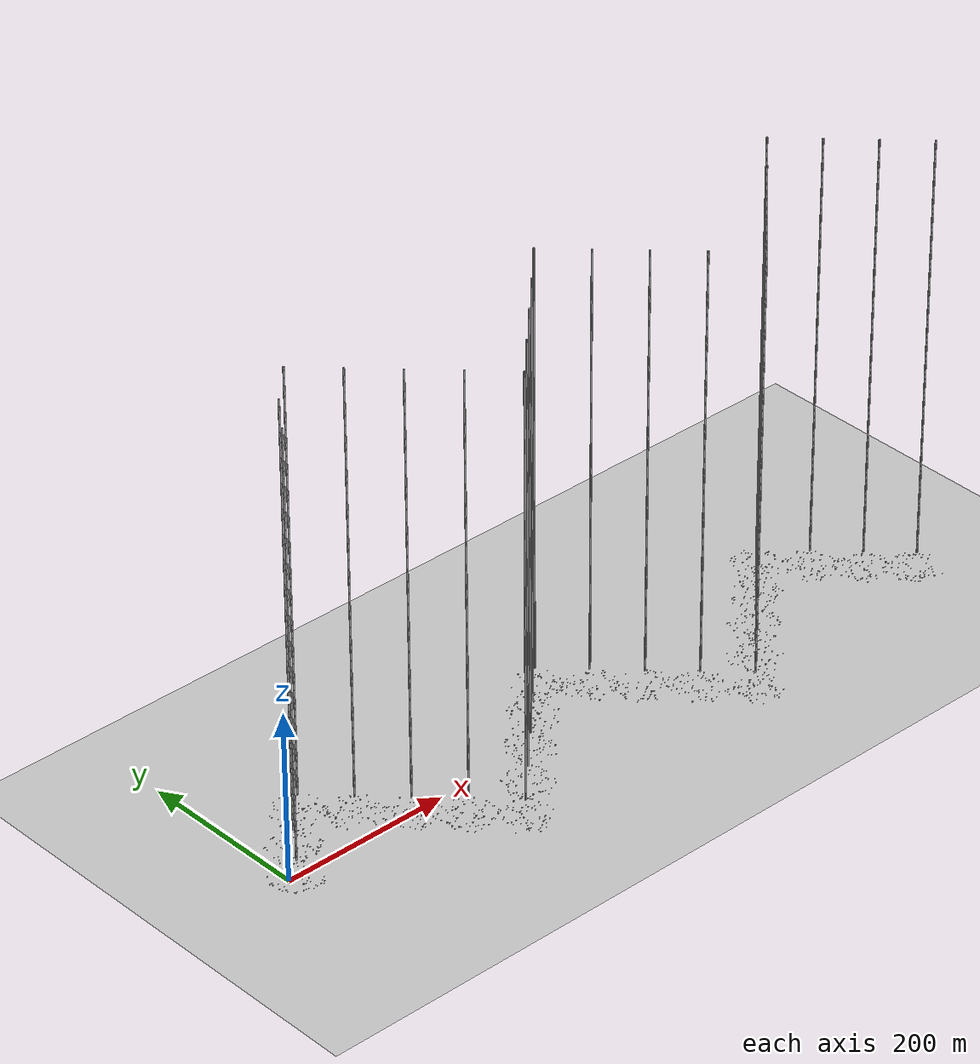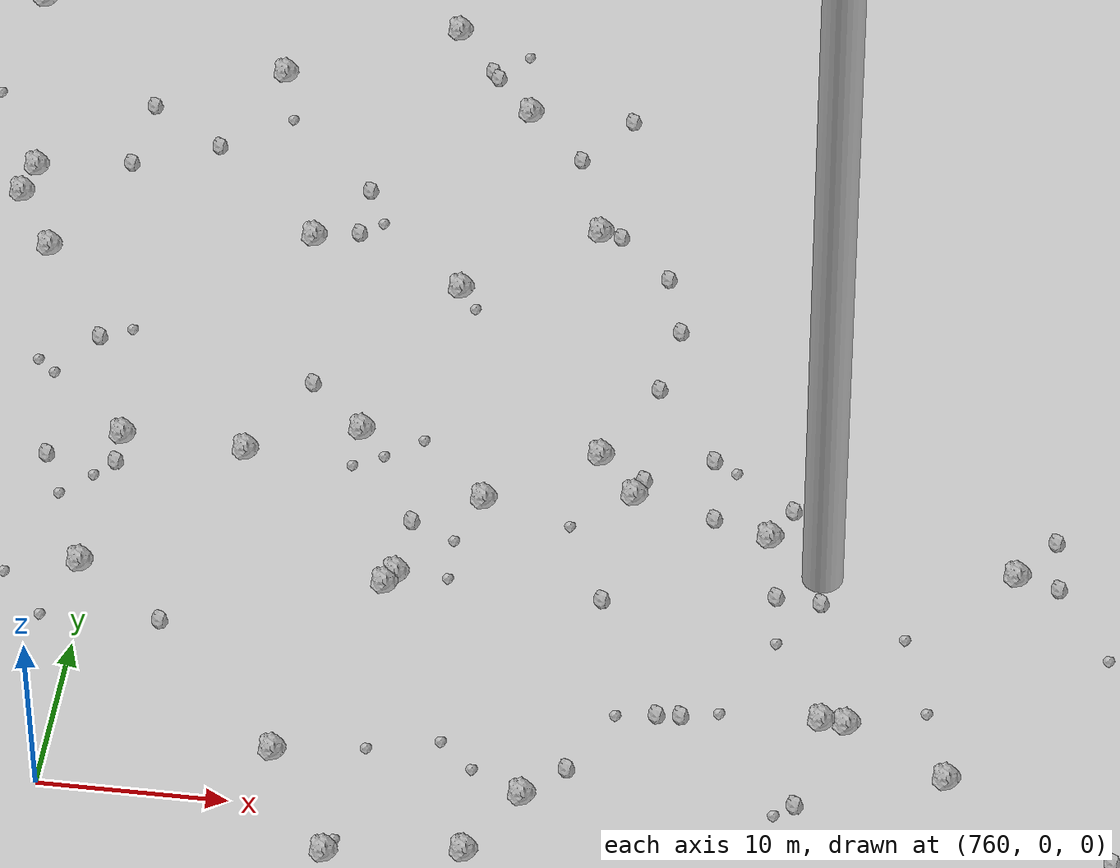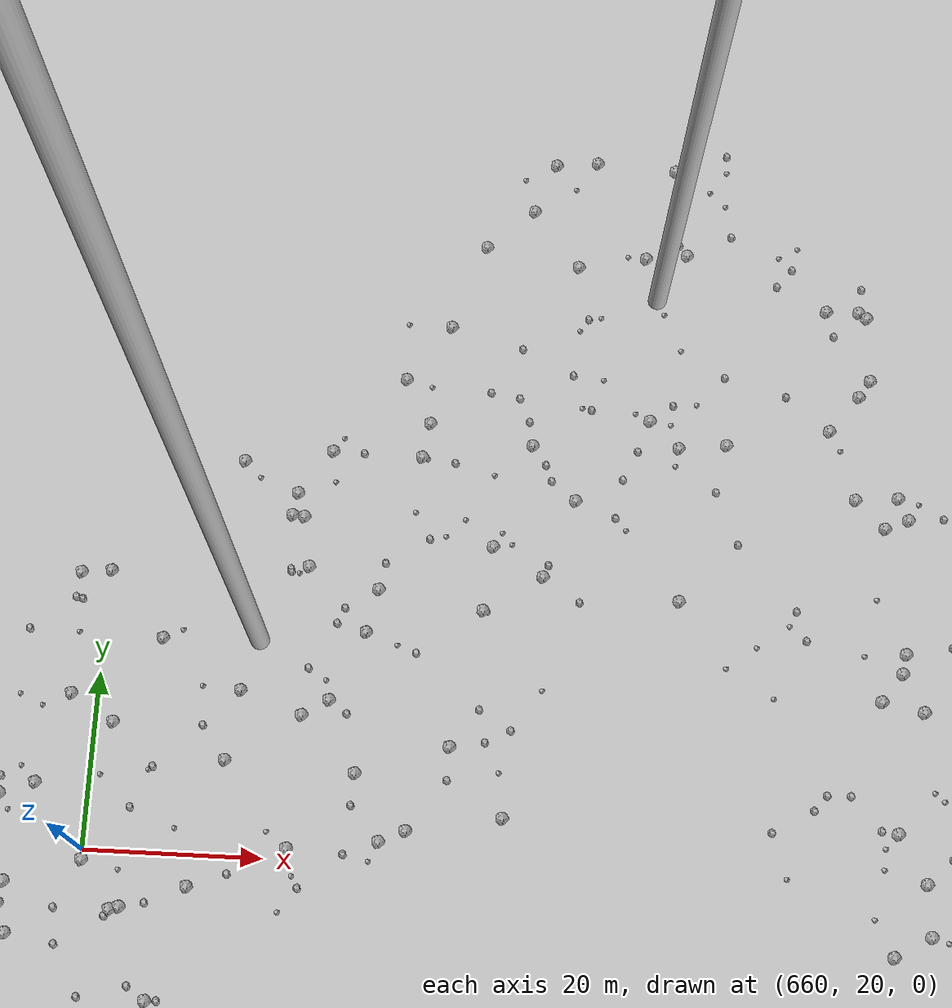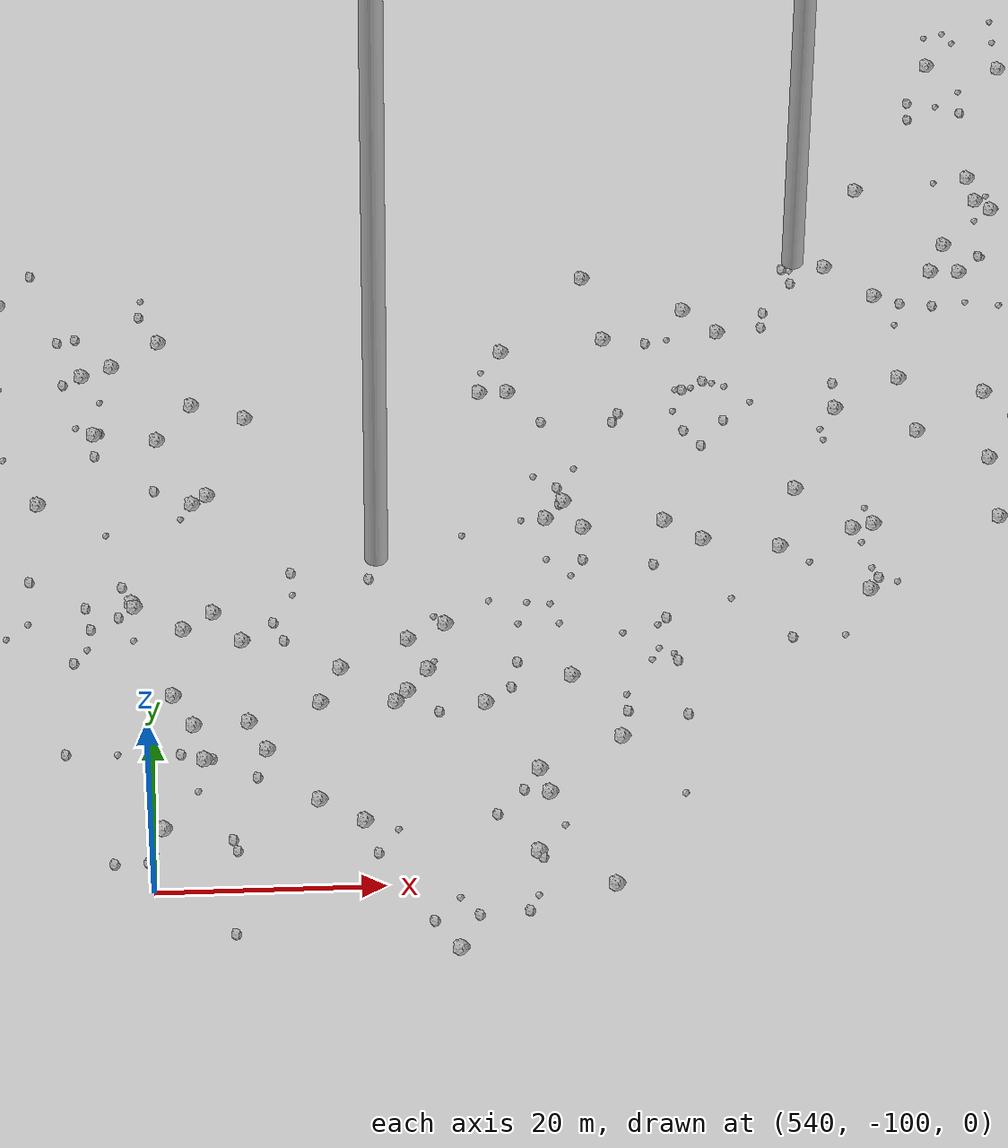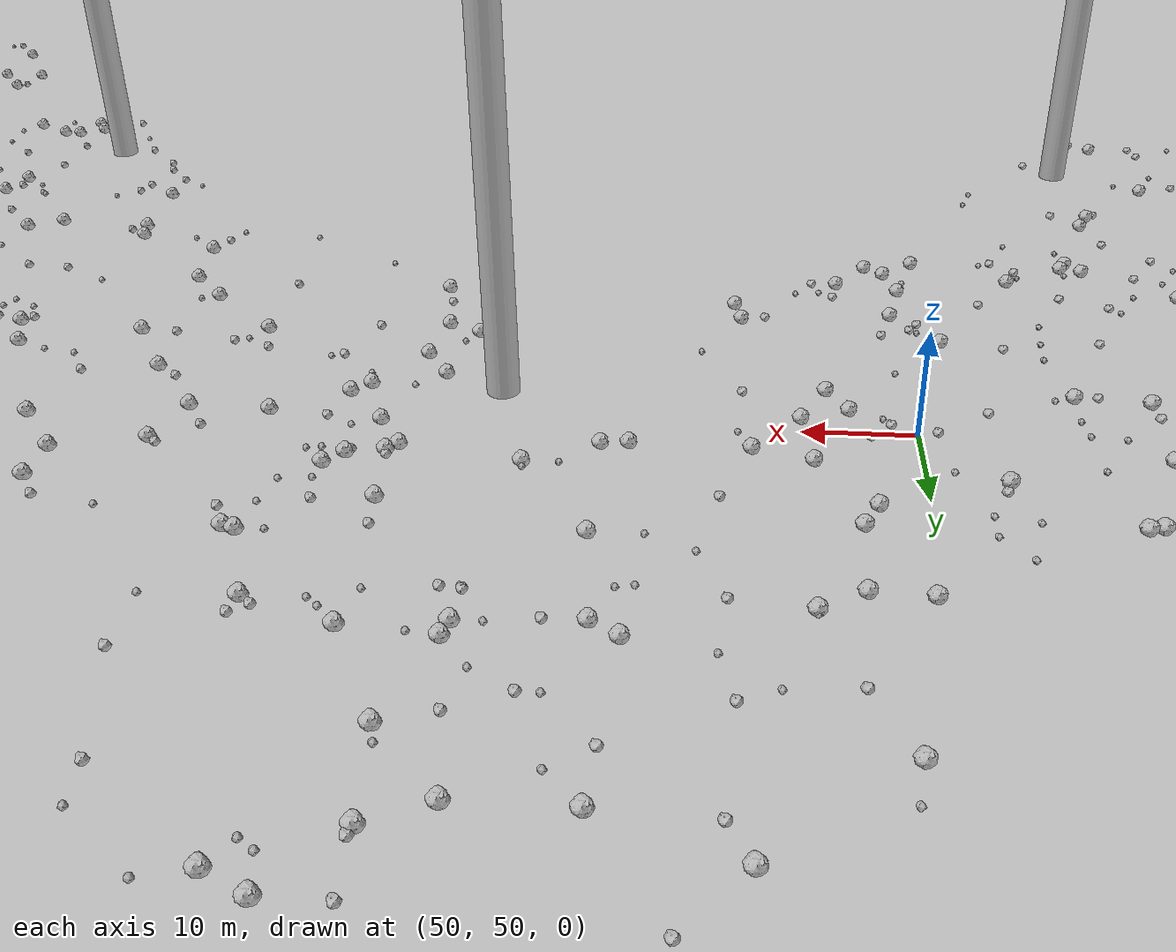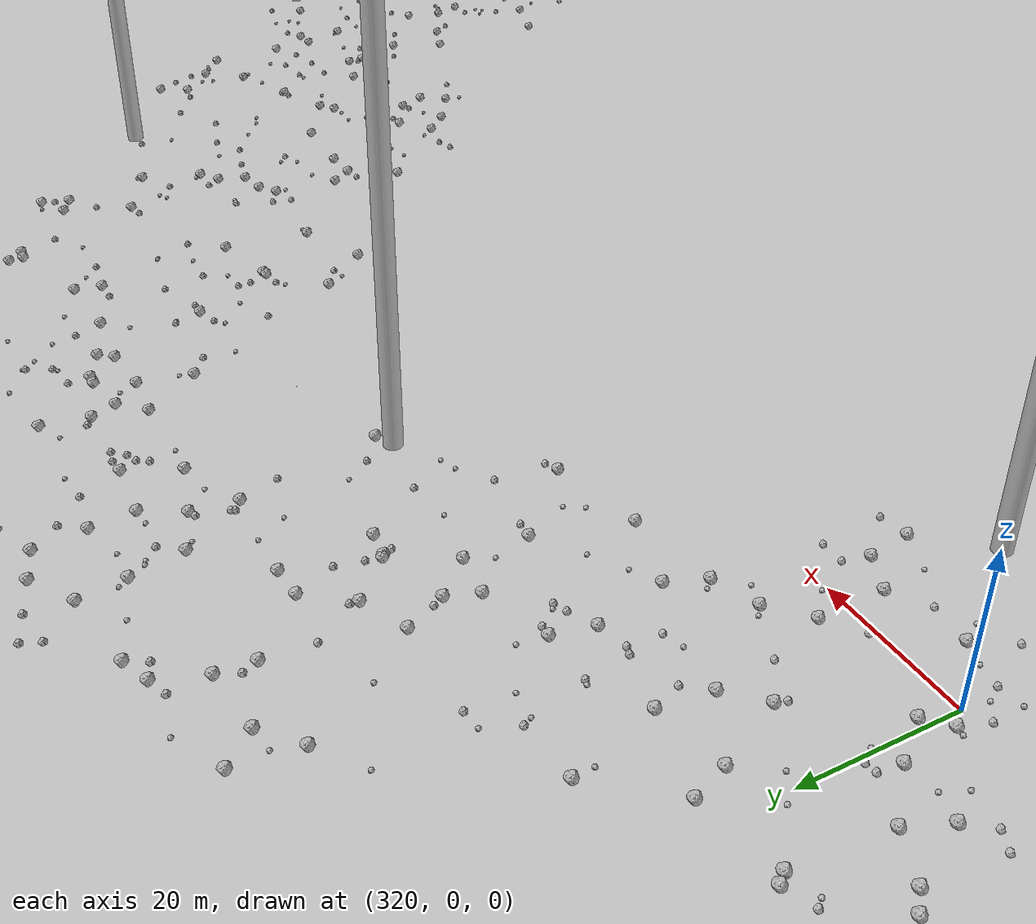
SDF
<sdf version="1.6">
 <world name="default">
  <include><uri>model://custom_ground</uri></include>
  <include><uri>model://sun</uri></include>
  <spherical_coordinates>
   <surface_model>EARTH_WGS84</surface_model>
   <latitude_deg>38.161479</latitude_deg>
   <longitude_deg>-122.454630</longitude_deg>
   <elevation>488.0</elevation>
   <heading_deg>90</heading_deg>
  </spherical_coordinates>
  <model name="rock1_0_0">
   <include><uri>model://rock1</uri><pose>-3.738427115198281 9.504144964753863 0.5 0 0 0</pose></include>
  </model>
  <model name="rock1_0_1">
   <include><uri>model://rock1</uri><pose>-3.936543423529187 23.03565781235109 0.5 0 0 0</pose></include>
  </model>
  <model name="rock1_0_2">
   <include><uri>model://rock1</uri><pose>-15.478508543491502 7.579801884550001 0.5 0 0 0</pose></include>
  </model>
  <model name="rock1_0_3">
   <include><uri>model://rock1</uri><pose>19.154230941098746 26.34770567985283 0.5 0 0 0</pose></include>
  </model>
  <model name="rock1_0_4">
   <include><uri>model://rock1</uri><pose>-16.26952670117127 -4.461578754564503 0.5 0 0 0</pose></include>
  </model>
  <model name="rock1_0_5">
   <include><uri>model://rock1</uri><pose>15.943776720668993 16.52844910317186 0.5 0 0 0</pose></include>
  </model>
  <model name="rock1_0_6">
   <include><uri>model://rock1</uri><pose>-8.70427945747763 -18.990837485125937 0.5 0 0 0</pose></include>
  </model>
  <model name="rock1_0_7">
   <include><uri>model://rock1</uri><pose>8.453705279977676 1.7365136836152466 0.5 0 0 0</pose></include>
  </model>
  <model name="rock1_0_8">
   <include><uri>model://rock1</uri><pose>8.423877939947715 3.445662174818551 0.5 0 0 0</pose></include>
  </model>
  <model name="rock1_0_9">
   <include><uri>model://rock1</uri><pose>-8.395035605716787 -19.852879169549713 0.5 0 0 0</pose></include>
  </model>
  <model name="rock1_0_10">
   <include><uri>model://rock1</uri><pose>-0.26383050366483474 9.12248176850354 0.5 0 0 0</pose></include>
  </model>
  <model name="rock1_0_11">
   <include><uri>model://rock1</uri><pose>11.188383665316525 -6.680695017462053 0.5 0 0 0</pose></include>
  </model>
  <model name="rock1_0_12">
   <include><uri>model://rock1</uri><pose>8.991772287947537 -3.6726403704004937 0.5 0 0 0</pose></include>
  </model>
  <model name="rock1_0_13">
   <include><uri>model://rock1</uri><pose>19.106031934486246 17.47323544988634 0.5 0 0 0</pose></include>
  </model>
  <model name="rock1_0_14">
   <include><uri>model://rock1</uri><pose>20.69733186675945 20.93994824646586 0.5 0 0 0</pose></include>
  </model>
  <model name="rock1_0_15">
   <include><uri>model://rock1</uri><pose>-4.298889402488381 13.167860747408412 0.5 0 0 0</pose></include>
  </model>
  <model name="rock1_0_16">
   <include><uri>model://rock1</uri><pose>-16.774803432463234 4.585380853515822 0.5 0 0 0</pose></include>
  </model>
  <model name="rock1_0_17">
   <include><uri>model://rock1</uri><pose>25.33484628785105 -1.1552003946533453 0.5 0 0 0</pose></include>
  </model>
  <model name="rock1_0_18">
   <include><uri>model://rock1</uri><pose>3.4173082205525454 27.640051545276556 0.5 0 0 0</pose></include>
  </model>
  <model name="rock1_0_19">
   <include><uri>model://rock1</uri><pose>17.05080156257562 -10.013613309631179 0.5 0 0 0</pose></include>
  </model>
  <model name="rock1_0_20">
   <include><uri>model://rock1</uri><pose>5.934472380701209 10.839916025522193 0.5 0 0 0</pose></include>
  </model>
  <model name="rock1_0_21">
   <include><uri>model://rock1</uri><pose>6.9422198867153675 -14.408914886011415 0.5 0 0 0</pose></include>
  </model>
  <model name="rock1_0_22">
   <include><uri>model://rock1</uri><pose>26.659840950833612 1.8602126845654325 0.5 0 0 0</pose></include>
  </model>
  <model name="rock1_0_23">
   <include><uri>model://rock1</uri><pose>31.318294984057935 14.276614448736048 0.5 0 0 0</pose></include>
  </model>
  <model name="rock1_0_24">
   <include><uri>model://rock1</uri><pose>-11.841794358269308 -10.021645544380753 0.5 0 0 0</pose></include>
  </model>
  <model name="rock1_0_25">
   <include><uri>model://rock1</uri><pose>19.959483772943564 -25.055293831240625 0.5 0 0 0</pose></include>
  </model>
  <model name="rock1_0_26">
   <include><uri>model://rock1</uri><pose>-12.231818277003585 18.525813914747914 0.5 0 0 0</pose></include>
  </model>
  <model name="rock2_0_0">
   <include><uri>model://rock2</uri><pose>20.92491891618694 11.282802481234668 0.3 0 0 0</pose></include>
  </model>
  <model name="rock2_0_1">
   <include><uri>model://rock2</uri><pose>25.061482016633242 -23.89148712092303 0.3 0 0 0</pose></include>
  </model>
  <model name="rock2_0_2">
   <include><uri>model://rock2</uri><pose>24.311373767298008 -1.9713641077246251 0.3 0 0 0</pose></include>
  </model>
  <model name="rock2_0_3">
   <include><uri>model://rock2</uri><pose>1.0258429732905405 -26.469851667786003 0.3 0 0 0</pose></include>
  </model>
  <model name="rock2_0_4">
   <include><uri>model://rock2</uri><pose>14.730889429571135 -25.69195907071518 0.3 0 0 0</pose></include>
  </model>
  <model name="rock2_0_5">
   <include><uri>model://rock2</uri><pose>0.5018184939248442 -21.23433660515229 0.3 0 0 0</pose></include>
  </model>
  <model name="rock2_0_6">
   <include><uri>model://rock2</uri><pose>-15.934206170171489 -8.25265943751399 0.3 0 0 0</pose></include>
  </model>
  <model name="rock2_0_7">
   <include><uri>model://rock2</uri><pose>15.39085384517523 14.573471519445242 0.3 0 0 0</pose></include>
  </model>
  <model name="rock2_0_8">
   <include><uri>model://rock2</uri><pose>-18.212239185288098 7.982660107052908 0.3 0 0 0</pose></include>
  </model>
  <model name="rock2_0_9">
   <include><uri>model://rock2</uri><pose>11.222011443232581 27.095661951867605 0.3 0 0 0</pose></include>
  </model>
  <model name="rock2_0_10">
   <include><uri>model://rock2</uri><pose>-12.601658654719687 -13.081827269869812 0.3 0 0 0</pose></include>
  </model>
  <model name="rock2_0_11">
   <include><uri>model://rock2</uri><pose>3.179991363624776 6.396461722603519 0.3 0 0 0</pose></include>
  </model>
  <model name="rock2_0_12">
   <include><uri>model://rock2</uri><pose>8.850873877106384 -15.082201100498697 0.3 0 0 0</pose></include>
  </model>
  <model name="rock2_0_13">
   <include><uri>model://rock2</uri><pose>12.784190924195833 -11.656417043862927 0.3 0 0 0</pose></include>
  </model>
  <model name="rock2_0_14">
   <include><uri>model://rock2</uri><pose>29.558208153964607 -18.48935346312357 0.3 0 0 0</pose></include>
  </model>
  <model name="rock2_0_15">
   <include><uri>model://rock2</uri><pose>14.20573084487718 -23.124026574218895 0.3 0 0 0</pose></include>
  </model>
  <model name="rock2_0_16">
   <include><uri>model://rock2</uri><pose>0.0940926043288961 -22.281797594003255 0.3 0 0 0</pose></include>
  </model>
  <model name="rock2_0_17">
   <include><uri>model://rock2</uri><pose>-10.134343892487207 -4.863221368710679 0.3 0 0 0</pose></include>
  </model>
  <model name="rock2_0_18">
   <include><uri>model://rock2</uri><pose>29.29203328929445 -1.3555420939547638 0.3 0 0 0</pose></include>
  </model>
  <model name="rock2_0_19">
   <include><uri>model://rock2</uri><pose>22.107937766724497 -26.9270547774089 0.3 0 0 0</pose></include>
  </model>
  <model name="rock2_0_20">
   <include><uri>model://rock2</uri><pose>12.73569804358069 -5.050384309038595 0.3 0 0 0</pose></include>
  </model>
  <model name="rock2_0_21">
   <include><uri>model://rock2</uri><pose>6.087087975668602 -13.993865742669378 0.3 0 0 0</pose></include>
  </model>
  <model name="rock2_0_22">
   <include><uri>model://rock2</uri><pose>17.050772315796877 24.80583489243852 0.3 0 0 0</pose></include>
  </model>
  <model name="rock2_0_23">
   <include><uri>model://rock2</uri><pose>23.898366094391918 16.200517595462685 0.3 0 0 0</pose></include>
  </model>
  <model name="rock2_0_24">
   <include><uri>model://rock2</uri><pose>25.23610911035528 7.061126469224341 0.3 0 0 0</pose></include>
  </model>
  <model name="rock2_0_25">
   <include><uri>model://rock2</uri><pose>4.699753296604499 18.14088267597719 0.3 0 0 0</pose></include>
  </model>
  <model name="rock2_0_26">
   <include><uri>model://rock2</uri><pose>2.5420269454578737 8.753312201231893 0.3 0 0 0</pose></include>
  </model>
  <model name="rock3_0_0">
   <include><uri>model://rock3</uri><pose>6.670441368557498 -20.90769256884716 0.2 0 0 0</pose></include>
  </model>
  <model name="rock3_0_1">
   <include><uri>model://rock3</uri><pose>13.306540348685779 22.6201140619005 0.2 0 0 0</pose></include>
  </model>
  <model name="rock3_0_2">
   <include><uri>model://rock3</uri><pose>-16.607045376999977 8.450816986583575 0.2 0 0 0</pose></include>
  </model>
  <model name="rock3_0_3">
   <include><uri>model://rock3</uri><pose>36.282648967112664 8.123211059709682 0.2 0 0 0</pose></include>
  </model>
  <model name="rock3_0_4">
   <include><uri>model://rock3</uri><pose>24.95470995009699 20.62578808241335 0.2 0 0 0</pose></include>
  </model>
  <model name="rock3_0_5">
   <include><uri>model://rock3</uri><pose>-11.64652162877794 2.820025509006882 0.2 0 0 0</pose></include>
  </model>
  <model name="rock3_0_6">
   <include><uri>model://rock3</uri><pose>17.081219032574722 27.97372518347629 0.2 0 0 0</pose></include>
  </model>
  <model name="rock3_0_7">
   <include><uri>model://rock3</uri><pose>31.00916167322766 15.621589499320343 0.2 0 0 0</pose></include>
  </model>
  <model name="rock3_0_8">
   <include><uri>model://rock3</uri><pose>30.894109500974814 9.644876372590232 0.2 0 0 0</pose></include>
  </model>
  <model name="rock3_0_9">
   <include><uri>model://rock3</uri><pose>3.9948996005910544 16.6854578328701 0.2 0 0 0</pose></include>
  </model>
  <model name="rock3_0_10">
   <include><uri>model://rock3</uri><pose>-7.261131065297466 -22.408306045063703 0.2 0 0 0</pose></include>
  </model>
  <model name="rock3_0_11">
   <include><uri>model://rock3</uri><pose>-7.10346245446649 -18.158869815832933 0.2 0 0 0</pose></include>
  </model>
  <model name="rock3_0_12">
   <include><uri>model://rock3</uri><pose>17.548822803060368 23.830913313014676 0.2 0 0 0</pose></include>
  </model>
  <model name="rock3_0_13">
   <include><uri>model://rock3</uri><pose>2.972528222009341 -21.83670902272752 0.2 0 0 0</pose></include>
  </model>
  <model name="rock3_0_14">
   <include><uri>model://rock3</uri><pose>5.747281964000063 -22.460189243064324 0.2 0 0 0</pose></include>
  </model>
  <model name="rock3_0_15">
   <include><uri>model://rock3</uri><pose>24.359244388568037 -21.24130685863622 0.2 0 0 0</pose></include>
  </model>
  <model name="rock3_0_16">
   <include><uri>model://rock3</uri><pose>10.088013220283244 -8.640214228986451 0.2 0 0 0</pose></include>
  </model>
  <model name="rock3_0_17">
   <include><uri>model://rock3</uri><pose>-0.25682240098749887 16.07962996841235 0.2 0 0 0</pose></include>
  </model>
  <model name="rock3_0_18">
   <include><uri>model://rock3</uri><pose>14.437330136763094 -15.379835294060538 0.2 0 0 0</pose></include>
  </model>
  <model name="rock3_0_19">
   <include><uri>model://rock3</uri><pose>37.87351729821124 -7.912242953738549 0.2 0 0 0</pose></include>
  </model>
  <model name="rock3_0_20">
   <include><uri>model://rock3</uri><pose>21.079079366685953 17.01427677435455 0.2 0 0 0</pose></include>
  </model>
  <model name="rock3_0_21">
   <include><uri>model://rock3</uri><pose>-18.502625562927783 4.9642559530479105 0.2 0 0 0</pose></include>
  </model>
  <model name="rock3_0_22">
   <include><uri>model://rock3</uri><pose>39.014358280244664 -4.42208471363649 0.2 0 0 0</pose></include>
  </model>
  <model name="rock3_0_23">
   <include><uri>model://rock3</uri><pose>19.05651495392437 13.476644433644502 0.2 0 0 0</pose></include>
  </model>
  <model name="rock3_0_24">
   <include><uri>model://rock3</uri><pose>9.40770644308937 -26.17883299211057 0.2 0 0 0</pose></include>
  </model>
  <model name="rock3_0_25">
   <include><uri>model://rock3</uri><pose>-5.876222882856727 -18.99569577547726 0.2 0 0 0</pose></include>
  </model>
  <model name="rock3_0_26">
   <include><uri>model://rock3</uri><pose>19.55209429841163 -12.083749824753504 0.2 0 0 0</pose></include>
  </model>
  <model name="rock1_1_0">
   <include><uri>model://rock1</uri><pose>50.456086491093856 17.087016188502805 0.5 0 0 0</pose></include>
  </model>
  <model name="rock1_1_1">
   <include><uri>model://rock1</uri><pose>17.315156142340797 56.137025474250144 0.5 0 0 0</pose></include>
  </model>
  <model name="rock1_1_2">
   <include><uri>model://rock1</uri><pose>49.305431207989294 21.274678136036307 0.5 0 0 0</pose></include>
  </model>
  <model name="rock1_1_3">
   <include><uri>model://rock1</uri><pose>64.29224222460198 53.39575427591759 0.5 0 0 0</pose></include>
  </model>
  <model name="rock1_1_4">
   <include><uri>model://rock1</uri><pose>46.19883747055141 32.665065058265796 0.5 0 0 0</pose></include>
  </model>
  <model name="rock1_1_5">
   <include><uri>model://rock1</uri><pose>50.54924929779316 27.15052493233 0.5 0 0 0</pose></include>
  </model>
  <model name="rock1_1_6">
   <include><uri>model://rock1</uri><pose>65.34099111195175 28.81769663367008 0.5 0 0 0</pose></include>
  </model>
  <model name="rock1_1_7">
   <include><uri>model://rock1</uri><pose>55.60386997988229 64.03062395945628 0.5 0 0 0</pose></include>
  </model>
  <model name="rock1_1_8">
   <include><uri>model://rock1</uri><pose>52.31457382676555 15.548840829578465 0.5 0 0 0</pose></include>
  </model>
  <model name="rock1_1_9">
   <include><uri>model://rock1</uri><pose>55.76653468274104 46.46933874249143 0.5 0 0 0</pose></include>
  </model>
  <model name="rock1_1_10">
   <include><uri>model://rock1</uri><pose>66.04373794340839 25.558658192196177 0.5 0 0 0</pose></include>
  </model>
  <model name="rock1_1_11">
   <include><uri>model://rock1</uri><pose>59.1273089432955 54.954282761037994 0.5 0 0 0</pose></include>
  </model>
  <model name="rock1_1_12">
   <include><uri>model://rock1</uri><pose>29.220560882581555 14.950777305704936 0.5 0 0 0</pose></include>
  </model>
  <model name="rock1_1_13">
   <include><uri>model://rock1</uri><pose>60.01181029388819 48.14098395748046 0.5 0 0 0</pose></include>
  </model>
  <model name="rock1_1_14">
   <include><uri>model://rock1</uri><pose>35.53775055094405 42.802067464437386 0.5 0 0 0</pose></include>
  </model>
  <model name="rock1_1_15">
   <include><uri>model://rock1</uri><pose>30.597466895469122 12.95164479144029 0.5 0 0 0</pose></include>
  </model>
  <model name="rock1_1_16">
   <include><uri>model://rock1</uri><pose>32.78240200203218 62.8397682331148 0.5 0 0 0</pose></include>
  </model>
  <model name="rock1_1_17">
   <include><uri>model://rock1</uri><pose>47.212660950515 14.12415277109696 0.5 0 0 0</pose></include>
  </model>
  <model name="rock1_1_18">
   <include><uri>model://rock1</uri><pose>55.53876023867074 19.99196033751492 0.5 0 0 0</pose></include>
  </model>
  <model name="rock1_1_19">
   <include><uri>model://rock1</uri><pose>29.42021794934631 53.0039110209793 0.5 0 0 0</pose></include>
  </model>
  <model name="rock1_1_20">
   <include><uri>model://rock1</uri><pose>43.447853307494206 57.12519296616732 0.5 0 0 0</pose></include>
  </model>
  <model name="rock1_1_21">
   <include><uri>model://rock1</uri><pose>57.66403713625259 43.050185719661755 0.5 0 0 0</pose></include>
  </model>
  <model name="rock1_1_22">
   <include><uri>model://rock1</uri><pose>37.596918263581614 18.1955572797891 0.5 0 0 0</pose></include>
  </model>
  <model name="rock1_1_23">
   <include><uri>model://rock1</uri><pose>29.815829414869015 62.805005553532574 0.5 0 0 0</pose></include>
  </model>
  <model name="rock1_1_24">
   <include><uri>model://rock1</uri><pose>34.00145584572038 63.0837806604085 0.5 0 0 0</pose></include>
  </model>
  <model name="rock1_1_25">
   <include><uri>model://rock1</uri><pose>54.278871209622835 61.21299863588528 0.5 0 0 0</pose></include>
  </model>
  <model name="rock1_1_26">
   <include><uri>model://rock1</uri><pose>28.85281088262934 43.32453098105989 0.5 0 0 0</pose></include>
  </model>
  <model name="rock2_1_0">
   <include><uri>model://rock2</uri><pose>24.509867704912264 52.18464504875109 0.3 0 0 0</pose></include>
  </model>
  <model name="rock2_1_1">
   <include><uri>model://rock2</uri><pose>58.017920859756174 19.86338835762023 0.3 0 0 0</pose></include>
  </model>
  <model name="rock2_1_2">
   <include><uri>model://rock2</uri><pose>48.84181295594112 30.03662646309136 0.3 0 0 0</pose></include>
  </model>
  <model name="rock2_1_3">
   <include><uri>model://rock2</uri><pose>40.290973676558856 33.538165839675116 0.3 0 0 0</pose></include>
  </model>
  <model name="rock2_1_4">
   <include><uri>model://rock2</uri><pose>36.29196307397725 15.313831533646294 0.3 0 0 0</pose></include>
  </model>
  <model name="rock2_1_5">
   <include><uri>model://rock2</uri><pose>28.134329355552797 23.662575520577704 0.3 0 0 0</pose></include>
  </model>
  <model name="rock2_1_6">
   <include><uri>model://rock2</uri><pose>65.11748250063994 43.67069118593573 0.3 0 0 0</pose></include>
  </model>
  <model name="rock2_1_7">
   <include><uri>model://rock2</uri><pose>13.139747359027538 37.69287559925834 0.3 0 0 0</pose></include>
  </model>
  <model name="rock2_1_8">
   <include><uri>model://rock2</uri><pose>30.84533771763855 31.830697389100674 0.3 0 0 0</pose></include>
  </model>
  <model name="rock2_1_9">
   <include><uri>model://rock2</uri><pose>33.31544944247852 42.53881457460408 0.3 0 0 0</pose></include>
  </model>
  <model name="rock2_1_10">
   <include><uri>model://rock2</uri><pose>62.954250609026424 28.24735490917984 0.3 0 0 0</pose></include>
  </model>
  <model name="rock2_1_11">
   <include><uri>model://rock2</uri><pose>32.75952075819949 21.795261167610583 0.3 0 0 0</pose></include>
  </model>
  <model name="rock2_1_12">
   <include><uri>model://rock2</uri><pose>38.55679897963036 13.254129442015527 0.3 0 0 0</pose></include>
  </model>
  <model name="rock2_1_13">
   <include><uri>model://rock2</uri><pose>21.84576407602713 41.58024481039415 0.3 0 0 0</pose></include>
  </model>
  <model name="rock2_1_14">
   <include><uri>model://rock2</uri><pose>13.715850259547526 30.805960349542175 0.3 0 0 0</pose></include>
  </model>
  <model name="rock2_1_15">
   <include><uri>model://rock2</uri><pose>16.597721355224753 35.547060257675795 0.3 0 0 0</pose></include>
  </model>
  <model name="rock2_1_16">
   <include><uri>model://rock2</uri><pose>56.00289834632734 22.994499737586715 0.3 0 0 0</pose></include>
  </model>
  <model name="rock2_1_17">
   <include><uri>model://rock2</uri><pose>48.303897822392955 49.642680599254085 0.3 0 0 0</pose></include>
  </model>
  <model name="rock2_1_18">
   <include><uri>model://rock2</uri><pose>43.52807479436079 46.03147209662153 0.3 0 0 0</pose></include>
  </model>
  <model name="rock2_1_19">
   <include><uri>model://rock2</uri><pose>48.01807547696339 28.779209979187122 0.3 0 0 0</pose></include>
  </model>
  <model name="rock2_1_20">
   <include><uri>model://rock2</uri><pose>51.68530495392764 31.404709692059406 0.3 0 0 0</pose></include>
  </model>
  <model name="rock2_1_21">
   <include><uri>model://rock2</uri><pose>15.212759865376066 55.966548976445836 0.3 0 0 0</pose></include>
  </model>
  <model name="rock2_1_22">
   <include><uri>model://rock2</uri><pose>52.209959047220956 48.60824951770427 0.3 0 0 0</pose></include>
  </model>
  <model name="rock2_1_23">
   <include><uri>model://rock2</uri><pose>43.84600231325755 58.53010834136511 0.3 0 0 0</pose></include>
  </model>
  <model name="rock2_1_24">
   <include><uri>model://rock2</uri><pose>54.104743224955904 50.66207130171833 0.3 0 0 0</pose></include>
  </model>
  <model name="rock2_1_25">
   <include><uri>model://rock2</uri><pose>41.2759548364955 23.80997175559862 0.3 0 0 0</pose></include>
  </model>
  <model name="rock2_1_26">
   <include><uri>model://rock2</uri><pose>28.60645121238776 45.80100330241829 0.3 0 0 0</pose></include>
  </model>
  <model name="rock3_1_0">
   <include><uri>model://rock3</uri><pose>35.599423420891746 46.69215709732834 0.2 0 0 0</pose></include>
  </model>
  <model name="rock3_1_1">
   <include><uri>model://rock3</uri><pose>35.178902343974485 54.710815979163904 0.2 0 0 0</pose></include>
  </model>
  <model name="rock3_1_2">
   <include><uri>model://rock3</uri><pose>32.29437026567379 49.54873734339765 0.2 0 0 0</pose></include>
  </model>
  <model name="rock3_1_3">
   <include><uri>model://rock3</uri><pose>47.620780154542466 55.700119572800965 0.2 0 0 0</pose></include>
  </model>
  <model name="rock3_1_4">
   <include><uri>model://rock3</uri><pose>36.14097677530421 16.6319574172443 0.2 0 0 0</pose></include>
  </model>
  <model name="rock3_1_5">
   <include><uri>model://rock3</uri><pose>48.494222762733955 18.80609143124691 0.2 0 0 0</pose></include>
  </model>
  <model name="rock3_1_6">
   <include><uri>model://rock3</uri><pose>36.711292621393284 35.27796289851347 0.2 0 0 0</pose></include>
  </model>
  <model name="rock3_1_7">
   <include><uri>model://rock3</uri><pose>35.90952554173795 28.247562190790397 0.2 0 0 0</pose></include>
  </model>
  <model name="rock3_1_8">
   <include><uri>model://rock3</uri><pose>41.87149343731105 62.564892439278864 0.2 0 0 0</pose></include>
  </model>
  <model name="rock3_1_9">
   <include><uri>model://rock3</uri><pose>20.181577297487827 27.793220487225323 0.2 0 0 0</pose></include>
  </model>
  <model name="rock3_1_10">
   <include><uri>model://rock3</uri><pose>59.716137667214724 22.21585384313656 0.2 0 0 0</pose></include>
  </model>
  <model name="rock3_1_11">
   <include><uri>model://rock3</uri><pose>50.9858662027591 39.03464331018484 0.2 0 0 0</pose></include>
  </model>
  <model name="rock3_1_12">
   <include><uri>model://rock3</uri><pose>27.060873042605355 24.45798588129827 0.2 0 0 0</pose></include>
  </model>
  <model name="rock3_1_13">
   <include><uri>model://rock3</uri><pose>57.29346672947688 21.814770774717363 0.2 0 0 0</pose></include>
  </model>
  <model name="rock3_1_14">
   <include><uri>model://rock3</uri><pose>37.15711282895465 43.13037286587629 0.2 0 0 0</pose></include>
  </model>
  <model name="rock3_1_15">
   <include><uri>model://rock3</uri><pose>15.852813855001912 52.060350619920776 0.2 0 0 0</pose></include>
  </model>
  <model name="rock3_1_16">
   <include><uri>model://rock3</uri><pose>35.29208778055354 49.183349641266275 0.2 0 0 0</pose></include>
  </model>
  <model name="rock3_1_17">
   <include><uri>model://rock3</uri><pose>65.40428760288583 50.5631927232936 0.2 0 0 0</pose></include>
  </model>
  <model name="rock3_1_18">
   <include><uri>model://rock3</uri><pose>20.32931932685169 43.19157010612833 0.2 0 0 0</pose></include>
  </model>
  <model name="rock3_1_19">
   <include><uri>model://rock3</uri><pose>43.16692322214725 67.46129644536413 0.2 0 0 0</pose></include>
  </model>
  <model name="rock3_1_20">
   <include><uri>model://rock3</uri><pose>48.11780943942513 30.441706389656723 0.2 0 0 0</pose></include>
  </model>
  <model name="rock3_1_21">
   <include><uri>model://rock3</uri><pose>45.387723382434224 61.906398581505265 0.2 0 0 0</pose></include>
  </model>
  <model name="rock3_1_22">
   <include><uri>model://rock3</uri><pose>52.78851140272231 47.47396417473924 0.2 0 0 0</pose></include>
  </model>
  <model name="rock3_1_23">
   <include><uri>model://rock3</uri><pose>68.98291629929524 35.89571598516978 0.2 0 0 0</pose></include>
  </model>
  <model name="rock3_1_24">
   <include><uri>model://rock3</uri><pose>39.732074689209405 13.55049336733305 0.2 0 0 0</pose></include>
  </model>
  <model name="rock3_1_25">
   <include><uri>model://rock3</uri><pose>36.44212062110418 32.06940260442798 0.2 0 0 0</pose></include>
  </model>
  <model name="rock3_1_26">
   <include><uri>model://rock3</uri><pose>45.45620027124493 64.63342962848256 0.2 0 0 0</pose></include>
  </model>
  <model name="rock1_2_0">
   <include><uri>model://rock1</uri><pose>55.9659528113321 72.36531472849072 0.5 0 0 0</pose></include>
  </model>
  <model name="rock1_2_1">
   <include><uri>model://rock1</uri><pose>77.05935593840145 53.52974984676648 0.5 0 0 0</pose></include>
  </model>
  <model name="rock1_2_2">
   <include><uri>model://rock1</uri><pose>103.80736233233725 68.05881494785325 0.5 0 0 0</pose></include>
  </model>
  <model name="rock1_2_3">
   <include><uri>model://rock1</uri><pose>100.75809895635706 76.04544141157484 0.5 0 0 0</pose></include>
  </model>
  <model name="rock1_2_4">
   <include><uri>model://rock1</uri><pose>64.01230145695264 97.7344643087857 0.5 0 0 0</pose></include>
  </model>
  <model name="rock1_2_5">
   <include><uri>model://rock1</uri><pose>73.25973274477522 78.62411572369521 0.5 0 0 0</pose></include>
  </model>
  <model name="rock1_2_6">
   <include><uri>model://rock1</uri><pose>99.76412359394823 58.160163155253706 0.5 0 0 0</pose></include>
  </model>
  <model name="rock1_2_7">
   <include><uri>model://rock1</uri><pose>85.56095252677412 79.42303463504923 0.5 0 0 0</pose></include>
  </model>
  <model name="rock1_2_8">
   <include><uri>model://rock1</uri><pose>93.08975675447516 78.75682341203898 0.5 0 0 0</pose></include>
  </model>
  <model name="rock1_2_9">
   <include><uri>model://rock1</uri><pose>59.62572676711962 74.67034977513725 0.5 0 0 0</pose></include>
  </model>
  <model name="rock1_2_10">
   <include><uri>model://rock1</uri><pose>51.09146579431971 72.63153674155434 0.5 0 0 0</pose></include>
  </model>
  <model name="rock1_2_11">
   <include><uri>model://rock1</uri><pose>88.16712578869422 88.12603090816683 0.5 0 0 0</pose></include>
  </model>
  <model name="rock1_2_12">
   <include><uri>model://rock1</uri><pose>87.1104129523099 96.41426743614994 0.5 0 0 0</pose></include>
  </model>
  <model name="rock1_2_13">
   <include><uri>model://rock1</uri><pose>74.66507464237884 53.28754666633803 0.5 0 0 0</pose></include>
  </model>
  <model name="rock1_2_14">
   <include><uri>model://rock1</uri><pose>74.08243794577096 94.21917463686682 0.5 0 0 0</pose></include>
  </model>
  <model name="rock1_2_15">
   <include><uri>model://rock1</uri><pose>53.71944340701106 88.79310625727507 0.5 0 0 0</pose></include>
  </model>
  <model name="rock1_2_16">
   <include><uri>model://rock1</uri><pose>94.86492798468112 100.15009846681897 0.5 0 0 0</pose></include>
  </model>
  <model name="rock1_2_17">
   <include><uri>model://rock1</uri><pose>94.04886896603112 54.85824991298455 0.5 0 0 0</pose></include>
  </model>
  <model name="rock1_2_18">
   <include><uri>model://rock1</uri><pose>82.59622054870646 94.23935317975406 0.5 0 0 0</pose></include>
  </model>
  <model name="rock1_2_19">
   <include><uri>model://rock1</uri><pose>91.48382503599396 101.83701712123842 0.5 0 0 0</pose></include>
  </model>
  <model name="rock1_2_20">
   <include><uri>model://rock1</uri><pose>83.31005286919509 56.797892656913575 0.5 0 0 0</pose></include>
  </model>
  <model name="rock1_2_21">
   <include><uri>model://rock1</uri><pose>94.96335937725038 55.84271319641114 0.5 0 0 0</pose></include>
  </model>
  <model name="rock1_2_22">
   <include><uri>model://rock1</uri><pose>104.90344990671623 67.7209845749725 0.5 0 0 0</pose></include>
  </model>
  <model name="rock1_2_23">
   <include><uri>model://rock1</uri><pose>94.14387655341332 62.93730242119578 0.5 0 0 0</pose></include>
  </model>
  <model name="rock1_2_24">
   <include><uri>model://rock1</uri><pose>85.18824096270693 77.76710656970081 0.5 0 0 0</pose></include>
  </model>
  <model name="rock1_2_25">
   <include><uri>model://rock1</uri><pose>75.61401373237064 77.05228950430963 0.5 0 0 0</pose></include>
  </model>
  <model name="rock1_2_26">
   <include><uri>model://rock1</uri><pose>76.8300503151317 66.52331774377136 0.5 0 0 0</pose></include>
  </model>
  <model name="rock2_2_0">
   <include><uri>model://rock2</uri><pose>87.46379232222515 106.91979212051535 0.3 0 0 0</pose></include>
  </model>
  <model name="rock2_2_1">
   <include><uri>model://rock2</uri><pose>65.9563966346893 73.82860235967505 0.3 0 0 0</pose></include>
  </model>
  <model name="rock2_2_2">
   <include><uri>model://rock2</uri><pose>73.76944698887826 89.04415278754361 0.3 0 0 0</pose></include>
  </model>
  <model name="rock2_2_3">
   <include><uri>model://rock2</uri><pose>79.5534857508426 84.51285789718123 0.3 0 0 0</pose></include>
  </model>
  <model name="rock2_2_4">
   <include><uri>model://rock2</uri><pose>84.99736411095674 74.10779380181214 0.3 0 0 0</pose></include>
  </model>
  <model name="rock2_2_5">
   <include><uri>model://rock2</uri><pose>78.85722328438335 77.00565786925677 0.3 0 0 0</pose></include>
  </model>
  <model name="rock2_2_6">
   <include><uri>model://rock2</uri><pose>85.01707314719701 74.01776301292514 0.3 0 0 0</pose></include>
  </model>
  <model name="rock2_2_7">
   <include><uri>model://rock2</uri><pose>65.75080248195822 94.45024637957476 0.3 0 0 0</pose></include>
  </model>
  <model name="rock2_2_8">
   <include><uri>model://rock2</uri><pose>99.17181379680027 63.46187786740614 0.3 0 0 0</pose></include>
  </model>
  <model name="rock2_2_9">
   <include><uri>model://rock2</uri><pose>107.91662304364716 82.13006158625028 0.3 0 0 0</pose></include>
  </model>
  <model name="rock2_2_10">
   <include><uri>model://rock2</uri><pose>68.38353928045629 102.75894964326133 0.3 0 0 0</pose></include>
  </model>
  <model name="rock2_2_11">
   <include><uri>model://rock2</uri><pose>97.85673932395457 55.95826087940433 0.3 0 0 0</pose></include>
  </model>
  <model name="rock2_2_12">
   <include><uri>model://rock2</uri><pose>104.87933691859072 92.53408887503093 0.3 0 0 0</pose></include>
  </model>
  <model name="rock2_2_13">
   <include><uri>model://rock2</uri><pose>86.70904236494806 73.8965857845244 0.3 0 0 0</pose></include>
  </model>
  <model name="rock2_2_14">
   <include><uri>model://rock2</uri><pose>66.79030044968894 60.83929170422358 0.3 0 0 0</pose></include>
  </model>
  <model name="rock2_2_15">
   <include><uri>model://rock2</uri><pose>56.713002516834464 82.5597590294783 0.3 0 0 0</pose></include>
  </model>
  <model name="rock2_2_16">
   <include><uri>model://rock2</uri><pose>99.61377608699931 76.93687404300066 0.3 0 0 0</pose></include>
  </model>
  <model name="rock2_2_17">
   <include><uri>model://rock2</uri><pose>100.96823550104054 77.93828247797934 0.3 0 0 0</pose></include>
  </model>
  <model name="rock2_2_18">
   <include><uri>model://rock2</uri><pose>93.69621736551528 66.59143696697225 0.3 0 0 0</pose></include>
  </model>
  <model name="rock2_2_19">
   <include><uri>model://rock2</uri><pose>84.01202751580178 86.65538256929725 0.3 0 0 0</pose></include>
  </model>
  <model name="rock2_2_20">
   <include><uri>model://rock2</uri><pose>86.7462908965744 101.75713767931735 0.3 0 0 0</pose></include>
  </model>
  <model name="rock2_2_21">
   <include><uri>model://rock2</uri><pose>94.77463723257179 56.48608928238346 0.3 0 0 0</pose></include>
  </model>
  <model name="rock2_2_22">
   <include><uri>model://rock2</uri><pose>87.2800964230643 97.16832852303308 0.3 0 0 0</pose></include>
  </model>
  <model name="rock2_2_23">
   <include><uri>model://rock2</uri><pose>70.8726578049329 107.58860715074911 0.3 0 0 0</pose></include>
  </model>
  <model name="rock2_2_24">
   <include><uri>model://rock2</uri><pose>65.19882411920818 84.40907713760879 0.3 0 0 0</pose></include>
  </model>
  <model name="rock2_2_25">
   <include><uri>model://rock2</uri><pose>79.9258740202057 108.9140707903317 0.3 0 0 0</pose></include>
  </model>
  <model name="rock2_2_26">
   <include><uri>model://rock2</uri><pose>68.08384554000426 107.39511007142252 0.3 0 0 0</pose></include>
  </model>
  <model name="rock3_2_0">
   <include><uri>model://rock3</uri><pose>82.82982496153181 77.50411385896044 0.2 0 0 0</pose></include>
  </model>
  <model name="rock3_2_1">
   <include><uri>model://rock3</uri><pose>92.22097953411591 74.48677180624628 0.2 0 0 0</pose></include>
  </model>
  <model name="rock3_2_2">
   <include><uri>model://rock3</uri><pose>104.42065150453652 96.11894864170634 0.2 0 0 0</pose></include>
  </model>
  <model name="rock3_2_3">
   <include><uri>model://rock3</uri><pose>101.49880063458424 67.76148243193968 0.2 0 0 0</pose></include>
  </model>
  <model name="rock3_2_4">
   <include><uri>model://rock3</uri><pose>72.61530085333868 72.64129708159582 0.2 0 0 0</pose></include>
  </model>
  <model name="rock3_2_5">
   <include><uri>model://rock3</uri><pose>66.44766790773573 79.68720924018332 0.2 0 0 0</pose></include>
  </model>
  <model name="rock3_2_6">
   <include><uri>model://rock3</uri><pose>80.15646880480281 56.52203408996424 0.2 0 0 0</pose></include>
  </model>
  <model name="rock3_2_7">
   <include><uri>model://rock3</uri><pose>98.45438456677795 100.93909441994168 0.2 0 0 0</pose></include>
  </model>
  <model name="rock3_2_8">
   <include><uri>model://rock3</uri><pose>84.0809442577738 109.1521058841821 0.2 0 0 0</pose></include>
  </model>
  <model name="rock3_2_9">
   <include><uri>model://rock3</uri><pose>94.82396273576427 76.68438646174587 0.2 0 0 0</pose></include>
  </model>
  <model name="rock3_2_10">
   <include><uri>model://rock3</uri><pose>87.99513672644228 78.91781306337768 0.2 0 0 0</pose></include>
  </model>
  <model name="rock3_2_11">
   <include><uri>model://rock3</uri><pose>95.86947605846936 75.74839680257158 0.2 0 0 0</pose></include>
  </model>
  <model name="rock3_2_12">
   <include><uri>model://rock3</uri><pose>76.83587182327062 91.15516699944394 0.2 0 0 0</pose></include>
  </model>
  <model name="rock3_2_13">
   <include><uri>model://rock3</uri><pose>87.59799259450813 89.67579362693229 0.2 0 0 0</pose></include>
  </model>
  <model name="rock3_2_14">
   <include><uri>model://rock3</uri><pose>77.84789928162411 84.40512781210643 0.2 0 0 0</pose></include>
  </model>
  <model name="rock3_2_15">
   <include><uri>model://rock3</uri><pose>83.99833698086667 106.46464752035001 0.2 0 0 0</pose></include>
  </model>
  <model name="rock3_2_16">
   <include><uri>model://rock3</uri><pose>72.3639420522942 66.21436296867685 0.2 0 0 0</pose></include>
  </model>
  <model name="rock3_2_17">
   <include><uri>model://rock3</uri><pose>93.43711183369211 97.70414604046408 0.2 0 0 0</pose></include>
  </model>
  <model name="rock3_2_18">
   <include><uri>model://rock3</uri><pose>92.19313001316078 98.55406807788684 0.2 0 0 0</pose></include>
  </model>
  <model name="rock3_2_19">
   <include><uri>model://rock3</uri><pose>108.14998297790751 76.11251921705056 0.2 0 0 0</pose></include>
  </model>
  <model name="rock3_2_20">
   <include><uri>model://rock3</uri><pose>74.04003070320631 72.93543787929897 0.2 0 0 0</pose></include>
  </model>
  <model name="rock3_2_21">
   <include><uri>model://rock3</uri><pose>62.19675491432373 82.99291015681004 0.2 0 0 0</pose></include>
  </model>
  <model name="rock3_2_22">
   <include><uri>model://rock3</uri><pose>59.52121441475139 74.96599542780869 0.2 0 0 0</pose></include>
  </model>
  <model name="rock3_2_23">
   <include><uri>model://rock3</uri><pose>68.35212703523437 68.1825568898488 0.2 0 0 0</pose></include>
  </model>
  <model name="rock3_2_24">
   <include><uri>model://rock3</uri><pose>83.06113189559342 82.33353464892915 0.2 0 0 0</pose></include>
  </model>
  <model name="rock3_2_25">
   <include><uri>model://rock3</uri><pose>54.28772993585015 92.41239882774774 0.2 0 0 0</pose></include>
  </model>
  <model name="rock3_2_26">
   <include><uri>model://rock3</uri><pose>83.13868108204888 57.41479775712735 0.2 0 0 0</pose></include>
  </model>
  <model name="rock1_3_0">
   <include><uri>model://rock1</uri><pose>114.15856913869334 49.68433336939695 0.5 0 0 0</pose></include>
  </model>
  <model name="rock1_3_1">
   <include><uri>model://rock1</uri><pose>124.16949547975733 35.53543601389895 0.5 0 0 0</pose></include>
  </model>
  <model name="rock1_3_2">
   <include><uri>model://rock1</uri><pose>100.45209916351618 46.17752643138022 0.5 0 0 0</pose></include>
  </model>
  <model name="rock1_3_3">
   <include><uri>model://rock1</uri><pose>147.1298833237386 52.493824203245644 0.5 0 0 0</pose></include>
  </model>
  <model name="rock1_3_4">
   <include><uri>model://rock1</uri><pose>123.55169843362054 57.36039982242525 0.5 0 0 0</pose></include>
  </model>
  <model name="rock1_3_5">
   <include><uri>model://rock1</uri><pose>123.57098250970196 61.808967330884215 0.5 0 0 0</pose></include>
  </model>
  <model name="rock1_3_6">
   <include><uri>model://rock1</uri><pose>137.57390087587027 51.70543901366188 0.5 0 0 0</pose></include>
  </model>
  <model name="rock1_3_7">
   <include><uri>model://rock1</uri><pose>92.44394268077725 42.2690274751466 0.5 0 0 0</pose></include>
  </model>
  <model name="rock1_3_8">
   <include><uri>model://rock1</uri><pose>98.89708221539323 44.62004849139006 0.5 0 0 0</pose></include>
  </model>
  <model name="rock1_3_9">
   <include><uri>model://rock1</uri><pose>119.16854819812416 27.410076678201015 0.5 0 0 0</pose></include>
  </model>
  <model name="rock1_3_10">
   <include><uri>model://rock1</uri><pose>124.04797024198268 15.535463695915022 0.5 0 0 0</pose></include>
  </model>
  <model name="rock1_3_11">
   <include><uri>model://rock1</uri><pose>90.84561012833356 33.70191387333901 0.5 0 0 0</pose></include>
  </model>
  <model name="rock1_3_12">
   <include><uri>model://rock1</uri><pose>137.0067850700808 34.45359299169704 0.5 0 0 0</pose></include>
  </model>
  <model name="rock1_3_13">
   <include><uri>model://rock1</uri><pose>94.88159399160612 38.46022726126424 0.5 0 0 0</pose></include>
  </model>
  <model name="rock1_3_14">
   <include><uri>model://rock1</uri><pose>94.10817741582204 32.04933047680566 0.5 0 0 0</pose></include>
  </model>
  <model name="rock1_3_15">
   <include><uri>model://rock1</uri><pose>98.25253240731902 56.50107979042958 0.5 0 0 0</pose></include>
  </model>
  <model name="rock1_3_16">
   <include><uri>model://rock1</uri><pose>135.1424336127503 38.81556997109967 0.5 0 0 0</pose></include>
  </model>
  <model name="rock1_3_17">
   <include><uri>model://rock1</uri><pose>119.66976781548819 42.73746495378387 0.5 0 0 0</pose></include>
  </model>
  <model name="rock1_3_18">
   <include><uri>model://rock1</uri><pose>115.62482600608587 55.39618517027436 0.5 0 0 0</pose></include>
  </model>
  <model name="rock1_3_19">
   <include><uri>model://rock1</uri><pose>96.52118259531711 50.91086360718651 0.5 0 0 0</pose></include>
  </model>
  <model name="rock1_3_20">
   <include><uri>model://rock1</uri><pose>122.93996445499127 23.13283677468548 0.5 0 0 0</pose></include>
  </model>
  <model name="rock1_3_21">
   <include><uri>model://rock1</uri><pose>124.5709710054544 68.70617307660567 0.5 0 0 0</pose></include>
  </model>
  <model name="rock1_3_22">
   <include><uri>model://rock1</uri><pose>106.79330099764877 49.9304212356872 0.5 0 0 0</pose></include>
  </model>
  <model name="rock1_3_23">
   <include><uri>model://rock1</uri><pose>127.98484116331016 51.910027034886916 0.5 0 0 0</pose></include>
  </model>
  <model name="rock1_3_24">
   <include><uri>model://rock1</uri><pose>133.66800533652636 61.73915044909448 0.5 0 0 0</pose></include>
  </model>
  <model name="rock1_3_25">
   <include><uri>model://rock1</uri><pose>95.74324723223188 23.713404640626848 0.5 0 0 0</pose></include>
  </model>
  <model name="rock1_3_26">
   <include><uri>model://rock1</uri><pose>111.79002503315792 34.28613344197679 0.5 0 0 0</pose></include>
  </model>
  <model name="rock2_3_0">
   <include><uri>model://rock2</uri><pose>94.78566582816212 27.001740614685087 0.3 0 0 0</pose></include>
  </model>
  <model name="rock2_3_1">
   <include><uri>model://rock2</uri><pose>144.9799358737132 26.61533489289909 0.3 0 0 0</pose></include>
  </model>
  <model name="rock2_3_2">
   <include><uri>model://rock2</uri><pose>102.8821986130019 39.14116905229301 0.3 0 0 0</pose></include>
  </model>
  <model name="rock2_3_3">
   <include><uri>model://rock2</uri><pose>111.7908876711942 24.012744915473167 0.3 0 0 0</pose></include>
  </model>
  <model name="rock2_3_4">
   <include><uri>model://rock2</uri><pose>117.3577368841272 44.47426108075536 0.3 0 0 0</pose></include>
  </model>
  <model name="rock2_3_5">
   <include><uri>model://rock2</uri><pose>133.26055417831054 53.9027161910035 0.3 0 0 0</pose></include>
  </model>
  <model name="rock2_3_6">
   <include><uri>model://rock2</uri><pose>114.76430079809019 56.02912351313541 0.3 0 0 0</pose></include>
  </model>
  <model name="rock2_3_7">
   <include><uri>model://rock2</uri><pose>114.2814470094314 37.071220716881825 0.3 0 0 0</pose></include>
  </model>
  <model name="rock2_3_8">
   <include><uri>model://rock2</uri><pose>138.0349836536515 21.53464806231085 0.3 0 0 0</pose></include>
  </model>
  <model name="rock2_3_9">
   <include><uri>model://rock2</uri><pose>133.60846826855027 63.78388406333699 0.3 0 0 0</pose></include>
  </model>
  <model name="rock2_3_10">
   <include><uri>model://rock2</uri><pose>142.57840566752373 21.124186428361668 0.3 0 0 0</pose></include>
  </model>
  <model name="rock2_3_11">
   <include><uri>model://rock2</uri><pose>111.93509216387432 52.927007520604 0.3 0 0 0</pose></include>
  </model>
  <model name="rock2_3_12">
   <include><uri>model://rock2</uri><pose>139.80205257655413 33.459212731790664 0.3 0 0 0</pose></include>
  </model>
  <model name="rock2_3_13">
   <include><uri>model://rock2</uri><pose>136.58384435860344 57.16102487421703 0.3 0 0 0</pose></include>
  </model>
  <model name="rock2_3_14">
   <include><uri>model://rock2</uri><pose>134.60792185644956 63.78716244318898 0.3 0 0 0</pose></include>
  </model>
  <model name="rock2_3_15">
   <include><uri>model://rock2</uri><pose>121.60087823929253 64.50492507503162 0.3 0 0 0</pose></include>
  </model>
  <model name="rock2_3_16">
   <include><uri>model://rock2</uri><pose>110.60060158879149 38.19264240651408 0.3 0 0 0</pose></include>
  </model>
  <model name="rock2_3_17">
   <include><uri>model://rock2</uri><pose>100.82127484288031 32.90569448824484 0.3 0 0 0</pose></include>
  </model>
  <model name="rock2_3_18">
   <include><uri>model://rock2</uri><pose>126.60773704710256 43.95827549540467 0.3 0 0 0</pose></include>
  </model>
  <model name="rock2_3_19">
   <include><uri>model://rock2</uri><pose>141.15866603792932 43.44498090945595 0.3 0 0 0</pose></include>
  </model>
  <model name="rock2_3_20">
   <include><uri>model://rock2</uri><pose>120.58682998508982 35.65906558915452 0.3 0 0 0</pose></include>
  </model>
  <model name="rock2_3_21">
   <include><uri>model://rock2</uri><pose>101.3916661039662 50.505975938440834 0.3 0 0 0</pose></include>
  </model>
  <model name="rock2_3_22">
   <include><uri>model://rock2</uri><pose>140.25633187434008 38.05224904667371 0.3 0 0 0</pose></include>
  </model>
  <model name="rock2_3_23">
   <include><uri>model://rock2</uri><pose>138.00683003132917 63.7044729279779 0.3 0 0 0</pose></include>
  </model>
  <model name="rock2_3_24">
   <include><uri>model://rock2</uri><pose>106.19462877782617 65.07015833553741 0.3 0 0 0</pose></include>
  </model>
  <model name="rock2_3_25">
   <include><uri>model://rock2</uri><pose>136.03568961301573 33.56476133764923 0.3 0 0 0</pose></include>
  </model>
  <model name="rock2_3_26">
   <include><uri>model://rock2</uri><pose>122.9315846391008 13.009948339793961 0.3 0 0 0</pose></include>
  </model>
  <model name="rock3_3_0">
   <include><uri>model://rock3</uri><pose>131.94236456011075 39.98763182631461 0.2 0 0 0</pose></include>
  </model>
  <model name="rock3_3_1">
   <include><uri>model://rock3</uri><pose>128.7747448573688 40.577332607788414 0.2 0 0 0</pose></include>
  </model>
  <model name="rock3_3_2">
   <include><uri>model://rock3</uri><pose>113.00151031480293 36.4162494882468 0.2 0 0 0</pose></include>
  </model>
  <model name="rock3_3_3">
   <include><uri>model://rock3</uri><pose>104.05121271248892 39.38438389175773 0.2 0 0 0</pose></include>
  </model>
  <model name="rock3_3_4">
   <include><uri>model://rock3</uri><pose>103.3202715583705 64.06623288264632 0.2 0 0 0</pose></include>
  </model>
  <model name="rock3_3_5">
   <include><uri>model://rock3</uri><pose>140.51963438937344 31.006475193660826 0.2 0 0 0</pose></include>
  </model>
  <model name="rock3_3_6">
   <include><uri>model://rock3</uri><pose>98.89090931950545 51.78505368651222 0.2 0 0 0</pose></include>
  </model>
  <model name="rock3_3_7">
   <include><uri>model://rock3</uri><pose>100.43195716881569 55.586638278585774 0.2 0 0 0</pose></include>
  </model>
  <model name="rock3_3_8">
   <include><uri>model://rock3</uri><pose>133.09257245342954 24.205577140541266 0.2 0 0 0</pose></include>
  </model>
  <model name="rock3_3_9">
   <include><uri>model://rock3</uri><pose>139.49438666255955 57.455193451024975 0.2 0 0 0</pose></include>
  </model>
  <model name="rock3_3_10">
   <include><uri>model://rock3</uri><pose>102.66904104265326 60.6864657477051 0.2 0 0 0</pose></include>
  </model>
  <model name="rock3_3_11">
   <include><uri>model://rock3</uri><pose>137.307834683093 31.027750910141776 0.2 0 0 0</pose></include>
  </model>
  <model name="rock3_3_12">
   <include><uri>model://rock3</uri><pose>99.89972851779726 60.31163646595861 0.2 0 0 0</pose></include>
  </model>
  <model name="rock3_3_13">
   <include><uri>model://rock3</uri><pose>144.51161295684423 37.201172030069124 0.2 0 0 0</pose></include>
  </model>
  <model name="rock3_3_14">
   <include><uri>model://rock3</uri><pose>94.8625719089158 44.38548611264748 0.2 0 0 0</pose></include>
  </model>
  <model name="rock3_3_15">
   <include><uri>model://rock3</uri><pose>122.00221558811899 10.381677571850418 0.2 0 0 0</pose></include>
  </model>
  <model name="rock3_3_16">
   <include><uri>model://rock3</uri><pose>120.86054942258214 27.849058147347378 0.2 0 0 0</pose></include>
  </model>
  <model name="rock3_3_17">
   <include><uri>model://rock3</uri><pose>103.00468541863837 17.602582100218108 0.2 0 0 0</pose></include>
  </model>
  <model name="rock3_3_18">
   <include><uri>model://rock3</uri><pose>139.84253526012498 29.59079018327921 0.2 0 0 0</pose></include>
  </model>
  <model name="rock3_3_19">
   <include><uri>model://rock3</uri><pose>141.75488046361357 45.001337258983995 0.2 0 0 0</pose></include>
  </model>
  <model name="rock3_3_20">
   <include><uri>model://rock3</uri><pose>91.87730093164397 35.425561554544586 0.2 0 0 0</pose></include>
  </model>
  <model name="rock3_3_21">
   <include><uri>model://rock3</uri><pose>99.38984771755207 42.37890521783833 0.2 0 0 0</pose></include>
  </model>
  <model name="rock3_3_22">
   <include><uri>model://rock3</uri><pose>113.18539635315355 11.164568243412795 0.2 0 0 0</pose></include>
  </model>
  <model name="rock3_3_23">
   <include><uri>model://rock3</uri><pose>147.3007958010148 34.968086220022 0.2 0 0 0</pose></include>
  </model>
  <model name="rock3_3_24">
   <include><uri>model://rock3</uri><pose>127.11117554554869 12.362475947684523 0.2 0 0 0</pose></include>
  </model>
  <model name="rock3_3_25">
   <include><uri>model://rock3</uri><pose>116.0348348230745 65.41456039858684 0.2 0 0 0</pose></include>
  </model>
  <model name="rock3_3_26">
   <include><uri>model://rock3</uri><pose>101.70482079213241 55.854048513656636 0.2 0 0 0</pose></include>
  </model>
  <model name="rock1_4_0">
   <include><uri>model://rock1</uri><pose>184.72084786061956 -8.87101718412693 0.5 0 0 0</pose></include>
  </model>
  <model name="rock1_4_1">
   <include><uri>model://rock1</uri><pose>165.71188667496273 -8.531799350775511 0.5 0 0 0</pose></include>
  </model>
  <model name="rock1_4_2">
   <include><uri>model://rock1</uri><pose>155.96620611953927 -0.5129686500444528 0.5 0 0 0</pose></include>
  </model>
  <model name="rock1_4_3">
   <include><uri>model://rock1</uri><pose>133.32606486796936 12.157599574223283 0.5 0 0 0</pose></include>
  </model>
  <model name="rock1_4_4">
   <include><uri>model://rock1</uri><pose>154.9042497629656 -26.182042598117107 0.5 0 0 0</pose></include>
  </model>
  <model name="rock1_4_5">
   <include><uri>model://rock1</uri><pose>134.02981589458608 9.454333629584653 0.5 0 0 0</pose></include>
  </model>
  <model name="rock1_4_6">
   <include><uri>model://rock1</uri><pose>167.5377238706184 4.706792773561027 0.5 0 0 0</pose></include>
  </model>
  <model name="rock1_4_7">
   <include><uri>model://rock1</uri><pose>178.39643401492705 -18.35297804794343 0.5 0 0 0</pose></include>
  </model>
  <model name="rock1_4_8">
   <include><uri>model://rock1</uri><pose>176.39612280935728 -2.6192220561333066 0.5 0 0 0</pose></include>
  </model>
  <model name="rock1_4_9">
   <include><uri>model://rock1</uri><pose>163.50723135742834 5.455425422965341 0.5 0 0 0</pose></include>
  </model>
  <model name="rock1_4_10">
   <include><uri>model://rock1</uri><pose>177.54663169853734 2.3526896311760623 0.5 0 0 0</pose></include>
  </model>
  <model name="rock1_4_11">
   <include><uri>model://rock1</uri><pose>147.8972370798717 23.85492318615762 0.5 0 0 0</pose></include>
  </model>
  <model name="rock1_4_12">
   <include><uri>model://rock1</uri><pose>168.3677716032178 27.361770672030367 0.5 0 0 0</pose></include>
  </model>
  <model name="rock1_4_13">
   <include><uri>model://rock1</uri><pose>144.2898657300181 8.82570296425611 0.5 0 0 0</pose></include>
  </model>
  <model name="rock1_4_14">
   <include><uri>model://rock1</uri><pose>160.91012755130353 -7.386509148863077 0.5 0 0 0</pose></include>
  </model>
  <model name="rock1_4_15">
   <include><uri>model://rock1</uri><pose>183.18436182479374 1.3125792508325276 0.5 0 0 0</pose></include>
  </model>
  <model name="rock1_4_16">
   <include><uri>model://rock1</uri><pose>134.86396800435162 -0.45923736422333405 0.5 0 0 0</pose></include>
  </model>
  <model name="rock1_4_17">
   <include><uri>model://rock1</uri><pose>158.27627657880814 -22.288055778832657 0.5 0 0 0</pose></include>
  </model>
  <model name="rock1_4_18">
   <include><uri>model://rock1</uri><pose>162.72429192750474 -25.032363914715788 0.5 0 0 0</pose></include>
  </model>
  <model name="rock1_4_19">
   <include><uri>model://rock1</uri><pose>188.03997223737815 -8.08875972483509 0.5 0 0 0</pose></include>
  </model>
  <model name="rock1_4_20">
   <include><uri>model://rock1</uri><pose>156.14484805536355 -22.198334147827495 0.5 0 0 0</pose></include>
  </model>
  <model name="rock1_4_21">
   <include><uri>model://rock1</uri><pose>155.0019722890496 -4.649221456942946 0.5 0 0 0</pose></include>
  </model>
  <model name="rock1_4_22">
   <include><uri>model://rock1</uri><pose>153.4807649685955 -23.88023019002155 0.5 0 0 0</pose></include>
  </model>
  <model name="rock1_4_23">
   <include><uri>model://rock1</uri><pose>181.71880934956926 1.580929771628373 0.5 0 0 0</pose></include>
  </model>
  <model name="rock1_4_24">
   <include><uri>model://rock1</uri><pose>171.87559130380373 -18.833843418464106 0.5 0 0 0</pose></include>
  </model>
  <model name="rock1_4_25">
   <include><uri>model://rock1</uri><pose>182.7483681175219 14.261431235540122 0.5 0 0 0</pose></include>
  </model>
  <model name="rock1_4_26">
   <include><uri>model://rock1</uri><pose>147.77963164949102 10.6182070081542 0.5 0 0 0</pose></include>
  </model>
  <model name="rock2_4_0">
   <include><uri>model://rock2</uri><pose>135.31213641577733 10.685841452524521 0.3 0 0 0</pose></include>
  </model>
  <model name="rock2_4_1">
   <include><uri>model://rock2</uri><pose>149.19496564547563 -26.82068033216178 0.3 0 0 0</pose></include>
  </model>
  <model name="rock2_4_2">
   <include><uri>model://rock2</uri><pose>155.23167395914484 6.999171360140373 0.3 0 0 0</pose></include>
  </model>
  <model name="rock2_4_3">
   <include><uri>model://rock2</uri><pose>152.1454226284227 5.7074803047052 0.3 0 0 0</pose></include>
  </model>
  <model name="rock2_4_4">
   <include><uri>model://rock2</uri><pose>135.049221578849 -5.510320577169097 0.3 0 0 0</pose></include>
  </model>
  <model name="rock2_4_5">
   <include><uri>model://rock2</uri><pose>169.42504770675077 5.994365363783409 0.3 0 0 0</pose></include>
  </model>
  <model name="rock2_4_6">
   <include><uri>model://rock2</uri><pose>171.19547644978695 -14.336663154347608 0.3 0 0 0</pose></include>
  </model>
  <model name="rock2_4_7">
   <include><uri>model://rock2</uri><pose>138.90534006501602 -11.262929787835422 0.3 0 0 0</pose></include>
  </model>
  <model name="rock2_4_8">
   <include><uri>model://rock2</uri><pose>178.2466200738761 10.959556496113713 0.3 0 0 0</pose></include>
  </model>
  <model name="rock2_4_9">
   <include><uri>model://rock2</uri><pose>137.97950826626254 -8.936383306691916 0.3 0 0 0</pose></include>
  </model>
  <model name="rock2_4_10">
   <include><uri>model://rock2</uri><pose>163.85616219008602 -9.962139413643783 0.3 0 0 0</pose></include>
  </model>
  <model name="rock2_4_11">
   <include><uri>model://rock2</uri><pose>158.29492795825865 18.825592246702968 0.3 0 0 0</pose></include>
  </model>
  <model name="rock2_4_12">
   <include><uri>model://rock2</uri><pose>188.559118493197 3.4496799146144497 0.3 0 0 0</pose></include>
  </model>
  <model name="rock2_4_13">
   <include><uri>model://rock2</uri><pose>138.6608709893409 -3.553464933992302 0.3 0 0 0</pose></include>
  </model>
  <model name="rock2_4_14">
   <include><uri>model://rock2</uri><pose>183.5251712052558 3.3730398179235763 0.3 0 0 0</pose></include>
  </model>
  <model name="rock2_4_15">
   <include><uri>model://rock2</uri><pose>161.27637063341507 8.659065359453045 0.3 0 0 0</pose></include>
  </model>
  <model name="rock2_4_16">
   <include><uri>model://rock2</uri><pose>180.2600050495642 -3.776662173718293 0.3 0 0 0</pose></include>
  </model>
  <model name="rock2_4_17">
   <include><uri>model://rock2</uri><pose>153.87431460125504 19.82737860956449 0.3 0 0 0</pose></include>
  </model>
  <model name="rock2_4_18">
   <include><uri>model://rock2</uri><pose>139.2450006538908 -1.4503124645626322 0.3 0 0 0</pose></include>
  </model>
  <model name="rock2_4_19">
   <include><uri>model://rock2</uri><pose>171.02913224140394 15.00279109018237 0.3 0 0 0</pose></include>
  </model>
  <model name="rock2_4_20">
   <include><uri>model://rock2</uri><pose>159.60926653452117 -13.965698895473395 0.3 0 0 0</pose></include>
  </model>
  <model name="rock2_4_21">
   <include><uri>model://rock2</uri><pose>173.44858665383435 12.834436063428342 0.3 0 0 0</pose></include>
  </model>
  <model name="rock2_4_22">
   <include><uri>model://rock2</uri><pose>152.9774454597217 -17.052011901945097 0.3 0 0 0</pose></include>
  </model>
  <model name="rock2_4_23">
   <include><uri>model://rock2</uri><pose>152.732112303678 -9.756855654964799 0.3 0 0 0</pose></include>
  </model>
  <model name="rock2_4_24">
   <include><uri>model://rock2</uri><pose>185.7538086251039 -5.71332886717321 0.3 0 0 0</pose></include>
  </model>
  <model name="rock2_4_25">
   <include><uri>model://rock2</uri><pose>143.27920975198515 -16.088836788154556 0.3 0 0 0</pose></include>
  </model>
  <model name="rock2_4_26">
   <include><uri>model://rock2</uri><pose>154.59770108244737 -2.2415786136473344 0.3 0 0 0</pose></include>
  </model>
  <model name="rock3_4_0">
   <include><uri>model://rock3</uri><pose>150.55797901022635 0.15622117601130725 0.2 0 0 0</pose></include>
  </model>
  <model name="rock3_4_1">
   <include><uri>model://rock3</uri><pose>164.4889300722847 -22.896876587249803 0.2 0 0 0</pose></include>
  </model>
  <model name="rock3_4_2">
   <include><uri>model://rock3</uri><pose>158.63714697858882 8.283945296942605 0.2 0 0 0</pose></include>
  </model>
  <model name="rock3_4_3">
   <include><uri>model://rock3</uri><pose>185.5328193469269 6.409687723223946 0.2 0 0 0</pose></include>
  </model>
  <model name="rock3_4_4">
   <include><uri>model://rock3</uri><pose>163.90308215725372 -18.324222360920196 0.2 0 0 0</pose></include>
  </model>
  <model name="rock3_4_5">
   <include><uri>model://rock3</uri><pose>151.1722205981388 -0.422088761688741 0.2 0 0 0</pose></include>
  </model>
  <model name="rock3_4_6">
   <include><uri>model://rock3</uri><pose>168.21208622112573 -18.67681234828381 0.2 0 0 0</pose></include>
  </model>
  <model name="rock3_4_7">
   <include><uri>model://rock3</uri><pose>152.28008616955134 -2.685583108643087 0.2 0 0 0</pose></include>
  </model>
  <model name="rock3_4_8">
   <include><uri>model://rock3</uri><pose>141.5560480976102 0.15870999488539184 0.2 0 0 0</pose></include>
  </model>
  <model name="rock3_4_9">
   <include><uri>model://rock3</uri><pose>132.3195114877468 -3.863214024188313 0.2 0 0 0</pose></include>
  </model>
  <model name="rock3_4_10">
   <include><uri>model://rock3</uri><pose>186.98823318713204 7.0844268786470295 0.2 0 0 0</pose></include>
  </model>
  <model name="rock3_4_11">
   <include><uri>model://rock3</uri><pose>150.90252100127444 24.032600985296575 0.2 0 0 0</pose></include>
  </model>
  <model name="rock3_4_12">
   <include><uri>model://rock3</uri><pose>159.00271160334773 -26.79703660790694 0.2 0 0 0</pose></include>
  </model>
  <model name="rock3_4_13">
   <include><uri>model://rock3</uri><pose>175.6271262881394 -16.00207217595848 0.2 0 0 0</pose></include>
  </model>
  <model name="rock3_4_14">
   <include><uri>model://rock3</uri><pose>147.5010955693489 26.787578879521234 0.2 0 0 0</pose></include>
  </model>
  <model name="rock3_4_15">
   <include><uri>model://rock3</uri><pose>153.8377904777463 8.831842449615138 0.2 0 0 0</pose></include>
  </model>
  <model name="rock3_4_16">
   <include><uri>model://rock3</uri><pose>145.85544847498085 -20.94162929524476 0.2 0 0 0</pose></include>
  </model>
  <model name="rock3_4_17">
   <include><uri>model://rock3</uri><pose>176.4131440150466 -1.9986053731287328 0.2 0 0 0</pose></include>
  </model>
  <model name="rock3_4_18">
   <include><uri>model://rock3</uri><pose>151.41560359643904 10.626579117482798 0.2 0 0 0</pose></include>
  </model>
  <model name="rock3_4_19">
   <include><uri>model://rock3</uri><pose>148.2361315438909 15.921135119591327 0.2 0 0 0</pose></include>
  </model>
  <model name="rock3_4_20">
   <include><uri>model://rock3</uri><pose>154.0440920375824 9.910689604726727 0.2 0 0 0</pose></include>
  </model>
  <model name="rock3_4_21">
   <include><uri>model://rock3</uri><pose>161.0059641541649 1.9213622712737006 0.2 0 0 0</pose></include>
  </model>
  <model name="rock3_4_22">
   <include><uri>model://rock3</uri><pose>171.77749606849335 -22.414740802392245 0.2 0 0 0</pose></include>
  </model>
  <model name="rock3_4_23">
   <include><uri>model://rock3</uri><pose>153.36449629062318 7.121459451988137 0.2 0 0 0</pose></include>
  </model>
  <model name="rock3_4_24">
   <include><uri>model://rock3</uri><pose>160.22853031779013 -7.639272166321465 0.2 0 0 0</pose></include>
  </model>
  <model name="rock3_4_25">
   <include><uri>model://rock3</uri><pose>181.38710968303698 -7.9601378776466625 0.2 0 0 0</pose></include>
  </model>
  <model name="rock3_4_26">
   <include><uri>model://rock3</uri><pose>163.29394278904763 -8.019679498876748 0.2 0 0 0</pose></include>
  </model>
  <model name="rock1_5_0">
   <include><uri>model://rock1</uri><pose>180.91357162341393 -59.75632917778405 0.5 0 0 0</pose></include>
  </model>
  <model name="rock1_5_1">
   <include><uri>model://rock1</uri><pose>175.30832802117598 -43.05204355365172 0.5 0 0 0</pose></include>
  </model>
  <model name="rock1_5_2">
   <include><uri>model://rock1</uri><pose>188.55821032525662 -36.35356991780403 0.5 0 0 0</pose></include>
  </model>
  <model name="rock1_5_3">
   <include><uri>model://rock1</uri><pose>211.86182123942692 -61.53656852388204 0.5 0 0 0</pose></include>
  </model>
  <model name="rock1_5_4">
   <include><uri>model://rock1</uri><pose>227.9295932568677 -35.19446251786571 0.5 0 0 0</pose></include>
  </model>
  <model name="rock1_5_5">
   <include><uri>model://rock1</uri><pose>216.1328195197515 -28.368039008239364 0.5 0 0 0</pose></include>
  </model>
  <model name="rock1_5_6">
   <include><uri>model://rock1</uri><pose>194.2736105060408 -52.064654247844544 0.5 0 0 0</pose></include>
  </model>
  <model name="rock1_5_7">
   <include><uri>model://rock1</uri><pose>188.0981749471351 -49.64978646956568 0.5 0 0 0</pose></include>
  </model>
  <model name="rock1_5_8">
   <include><uri>model://rock1</uri><pose>200.54535816279707 -48.215004228929246 0.5 0 0 0</pose></include>
  </model>
  <model name="rock1_5_9">
   <include><uri>model://rock1</uri><pose>221.9004888059114 -40.018195270624595 0.5 0 0 0</pose></include>
  </model>
  <model name="rock1_5_10">
   <include><uri>model://rock1</uri><pose>173.58483698312327 -28.842588996695156 0.5 0 0 0</pose></include>
  </model>
  <model name="rock1_5_11">
   <include><uri>model://rock1</uri><pose>200.0369395577987 -62.38545024682437 0.5 0 0 0</pose></include>
  </model>
  <model name="rock1_5_12">
   <include><uri>model://rock1</uri><pose>175.65161906201283 -35.411774947379904 0.5 0 0 0</pose></include>
  </model>
  <model name="rock1_5_13">
   <include><uri>model://rock1</uri><pose>187.7301018118543 -36.69491614995095 0.5 0 0 0</pose></include>
  </model>
  <model name="rock1_5_14">
   <include><uri>model://rock1</uri><pose>223.92126312600314 -56.89408396449389 0.5 0 0 0</pose></include>
  </model>
  <model name="rock1_5_15">
   <include><uri>model://rock1</uri><pose>199.9622042996872 -23.75335555844336 0.5 0 0 0</pose></include>
  </model>
  <model name="rock1_5_16">
   <include><uri>model://rock1</uri><pose>179.60563124362466 -48.579138943149594 0.5 0 0 0</pose></include>
  </model>
  <model name="rock1_5_17">
   <include><uri>model://rock1</uri><pose>208.6614720723088 -52.74383865047354 0.5 0 0 0</pose></include>
  </model>
  <model name="rock1_5_18">
   <include><uri>model://rock1</uri><pose>208.4856870496708 -24.475533773710474 0.5 0 0 0</pose></include>
  </model>
  <model name="rock1_5_19">
   <include><uri>model://rock1</uri><pose>193.1081542352818 -23.624284582569352 0.5 0 0 0</pose></include>
  </model>
  <model name="rock1_5_20">
   <include><uri>model://rock1</uri><pose>176.4258788570606 -37.84912791009867 0.5 0 0 0</pose></include>
  </model>
  <model name="rock1_5_21">
   <include><uri>model://rock1</uri><pose>174.01735077297622 -48.432484554650635 0.5 0 0 0</pose></include>
  </model>
  <model name="rock1_5_22">
   <include><uri>model://rock1</uri><pose>202.75549475028032 -52.18593300423568 0.5 0 0 0</pose></include>
  </model>
  <model name="rock1_5_23">
   <include><uri>model://rock1</uri><pose>204.16376347235035 -46.49223517594312 0.5 0 0 0</pose></include>
  </model>
  <model name="rock1_5_24">
   <include><uri>model://rock1</uri><pose>196.94528609212978 -24.296237015190165 0.5 0 0 0</pose></include>
  </model>
  <model name="rock1_5_25">
   <include><uri>model://rock1</uri><pose>196.93599673329047 -34.07779107115708 0.5 0 0 0</pose></include>
  </model>
  <model name="rock1_5_26">
   <include><uri>model://rock1</uri><pose>194.35016329025373 -52.801342542052666 0.5 0 0 0</pose></include>
  </model>
  <model name="rock2_5_0">
   <include><uri>model://rock2</uri><pose>203.6072081842738 -65.76586778529361 0.3 0 0 0</pose></include>
  </model>
  <model name="rock2_5_1">
   <include><uri>model://rock2</uri><pose>205.155465650981 -12.19108360719759 0.3 0 0 0</pose></include>
  </model>
  <model name="rock2_5_2">
   <include><uri>model://rock2</uri><pose>214.51859681534 -61.087967306421326 0.3 0 0 0</pose></include>
  </model>
  <model name="rock2_5_3">
   <include><uri>model://rock2</uri><pose>193.851528013488 -65.92110984289961 0.3 0 0 0</pose></include>
  </model>
  <model name="rock2_5_4">
   <include><uri>model://rock2</uri><pose>222.4849093219588 -22.91879768919133 0.3 0 0 0</pose></include>
  </model>
  <model name="rock2_5_5">
   <include><uri>model://rock2</uri><pose>206.21845867606376 -52.673389554827494 0.3 0 0 0</pose></include>
  </model>
  <model name="rock2_5_6">
   <include><uri>model://rock2</uri><pose>188.23642529458016 -19.018605064067998 0.3 0 0 0</pose></include>
  </model>
  <model name="rock2_5_7">
   <include><uri>model://rock2</uri><pose>228.8510960324609 -38.95971085369604 0.3 0 0 0</pose></include>
  </model>
  <model name="rock2_5_8">
   <include><uri>model://rock2</uri><pose>217.64884582759063 -19.072242272023423 0.3 0 0 0</pose></include>
  </model>
  <model name="rock2_5_9">
   <include><uri>model://rock2</uri><pose>187.45879059046797 -31.320165160768944 0.3 0 0 0</pose></include>
  </model>
  <model name="rock2_5_10">
   <include><uri>model://rock2</uri><pose>212.14136899263337 -41.70728007194445 0.3 0 0 0</pose></include>
  </model>
  <model name="rock2_5_11">
   <include><uri>model://rock2</uri><pose>180.3147849116035 -50.22093148152044 0.3 0 0 0</pose></include>
  </model>
  <model name="rock2_5_12">
   <include><uri>model://rock2</uri><pose>197.65424010803352 -68.59177333885101 0.3 0 0 0</pose></include>
  </model>
  <model name="rock2_5_13">
   <include><uri>model://rock2</uri><pose>227.14485277618988 -46.15453622217761 0.3 0 0 0</pose></include>
  </model>
  <model name="rock2_5_14">
   <include><uri>model://rock2</uri><pose>212.97585295076814 -45.96582618910557 0.3 0 0 0</pose></include>
  </model>
  <model name="rock2_5_15">
   <include><uri>model://rock2</uri><pose>210.25418397493831 -20.235029412124632 0.3 0 0 0</pose></include>
  </model>
  <model name="rock2_5_16">
   <include><uri>model://rock2</uri><pose>216.14251864761277 -42.194616744434676 0.3 0 0 0</pose></include>
  </model>
  <model name="rock2_5_17">
   <include><uri>model://rock2</uri><pose>188.30990265584637 -54.54061345994218 0.3 0 0 0</pose></include>
  </model>
  <model name="rock2_5_18">
   <include><uri>model://rock2</uri><pose>216.34928031096553 -42.36067814717276 0.3 0 0 0</pose></include>
  </model>
  <model name="rock2_5_19">
   <include><uri>model://rock2</uri><pose>210.14060252480257 -13.797995331512404 0.3 0 0 0</pose></include>
  </model>
  <model name="rock2_5_20">
   <include><uri>model://rock2</uri><pose>174.25738331450057 -44.04644204390897 0.3 0 0 0</pose></include>
  </model>
  <model name="rock2_5_21">
   <include><uri>model://rock2</uri><pose>214.90866582292784 -63.1016053326515 0.3 0 0 0</pose></include>
  </model>
  <model name="rock2_5_22">
   <include><uri>model://rock2</uri><pose>192.4744767686329 -58.874895301256544 0.3 0 0 0</pose></include>
  </model>
  <model name="rock2_5_23">
   <include><uri>model://rock2</uri><pose>205.54092662841228 -41.79133945571937 0.3 0 0 0</pose></include>
  </model>
  <model name="rock2_5_24">
   <include><uri>model://rock2</uri><pose>187.03419842355677 -35.80508550552374 0.3 0 0 0</pose></include>
  </model>
  <model name="rock2_5_25">
   <include><uri>model://rock2</uri><pose>185.17351833611613 -65.21569557307087 0.3 0 0 0</pose></include>
  </model>
  <model name="rock2_5_26">
   <include><uri>model://rock2</uri><pose>228.57975889336947 -46.04196867503625 0.3 0 0 0</pose></include>
  </model>
  <model name="rock3_5_0">
   <include><uri>model://rock3</uri><pose>196.16240607056105 -32.15520744118991 0.2 0 0 0</pose></include>
  </model>
  <model name="rock3_5_1">
   <include><uri>model://rock3</uri><pose>223.57423999627136 -52.45981192472198 0.2 0 0 0</pose></include>
  </model>
  <model name="rock3_5_2">
   <include><uri>model://rock3</uri><pose>204.87253534781016 -32.7558265482833 0.2 0 0 0</pose></include>
  </model>
  <model name="rock3_5_3">
   <include><uri>model://rock3</uri><pose>186.29584034994284 -48.82003472493642 0.2 0 0 0</pose></include>
  </model>
  <model name="rock3_5_4">
   <include><uri>model://rock3</uri><pose>182.96731078540193 -38.68673090620952 0.2 0 0 0</pose></include>
  </model>
  <model name="rock3_5_5">
   <include><uri>model://rock3</uri><pose>184.85362083898193 -26.34231878412416 0.2 0 0 0</pose></include>
  </model>
  <model name="rock3_5_6">
   <include><uri>model://rock3</uri><pose>213.76810741992796 -64.70422438741988 0.2 0 0 0</pose></include>
  </model>
  <model name="rock3_5_7">
   <include><uri>model://rock3</uri><pose>194.8510576654621 -59.83690989837512 0.2 0 0 0</pose></include>
  </model>
  <model name="rock3_5_8">
   <include><uri>model://rock3</uri><pose>200.35120318384475 -46.41200600608134 0.2 0 0 0</pose></include>
  </model>
  <model name="rock3_5_9">
   <include><uri>model://rock3</uri><pose>215.7733093794343 -32.703702596268464 0.2 0 0 0</pose></include>
  </model>
  <model name="rock3_5_10">
   <include><uri>model://rock3</uri><pose>217.80842645460643 -25.155512041024537 0.2 0 0 0</pose></include>
  </model>
  <model name="rock3_5_11">
   <include><uri>model://rock3</uri><pose>202.963760643625 -31.090256190433905 0.2 0 0 0</pose></include>
  </model>
  <model name="rock3_5_12">
   <include><uri>model://rock3</uri><pose>194.2466592628099 -52.586167055381 0.2 0 0 0</pose></include>
  </model>
  <model name="rock3_5_13">
   <include><uri>model://rock3</uri><pose>189.77069555073948 -46.39670937683111 0.2 0 0 0</pose></include>
  </model>
  <model name="rock3_5_14">
   <include><uri>model://rock3</uri><pose>206.77680429129205 -25.035670174297714 0.2 0 0 0</pose></include>
  </model>
  <model name="rock3_5_15">
   <include><uri>model://rock3</uri><pose>214.68701870095828 -42.989880240845096 0.2 0 0 0</pose></include>
  </model>
  <model name="rock3_5_16">
   <include><uri>model://rock3</uri><pose>189.01892459206044 -12.322399397642485 0.2 0 0 0</pose></include>
  </model>
  <model name="rock3_5_17">
   <include><uri>model://rock3</uri><pose>192.864406122631 -22.808899949587428 0.2 0 0 0</pose></include>
  </model>
  <model name="rock3_5_18">
   <include><uri>model://rock3</uri><pose>200.5886592369265 -42.46706006822497 0.2 0 0 0</pose></include>
  </model>
  <model name="rock3_5_19">
   <include><uri>model://rock3</uri><pose>201.88749180405642 -27.394281189163813 0.2 0 0 0</pose></include>
  </model>
  <model name="rock3_5_20">
   <include><uri>model://rock3</uri><pose>199.8458872870337 -28.469914435436564 0.2 0 0 0</pose></include>
  </model>
  <model name="rock3_5_21">
   <include><uri>model://rock3</uri><pose>187.2079908387887 -23.345510380921596 0.2 0 0 0</pose></include>
  </model>
  <model name="rock3_5_22">
   <include><uri>model://rock3</uri><pose>186.67984968930716 -65.0981353622636 0.2 0 0 0</pose></include>
  </model>
  <model name="rock3_5_23">
   <include><uri>model://rock3</uri><pose>197.1666399812219 -19.32961553914057 0.2 0 0 0</pose></include>
  </model>
  <model name="rock3_5_24">
   <include><uri>model://rock3</uri><pose>193.22642760598083 -50.84590323115174 0.2 0 0 0</pose></include>
  </model>
  <model name="rock3_5_25">
   <include><uri>model://rock3</uri><pose>216.81328532522733 -29.057514131135036 0.2 0 0 0</pose></include>
  </model>
  <model name="rock3_5_26">
   <include><uri>model://rock3</uri><pose>223.51414826807596 -37.6869037582559 0.2 0 0 0</pose></include>
  </model>
  <model name="rock1_6_0">
   <include><uri>model://rock1</uri><pose>236.54119302391834 -80.85960808415155 0.5 0 0 0</pose></include>
  </model>
  <model name="rock1_6_1">
   <include><uri>model://rock1</uri><pose>250.26843154350078 -97.8774735253282 0.5 0 0 0</pose></include>
  </model>
  <model name="rock1_6_2">
   <include><uri>model://rock1</uri><pose>227.45480526322837 -56.87864123810262 0.5 0 0 0</pose></include>
  </model>
  <model name="rock1_6_3">
   <include><uri>model://rock1</uri><pose>253.2516000434517 -74.95748640033177 0.5 0 0 0</pose></include>
  </model>
  <model name="rock1_6_4">
   <include><uri>model://rock1</uri><pose>253.14082290197476 -93.94760126085345 0.5 0 0 0</pose></include>
  </model>
  <model name="rock1_6_5">
   <include><uri>model://rock1</uri><pose>233.28030358487442 -109.14159046642455 0.5 0 0 0</pose></include>
  </model>
  <model name="rock1_6_6">
   <include><uri>model://rock1</uri><pose>239.21827999189114 -74.92843602713 0.5 0 0 0</pose></include>
  </model>
  <model name="rock1_6_7">
   <include><uri>model://rock1</uri><pose>251.69429580773667 -70.76407341937193 0.5 0 0 0</pose></include>
  </model>
  <model name="rock1_6_8">
   <include><uri>model://rock1</uri><pose>247.51518842624534 -98.45611711081172 0.5 0 0 0</pose></include>
  </model>
  <model name="rock1_6_9">
   <include><uri>model://rock1</uri><pose>228.2512933947301 -97.60497832665999 0.5 0 0 0</pose></include>
  </model>
  <model name="rock1_6_10">
   <include><uri>model://rock1</uri><pose>228.12922247134156 -79.1660335264127 0.5 0 0 0</pose></include>
  </model>
  <model name="rock1_6_11">
   <include><uri>model://rock1</uri><pose>254.90559186172808 -99.17210581222409 0.5 0 0 0</pose></include>
  </model>
  <model name="rock1_6_12">
   <include><uri>model://rock1</uri><pose>219.1543243849517 -69.51249055594269 0.5 0 0 0</pose></include>
  </model>
  <model name="rock1_6_13">
   <include><uri>model://rock1</uri><pose>241.67919439606197 -102.37990894322748 0.5 0 0 0</pose></include>
  </model>
  <model name="rock1_6_14">
   <include><uri>model://rock1</uri><pose>264.9454133609491 -72.17355026560074 0.5 0 0 0</pose></include>
  </model>
  <model name="rock1_6_15">
   <include><uri>model://rock1</uri><pose>222.74629230259006 -58.8417012300711 0.5 0 0 0</pose></include>
  </model>
  <model name="rock1_6_16">
   <include><uri>model://rock1</uri><pose>232.32073089940104 -89.44983880020288 0.5 0 0 0</pose></include>
  </model>
  <model name="rock1_6_17">
   <include><uri>model://rock1</uri><pose>263.6191162666348 -64.09689402025725 0.5 0 0 0</pose></include>
  </model>
  <model name="rock1_6_18">
   <include><uri>model://rock1</uri><pose>222.00403885709608 -78.9383342403642 0.5 0 0 0</pose></include>
  </model>
  <model name="rock1_6_19">
   <include><uri>model://rock1</uri><pose>253.74070658885495 -79.47023404599285 0.5 0 0 0</pose></include>
  </model>
  <model name="rock1_6_20">
   <include><uri>model://rock1</uri><pose>225.4390222862447 -97.40805074515387 0.5 0 0 0</pose></include>
  </model>
  <model name="rock1_6_21">
   <include><uri>model://rock1</uri><pose>236.78684620459816 -64.41509527431157 0.5 0 0 0</pose></include>
  </model>
  <model name="rock1_6_22">
   <include><uri>model://rock1</uri><pose>219.2458779254208 -76.51670139791376 0.5 0 0 0</pose></include>
  </model>
  <model name="rock1_6_23">
   <include><uri>model://rock1</uri><pose>239.633091488637 -71.68587504744954 0.5 0 0 0</pose></include>
  </model>
  <model name="rock1_6_24">
   <include><uri>model://rock1</uri><pose>246.84637444192842 -92.69937795981392 0.5 0 0 0</pose></include>
  </model>
  <model name="rock1_6_25">
   <include><uri>model://rock1</uri><pose>246.41701624988127 -67.71317694956578 0.5 0 0 0</pose></include>
  </model>
  <model name="rock1_6_26">
   <include><uri>model://rock1</uri><pose>247.39953124964734 -54.22384202271702 0.5 0 0 0</pose></include>
  </model>
  <model name="rock2_6_0">
   <include><uri>model://rock2</uri><pose>230.5947187826129 -93.38776962452357 0.3 0 0 0</pose></include>
  </model>
  <model name="rock2_6_1">
   <include><uri>model://rock2</uri><pose>226.14452466102847 -99.6718008494448 0.3 0 0 0</pose></include>
  </model>
  <model name="rock2_6_2">
   <include><uri>model://rock2</uri><pose>228.0332110634662 -86.15175069419064 0.3 0 0 0</pose></include>
  </model>
  <model name="rock2_6_3">
   <include><uri>model://rock2</uri><pose>236.44677475340305 -94.02506676466638 0.3 0 0 0</pose></include>
  </model>
  <model name="rock2_6_4">
   <include><uri>model://rock2</uri><pose>236.47101648547448 -92.03859361504489 0.3 0 0 0</pose></include>
  </model>
  <model name="rock2_6_5">
   <include><uri>model://rock2</uri><pose>220.7460297658367 -84.59281156604311 0.3 0 0 0</pose></include>
  </model>
  <model name="rock2_6_6">
   <include><uri>model://rock2</uri><pose>246.7490709695121 -97.40808474520703 0.3 0 0 0</pose></include>
  </model>
  <model name="rock2_6_7">
   <include><uri>model://rock2</uri><pose>230.54978689599784 -97.83373421020327 0.3 0 0 0</pose></include>
  </model>
  <model name="rock2_6_8">
   <include><uri>model://rock2</uri><pose>237.3998503528679 -104.33265361058002 0.3 0 0 0</pose></include>
  </model>
  <model name="rock2_6_9">
   <include><uri>model://rock2</uri><pose>252.74406917845326 -66.97348995699238 0.3 0 0 0</pose></include>
  </model>
  <model name="rock2_6_10">
   <include><uri>model://rock2</uri><pose>262.37220600131263 -76.75072592582289 0.3 0 0 0</pose></include>
  </model>
  <model name="rock2_6_11">
   <include><uri>model://rock2</uri><pose>226.4514244605363 -57.17940372829415 0.3 0 0 0</pose></include>
  </model>
  <model name="rock2_6_12">
   <include><uri>model://rock2</uri><pose>240.28109998909852 -61.518934606324905 0.3 0 0 0</pose></include>
  </model>
  <model name="rock2_6_13">
   <include><uri>model://rock2</uri><pose>227.89695479334975 -53.31460681209875 0.3 0 0 0</pose></include>
  </model>
  <model name="rock2_6_14">
   <include><uri>model://rock2</uri><pose>241.37912226692802 -71.0827622622557 0.3 0 0 0</pose></include>
  </model>
  <model name="rock2_6_15">
   <include><uri>model://rock2</uri><pose>222.3899381817369 -66.9636340414734 0.3 0 0 0</pose></include>
  </model>
  <model name="rock2_6_16">
   <include><uri>model://rock2</uri><pose>233.79203513570596 -78.56093453316714 0.3 0 0 0</pose></include>
  </model>
  <model name="rock2_6_17">
   <include><uri>model://rock2</uri><pose>236.76028522596962 -86.56022115264784 0.3 0 0 0</pose></include>
  </model>
  <model name="rock2_6_18">
   <include><uri>model://rock2</uri><pose>246.23754594850638 -74.64084327974997 0.3 0 0 0</pose></include>
  </model>
  <model name="rock2_6_19">
   <include><uri>model://rock2</uri><pose>232.90468585227205 -59.38398157489655 0.3 0 0 0</pose></include>
  </model>
  <model name="rock2_6_20">
   <include><uri>model://rock2</uri><pose>248.76428552967184 -91.04762230525377 0.3 0 0 0</pose></include>
  </model>
  <model name="rock2_6_21">
   <include><uri>model://rock2</uri><pose>267.6169830822291 -81.89059894522136 0.3 0 0 0</pose></include>
  </model>
  <model name="rock2_6_22">
   <include><uri>model://rock2</uri><pose>234.2678142768278 -105.13658222744743 0.3 0 0 0</pose></include>
  </model>
  <model name="rock2_6_23">
   <include><uri>model://rock2</uri><pose>255.08633225291538 -92.53328714720215 0.3 0 0 0</pose></include>
  </model>
  <model name="rock2_6_24">
   <include><uri>model://rock2</uri><pose>237.74458618241272 -55.35784250150009 0.3 0 0 0</pose></include>
  </model>
  <model name="rock2_6_25">
   <include><uri>model://rock2</uri><pose>267.72265632774395 -90.10972579259368 0.3 0 0 0</pose></include>
  </model>
  <model name="rock2_6_26">
   <include><uri>model://rock2</uri><pose>213.3776183009366 -93.7967818519237 0.3 0 0 0</pose></include>
  </model>
  <model name="rock3_6_0">
   <include><uri>model://rock3</uri><pose>236.44486823036488 -58.096316450042856 0.2 0 0 0</pose></include>
  </model>
  <model name="rock3_6_1">
   <include><uri>model://rock3</uri><pose>242.32633573469383 -107.68650103081009 0.2 0 0 0</pose></include>
  </model>
  <model name="rock3_6_2">
   <include><uri>model://rock3</uri><pose>237.58680507857972 -69.01174907746926 0.2 0 0 0</pose></include>
  </model>
  <model name="rock3_6_3">
   <include><uri>model://rock3</uri><pose>257.4811277939282 -73.65151509987186 0.2 0 0 0</pose></include>
  </model>
  <model name="rock3_6_4">
   <include><uri>model://rock3</uri><pose>254.76769345895843 -77.36264830130062 0.2 0 0 0</pose></include>
  </model>
  <model name="rock3_6_5">
   <include><uri>model://rock3</uri><pose>247.25938875648325 -102.26484573062709 0.2 0 0 0</pose></include>
  </model>
  <model name="rock3_6_6">
   <include><uri>model://rock3</uri><pose>245.93808542779846 -100.38700331685257 0.2 0 0 0</pose></include>
  </model>
  <model name="rock3_6_7">
   <include><uri>model://rock3</uri><pose>237.17398121895346 -87.74783900798425 0.2 0 0 0</pose></include>
  </model>
  <model name="rock3_6_8">
   <include><uri>model://rock3</uri><pose>255.31196564117613 -89.45778665404379 0.2 0 0 0</pose></include>
  </model>
  <model name="rock3_6_9">
   <include><uri>model://rock3</uri><pose>224.80391818484867 -63.78058499654267 0.2 0 0 0</pose></include>
  </model>
  <model name="rock3_6_10">
   <include><uri>model://rock3</uri><pose>257.0408135983143 -55.76817354118988 0.2 0 0 0</pose></include>
  </model>
  <model name="rock3_6_11">
   <include><uri>model://rock3</uri><pose>241.58558663239995 -109.25471192013268 0.2 0 0 0</pose></include>
  </model>
  <model name="rock3_6_12">
   <include><uri>model://rock3</uri><pose>242.60706786111422 -109.0616953779783 0.2 0 0 0</pose></include>
  </model>
  <model name="rock3_6_13">
   <include><uri>model://rock3</uri><pose>213.0854898581386 -80.90588588403367 0.2 0 0 0</pose></include>
  </model>
  <model name="rock3_6_14">
   <include><uri>model://rock3</uri><pose>220.16242462810263 -73.93418946755602 0.2 0 0 0</pose></include>
  </model>
  <model name="rock3_6_15">
   <include><uri>model://rock3</uri><pose>265.93153970785977 -82.17685185180203 0.2 0 0 0</pose></include>
  </model>
  <model name="rock3_6_16">
   <include><uri>model://rock3</uri><pose>212.12218383302627 -78.73005367418283 0.2 0 0 0</pose></include>
  </model>
  <model name="rock3_6_17">
   <include><uri>model://rock3</uri><pose>221.1990152528217 -82.27830712739282 0.2 0 0 0</pose></include>
  </model>
  <model name="rock3_6_18">
   <include><uri>model://rock3</uri><pose>228.71317404233986 -61.4338486933133 0.2 0 0 0</pose></include>
  </model>
  <model name="rock3_6_19">
   <include><uri>model://rock3</uri><pose>237.6663776883586 -60.06194938190576 0.2 0 0 0</pose></include>
  </model>
  <model name="rock3_6_20">
   <include><uri>model://rock3</uri><pose>249.79524743693963 -73.20838130423098 0.2 0 0 0</pose></include>
  </model>
  <model name="rock3_6_21">
   <include><uri>model://rock3</uri><pose>231.2341442832295 -103.00855224750902 0.2 0 0 0</pose></include>
  </model>
  <model name="rock3_6_22">
   <include><uri>model://rock3</uri><pose>226.06329007985144 -99.24112165724851 0.2 0 0 0</pose></include>
  </model>
  <model name="rock3_6_23">
   <include><uri>model://rock3</uri><pose>228.0072796227134 -60.575382131232764 0.2 0 0 0</pose></include>
  </model>
  <model name="rock3_6_24">
   <include><uri>model://rock3</uri><pose>233.81317703170762 -99.85208770383008 0.2 0 0 0</pose></include>
  </model>
  <model name="rock3_6_25">
   <include><uri>model://rock3</uri><pose>216.09116894778575 -89.8453790415364 0.2 0 0 0</pose></include>
  </model>
  <model name="rock3_6_26">
   <include><uri>model://rock3</uri><pose>218.7543080943407 -61.91256389633823 0.2 0 0 0</pose></include>
  </model>
  <model name="rock1_7_0">
   <include><uri>model://rock1</uri><pose>284.97636595205256 -25.650081036454104 0.5 0 0 0</pose></include>
  </model>
  <model name="rock1_7_1">
   <include><uri>model://rock1</uri><pose>294.8126082338174 -27.07116330484088 0.5 0 0 0</pose></include>
  </model>
  <model name="rock1_7_2">
   <include><uri>model://rock1</uri><pose>257.0545411542267 -50.70218485727777 0.5 0 0 0</pose></include>
  </model>
  <model name="rock1_7_3">
   <include><uri>model://rock1</uri><pose>279.7675411387139 -61.805551608422704 0.5 0 0 0</pose></include>
  </model>
  <model name="rock1_7_4">
   <include><uri>model://rock1</uri><pose>304.58857351119843 -34.33415485718892 0.5 0 0 0</pose></include>
  </model>
  <model name="rock1_7_5">
   <include><uri>model://rock1</uri><pose>288.85314455090156 -31.277342023792883 0.5 0 0 0</pose></include>
  </model>
  <model name="rock1_7_6">
   <include><uri>model://rock1</uri><pose>256.6390244947046 -44.60449041338728 0.5 0 0 0</pose></include>
  </model>
  <model name="rock1_7_7">
   <include><uri>model://rock1</uri><pose>274.8777659679455 -15.148251006233174 0.5 0 0 0</pose></include>
  </model>
  <model name="rock1_7_8">
   <include><uri>model://rock1</uri><pose>277.5098032043492 -59.59725138546056 0.5 0 0 0</pose></include>
  </model>
  <model name="rock1_7_9">
   <include><uri>model://rock1</uri><pose>258.89150471802526 -46.02668063346398 0.5 0 0 0</pose></include>
  </model>
  <model name="rock1_7_10">
   <include><uri>model://rock1</uri><pose>282.4969573193267 -27.05391942478186 0.5 0 0 0</pose></include>
  </model>
  <model name="rock1_7_11">
   <include><uri>model://rock1</uri><pose>297.73760175251573 -50.512145061721576 0.5 0 0 0</pose></include>
  </model>
  <model name="rock1_7_12">
   <include><uri>model://rock1</uri><pose>281.03865577063294 -29.401857543878045 0.5 0 0 0</pose></include>
  </model>
  <model name="rock1_7_13">
   <include><uri>model://rock1</uri><pose>261.4420993202521 -21.84046534162163 0.5 0 0 0</pose></include>
  </model>
  <model name="rock1_7_14">
   <include><uri>model://rock1</uri><pose>297.6008058032237 -47.79308736169642 0.5 0 0 0</pose></include>
  </model>
  <model name="rock1_7_15">
   <include><uri>model://rock1</uri><pose>259.70220949694453 -32.833490609060085 0.5 0 0 0</pose></include>
  </model>
  <model name="rock1_7_16">
   <include><uri>model://rock1</uri><pose>258.7984995374232 -54.28918009252219 0.5 0 0 0</pose></include>
  </model>
  <model name="rock1_7_17">
   <include><uri>model://rock1</uri><pose>252.88035031350032 -44.23802778598181 0.5 0 0 0</pose></include>
  </model>
  <model name="rock1_7_18">
   <include><uri>model://rock1</uri><pose>285.25742064081453 -16.320365838518633 0.5 0 0 0</pose></include>
  </model>
  <model name="rock1_7_19">
   <include><uri>model://rock1</uri><pose>261.8415262133861 -60.21923074302595 0.5 0 0 0</pose></include>
  </model>
  <model name="rock1_7_20">
   <include><uri>model://rock1</uri><pose>299.85778866285324 -59.44519473274951 0.5 0 0 0</pose></include>
  </model>
  <model name="rock1_7_21">
   <include><uri>model://rock1</uri><pose>255.50247979839546 -55.26855171746993 0.5 0 0 0</pose></include>
  </model>
  <model name="rock1_7_22">
   <include><uri>model://rock1</uri><pose>261.7175131651633 -19.29318571779585 0.5 0 0 0</pose></include>
  </model>
  <model name="rock1_7_23">
   <include><uri>model://rock1</uri><pose>301.5201312684616 -22.398175551319333 0.5 0 0 0</pose></include>
  </model>
  <model name="rock1_7_24">
   <include><uri>model://rock1</uri><pose>266.35170023314936 -36.93694431199757 0.5 0 0 0</pose></include>
  </model>
  <model name="rock1_7_25">
   <include><uri>model://rock1</uri><pose>269.382764311555 -59.137617313807795 0.5 0 0 0</pose></include>
  </model>
  <model name="rock1_7_26">
   <include><uri>model://rock1</uri><pose>267.7191280649101 -36.593466583487086 0.5 0 0 0</pose></include>
  </model>
  <model name="rock2_7_0">
   <include><uri>model://rock2</uri><pose>273.48934662183404 -62.27972775579856 0.3 0 0 0</pose></include>
  </model>
  <model name="rock2_7_1">
   <include><uri>model://rock2</uri><pose>269.19527390858974 -26.434237254442543 0.3 0 0 0</pose></include>
  </model>
  <model name="rock2_7_2">
   <include><uri>model://rock2</uri><pose>283.7619069167453 -45.075509178357876 0.3 0 0 0</pose></include>
  </model>
  <model name="rock2_7_3">
   <include><uri>model://rock2</uri><pose>269.37334957822577 -29.53249757869269 0.3 0 0 0</pose></include>
  </model>
  <model name="rock2_7_4">
   <include><uri>model://rock2</uri><pose>264.95986878534563 -59.46804105180849 0.3 0 0 0</pose></include>
  </model>
  <model name="rock2_7_5">
   <include><uri>model://rock2</uri><pose>259.58729841753575 -45.42654770814353 0.3 0 0 0</pose></include>
  </model>
  <model name="rock2_7_6">
   <include><uri>model://rock2</uri><pose>297.2994542482334 -24.02568493632174 0.3 0 0 0</pose></include>
  </model>
  <model name="rock2_7_7">
   <include><uri>model://rock2</uri><pose>254.50184401756644 -40.1474559624711 0.3 0 0 0</pose></include>
  </model>
  <model name="rock2_7_8">
   <include><uri>model://rock2</uri><pose>287.6766168125465 -49.77349934234246 0.3 0 0 0</pose></include>
  </model>
  <model name="rock2_7_9">
   <include><uri>model://rock2</uri><pose>255.36856851896576 -30.050890060690293 0.3 0 0 0</pose></include>
  </model>
  <model name="rock2_7_10">
   <include><uri>model://rock2</uri><pose>297.22626375265224 -40.61137969158682 0.3 0 0 0</pose></include>
  </model>
  <model name="rock2_7_11">
   <include><uri>model://rock2</uri><pose>284.05860936255766 -48.87353038967002 0.3 0 0 0</pose></include>
  </model>
  <model name="rock2_7_12">
   <include><uri>model://rock2</uri><pose>305.07319801719757 -34.16191816193331 0.3 0 0 0</pose></include>
  </model>
  <model name="rock2_7_13">
   <include><uri>model://rock2</uri><pose>304.6586740173435 -36.84960452444763 0.3 0 0 0</pose></include>
  </model>
  <model name="rock2_7_14">
   <include><uri>model://rock2</uri><pose>279.9633719401903 -25.88798606695734 0.3 0 0 0</pose></include>
  </model>
  <model name="rock2_7_15">
   <include><uri>model://rock2</uri><pose>255.10844457502117 -37.3417742616322 0.3 0 0 0</pose></include>
  </model>
  <model name="rock2_7_16">
   <include><uri>model://rock2</uri><pose>292.14451754860596 -22.865216692265662 0.3 0 0 0</pose></include>
  </model>
  <model name="rock2_7_17">
   <include><uri>model://rock2</uri><pose>300.1737256263069 -37.63036847600166 0.3 0 0 0</pose></include>
  </model>
  <model name="rock2_7_18">
   <include><uri>model://rock2</uri><pose>262.20437271890484 -61.96877737850027 0.3 0 0 0</pose></include>
  </model>
  <model name="rock2_7_19">
   <include><uri>model://rock2</uri><pose>261.3726022495992 -28.768727786003943 0.3 0 0 0</pose></include>
  </model>
  <model name="rock2_7_20">
   <include><uri>model://rock2</uri><pose>277.41124152500964 -60.726702461487314 0.3 0 0 0</pose></include>
  </model>
  <model name="rock2_7_21">
   <include><uri>model://rock2</uri><pose>279.0844094234332 -13.281126860247113 0.3 0 0 0</pose></include>
  </model>
  <model name="rock2_7_22">
   <include><uri>model://rock2</uri><pose>282.0254023543638 -68.90846440003536 0.3 0 0 0</pose></include>
  </model>
  <model name="rock2_7_23">
   <include><uri>model://rock2</uri><pose>290.0747907807536 -63.60949980946211 0.3 0 0 0</pose></include>
  </model>
  <model name="rock2_7_24">
   <include><uri>model://rock2</uri><pose>292.26085415636163 -35.67279984080051 0.3 0 0 0</pose></include>
  </model>
  <model name="rock2_7_25">
   <include><uri>model://rock2</uri><pose>263.590129048319 -29.82555341457546 0.3 0 0 0</pose></include>
  </model>
  <model name="rock2_7_26">
   <include><uri>model://rock2</uri><pose>305.0648981164322 -28.88274547076668 0.3 0 0 0</pose></include>
  </model>
  <model name="rock3_7_0">
   <include><uri>model://rock3</uri><pose>263.3644742498884 -49.24582461908707 0.2 0 0 0</pose></include>
  </model>
  <model name="rock3_7_1">
   <include><uri>model://rock3</uri><pose>269.29076428267143 -21.569120663723986 0.2 0 0 0</pose></include>
  </model>
  <model name="rock3_7_2">
   <include><uri>model://rock3</uri><pose>267.05580557778876 -18.920211178977738 0.2 0 0 0</pose></include>
  </model>
  <model name="rock3_7_3">
   <include><uri>model://rock3</uri><pose>290.8604660321729 -44.63414094827921 0.2 0 0 0</pose></include>
  </model>
  <model name="rock3_7_4">
   <include><uri>model://rock3</uri><pose>303.25264060404396 -54.12879565310665 0.2 0 0 0</pose></include>
  </model>
  <model name="rock3_7_5">
   <include><uri>model://rock3</uri><pose>294.38121398073844 -46.547694827268835 0.2 0 0 0</pose></include>
  </model>
  <model name="rock3_7_6">
   <include><uri>model://rock3</uri><pose>289.393093562642 -28.604651565094997 0.2 0 0 0</pose></include>
  </model>
  <model name="rock3_7_7">
   <include><uri>model://rock3</uri><pose>261.5831146715008 -28.97433803590429 0.2 0 0 0</pose></include>
  </model>
  <model name="rock3_7_8">
   <include><uri>model://rock3</uri><pose>270.3873011799876 -51.55231462333317 0.2 0 0 0</pose></include>
  </model>
  <model name="rock3_7_9">
   <include><uri>model://rock3</uri><pose>272.48542451544404 -17.86942584592083 0.2 0 0 0</pose></include>
  </model>
  <model name="rock3_7_10">
   <include><uri>model://rock3</uri><pose>291.6324922570237 -14.727906597167113 0.2 0 0 0</pose></include>
  </model>
  <model name="rock3_7_11">
   <include><uri>model://rock3</uri><pose>299.52185688657636 -60.21015395521187 0.2 0 0 0</pose></include>
  </model>
  <model name="rock3_7_12">
   <include><uri>model://rock3</uri><pose>268.1545135305581 -30.19544139730374 0.2 0 0 0</pose></include>
  </model>
  <model name="rock3_7_13">
   <include><uri>model://rock3</uri><pose>271.6249046425189 -19.34624302462892 0.2 0 0 0</pose></include>
  </model>
  <model name="rock3_7_14">
   <include><uri>model://rock3</uri><pose>284.3601454897637 -18.976572033066503 0.2 0 0 0</pose></include>
  </model>
  <model name="rock3_7_15">
   <include><uri>model://rock3</uri><pose>273.05901344998836 -67.37499342616303 0.2 0 0 0</pose></include>
  </model>
  <model name="rock3_7_16">
   <include><uri>model://rock3</uri><pose>292.73739019751775 -38.84605973924666 0.2 0 0 0</pose></include>
  </model>
  <model name="rock3_7_17">
   <include><uri>model://rock3</uri><pose>281.80528281284137 -69.36030342099139 0.2 0 0 0</pose></include>
  </model>
  <model name="rock3_7_18">
   <include><uri>model://rock3</uri><pose>281.46228694121675 -45.7068676459325 0.2 0 0 0</pose></include>
  </model>
  <model name="rock3_7_19">
   <include><uri>model://rock3</uri><pose>266.31070747326544 -33.702206721554624 0.2 0 0 0</pose></include>
  </model>
  <model name="rock3_7_20">
   <include><uri>model://rock3</uri><pose>305.99603633191686 -38.809422675298634 0.2 0 0 0</pose></include>
  </model>
  <model name="rock3_7_21">
   <include><uri>model://rock3</uri><pose>303.81306969465135 -26.69059171119573 0.2 0 0 0</pose></include>
  </model>
  <model name="rock3_7_22">
   <include><uri>model://rock3</uri><pose>292.0500083070914 -47.71333877433973 0.2 0 0 0</pose></include>
  </model>
  <model name="rock3_7_23">
   <include><uri>model://rock3</uri><pose>290.09242046644863 -17.499214927366793 0.2 0 0 0</pose></include>
  </model>
  <model name="rock3_7_24">
   <include><uri>model://rock3</uri><pose>282.90274630684564 -62.364124725350926 0.2 0 0 0</pose></include>
  </model>
  <model name="rock3_7_25">
   <include><uri>model://rock3</uri><pose>281.961268290673 -69.13832441881873 0.2 0 0 0</pose></include>
  </model>
  <model name="rock3_7_26">
   <include><uri>model://rock3</uri><pose>262.73235481490445 -50.944088578026125 0.2 0 0 0</pose></include>
  </model>
  <model name="rock1_8_0">
   <include><uri>model://rock1</uri><pose>321.19796842605194 4.55258433326091 0.5 0 0 0</pose></include>
  </model>
  <model name="rock1_8_1">
   <include><uri>model://rock1</uri><pose>312.0554408389059 14.916414771153605 0.5 0 0 0</pose></include>
  </model>
  <model name="rock1_8_2">
   <include><uri>model://rock1</uri><pose>297.45161298432214 10.788620770327078 0.5 0 0 0</pose></include>
  </model>
  <model name="rock1_8_3">
   <include><uri>model://rock1</uri><pose>342.5872341116675 -12.999448474782259 0.5 0 0 0</pose></include>
  </model>
  <model name="rock1_8_4">
   <include><uri>model://rock1</uri><pose>309.91005644082685 10.039161709979524 0.5 0 0 0</pose></include>
  </model>
  <model name="rock1_8_5">
   <include><uri>model://rock1</uri><pose>312.1557428098139 27.82460686056482 0.5 0 0 0</pose></include>
  </model>
  <model name="rock1_8_6">
   <include><uri>model://rock1</uri><pose>300.02180771940004 -4.752721337244726 0.5 0 0 0</pose></include>
  </model>
  <model name="rock1_8_7">
   <include><uri>model://rock1</uri><pose>346.98097216205895 10.105292832256445 0.5 0 0 0</pose></include>
  </model>
  <model name="rock1_8_8">
   <include><uri>model://rock1</uri><pose>336.66446468417746 4.032171940293686 0.5 0 0 0</pose></include>
  </model>
  <model name="rock1_8_9">
   <include><uri>model://rock1</uri><pose>300.366100921591 -7.138739499751733 0.5 0 0 0</pose></include>
  </model>
  <model name="rock1_8_10">
   <include><uri>model://rock1</uri><pose>334.19010677477627 25.718843741017935 0.5 0 0 0</pose></include>
  </model>
  <model name="rock1_8_11">
   <include><uri>model://rock1</uri><pose>317.4775117033477 9.529257553078914 0.5 0 0 0</pose></include>
  </model>
  <model name="rock1_8_12">
   <include><uri>model://rock1</uri><pose>333.35838560217195 19.148265017225093 0.5 0 0 0</pose></include>
  </model>
  <model name="rock1_8_13">
   <include><uri>model://rock1</uri><pose>306.3015078416744 17.62808789946108 0.5 0 0 0</pose></include>
  </model>
  <model name="rock1_8_14">
   <include><uri>model://rock1</uri><pose>325.12448712762694 24.0173666294149 0.5 0 0 0</pose></include>
  </model>
  <model name="rock1_8_15">
   <include><uri>model://rock1</uri><pose>341.16998918270116 8.055186582272377 0.5 0 0 0</pose></include>
  </model>
  <model name="rock1_8_16">
   <include><uri>model://rock1</uri><pose>332.887869104312 -24.84667799094704 0.5 0 0 0</pose></include>
  </model>
  <model name="rock1_8_17">
   <include><uri>model://rock1</uri><pose>341.6937024788558 -7.1730160749968945 0.5 0 0 0</pose></include>
  </model>
  <model name="rock1_8_18">
   <include><uri>model://rock1</uri><pose>293.7564621887156 -8.147361750279028 0.5 0 0 0</pose></include>
  </model>
  <model name="rock1_8_19">
   <include><uri>model://rock1</uri><pose>336.78711190878744 -4.7491673743758085 0.5 0 0 0</pose></include>
  </model>
  <model name="rock1_8_20">
   <include><uri>model://rock1</uri><pose>318.59380283189824 2.109227657982238 0.5 0 0 0</pose></include>
  </model>
  <model name="rock1_8_21">
   <include><uri>model://rock1</uri><pose>304.18673786714254 19.564552272925134 0.5 0 0 0</pose></include>
  </model>
  <model name="rock1_8_22">
   <include><uri>model://rock1</uri><pose>301.4140657354789 -22.43644667116545 0.5 0 0 0</pose></include>
  </model>
  <model name="rock1_8_23">
   <include><uri>model://rock1</uri><pose>323.3144019164268 28.68572686108419 0.5 0 0 0</pose></include>
  </model>
  <model name="rock1_8_24">
   <include><uri>model://rock1</uri><pose>329.3312579933138 15.295820700204047 0.5 0 0 0</pose></include>
  </model>
  <model name="rock1_8_25">
   <include><uri>model://rock1</uri><pose>313.14613894967783 26.58124998569682 0.5 0 0 0</pose></include>
  </model>
  <model name="rock1_8_26">
   <include><uri>model://rock1</uri><pose>326.81231276494094 -6.845529696482249 0.5 0 0 0</pose></include>
  </model>
  <model name="rock2_8_0">
   <include><uri>model://rock2</uri><pose>305.2720247447398 8.314643674520909 0.3 0 0 0</pose></include>
  </model>
  <model name="rock2_8_1">
   <include><uri>model://rock2</uri><pose>298.5056646845345 0.8310897783781535 0.3 0 0 0</pose></include>
  </model>
  <model name="rock2_8_2">
   <include><uri>model://rock2</uri><pose>317.82570644220874 12.392230556564783 0.3 0 0 0</pose></include>
  </model>
  <model name="rock2_8_3">
   <include><uri>model://rock2</uri><pose>333.983533182955 11.588234013487991 0.3 0 0 0</pose></include>
  </model>
  <model name="rock2_8_4">
   <include><uri>model://rock2</uri><pose>319.2446704904169 12.561878551251219 0.3 0 0 0</pose></include>
  </model>
  <model name="rock2_8_5">
   <include><uri>model://rock2</uri><pose>298.4370678125216 -10.333417617215122 0.3 0 0 0</pose></include>
  </model>
  <model name="rock2_8_6">
   <include><uri>model://rock2</uri><pose>323.8216591181907 -11.434211757647397 0.3 0 0 0</pose></include>
  </model>
  <model name="rock2_8_7">
   <include><uri>model://rock2</uri><pose>317.27557979226026 -1.3161069963163143 0.3 0 0 0</pose></include>
  </model>
  <model name="rock2_8_8">
   <include><uri>model://rock2</uri><pose>320.60602281991066 -5.1147854227229566 0.3 0 0 0</pose></include>
  </model>
  <model name="rock2_8_9">
   <include><uri>model://rock2</uri><pose>332.20587688318136 -7.580120539030283 0.3 0 0 0</pose></include>
  </model>
  <model name="rock2_8_10">
   <include><uri>model://rock2</uri><pose>307.56247762985146 7.174681663637543 0.3 0 0 0</pose></include>
  </model>
  <model name="rock2_8_11">
   <include><uri>model://rock2</uri><pose>335.60263576208297 21.921950878344433 0.3 0 0 0</pose></include>
  </model>
  <model name="rock2_8_12">
   <include><uri>model://rock2</uri><pose>294.78428362285194 -9.985240524001561 0.3 0 0 0</pose></include>
  </model>
  <model name="rock2_8_13">
   <include><uri>model://rock2</uri><pose>342.53655832242254 -3.912732799308163 0.3 0 0 0</pose></include>
  </model>
  <model name="rock2_8_14">
   <include><uri>model://rock2</uri><pose>332.40401258220123 0.9274398989232608 0.3 0 0 0</pose></include>
  </model>
  <model name="rock2_8_15">
   <include><uri>model://rock2</uri><pose>304.96427134652134 -13.914182045932776 0.3 0 0 0</pose></include>
  </model>
  <model name="rock2_8_16">
   <include><uri>model://rock2</uri><pose>303.6497422424735 -0.8834768859255533 0.3 0 0 0</pose></include>
  </model>
  <model name="rock2_8_17">
   <include><uri>model://rock2</uri><pose>308.71896875489887 26.40934977325331 0.3 0 0 0</pose></include>
  </model>
  <model name="rock2_8_18">
   <include><uri>model://rock2</uri><pose>345.7081966597035 -3.9615134044538998 0.3 0 0 0</pose></include>
  </model>
  <model name="rock2_8_19">
   <include><uri>model://rock2</uri><pose>342.4181028506274 19.168279646653467 0.3 0 0 0</pose></include>
  </model>
  <model name="rock2_8_20">
   <include><uri>model://rock2</uri><pose>295.0353514411173 -13.401266390942162 0.3 0 0 0</pose></include>
  </model>
  <model name="rock2_8_21">
   <include><uri>model://rock2</uri><pose>325.9879779767217 -19.563156908086576 0.3 0 0 0</pose></include>
  </model>
  <model name="rock2_8_22">
   <include><uri>model://rock2</uri><pose>306.73573984512564 -1.4935005033644941 0.3 0 0 0</pose></include>
  </model>
  <model name="rock2_8_23">
   <include><uri>model://rock2</uri><pose>328.8686237523578 13.889888339720173 0.3 0 0 0</pose></include>
  </model>
  <model name="rock2_8_24">
   <include><uri>model://rock2</uri><pose>346.3569970089054 -12.523735338750651 0.3 0 0 0</pose></include>
  </model>
  <model name="rock2_8_25">
   <include><uri>model://rock2</uri><pose>317.8339673061673 -11.922805146030345 0.3 0 0 0</pose></include>
  </model>
  <model name="rock2_8_26">
   <include><uri>model://rock2</uri><pose>313.0426914232007 -23.695313463892663 0.3 0 0 0</pose></include>
  </model>
  <model name="rock3_8_0">
   <include><uri>model://rock3</uri><pose>313.4109652817845 8.96651735661655 0.2 0 0 0</pose></include>
  </model>
  <model name="rock3_8_1">
   <include><uri>model://rock3</uri><pose>307.71802783236524 -8.381928203923959 0.2 0 0 0</pose></include>
  </model>
  <model name="rock3_8_2">
   <include><uri>model://rock3</uri><pose>323.6993848515622 -5.82141847738648 0.2 0 0 0</pose></include>
  </model>
  <model name="rock3_8_3">
   <include><uri>model://rock3</uri><pose>328.2825035356378 -9.741884007570345 0.2 0 0 0</pose></include>
  </model>
  <model name="rock3_8_4">
   <include><uri>model://rock3</uri><pose>317.45537260351784 -5.509359179570513 0.2 0 0 0</pose></include>
  </model>
  <model name="rock3_8_5">
   <include><uri>model://rock3</uri><pose>319.50753679773777 -3.1740936810363394 0.2 0 0 0</pose></include>
  </model>
  <model name="rock3_8_6">
   <include><uri>model://rock3</uri><pose>314.77749702016234 -12.39039225139949 0.2 0 0 0</pose></include>
  </model>
  <model name="rock3_8_7">
   <include><uri>model://rock3</uri><pose>317.45973886078673 2.1850887149819087 0.2 0 0 0</pose></include>
  </model>
  <model name="rock3_8_8">
   <include><uri>model://rock3</uri><pose>309.4997454095159 25.36196309765497 0.2 0 0 0</pose></include>
  </model>
  <model name="rock3_8_9">
   <include><uri>model://rock3</uri><pose>328.5751762373288 -22.211707927864573 0.2 0 0 0</pose></include>
  </model>
  <model name="rock3_8_10">
   <include><uri>model://rock3</uri><pose>319.23581597957923 -28.0870787327948 0.2 0 0 0</pose></include>
  </model>
  <model name="rock3_8_11">
   <include><uri>model://rock3</uri><pose>339.8760325198888 18.341880373939553 0.2 0 0 0</pose></include>
  </model>
  <model name="rock3_8_12">
   <include><uri>model://rock3</uri><pose>296.1960077100979 -15.215292659414146 0.2 0 0 0</pose></include>
  </model>
  <model name="rock3_8_13">
   <include><uri>model://rock3</uri><pose>321.9705945451113 19.390571663011826 0.2 0 0 0</pose></include>
  </model>
  <model name="rock3_8_14">
   <include><uri>model://rock3</uri><pose>333.59535908454245 -25.914678024504504 0.2 0 0 0</pose></include>
  </model>
  <model name="rock3_8_15">
   <include><uri>model://rock3</uri><pose>310.8499642871583 -1.4089981895165948 0.2 0 0 0</pose></include>
  </model>
  <model name="rock3_8_16">
   <include><uri>model://rock3</uri><pose>318.815956674133 21.71796054224904 0.2 0 0 0</pose></include>
  </model>
  <model name="rock3_8_17">
   <include><uri>model://rock3</uri><pose>339.973333839827 8.990527581551987 0.2 0 0 0</pose></include>
  </model>
  <model name="rock3_8_18">
   <include><uri>model://rock3</uri><pose>307.6880809030452 -5.621512880839592 0.2 0 0 0</pose></include>
  </model>
  <model name="rock3_8_19">
   <include><uri>model://rock3</uri><pose>320.42169336376736 10.772149512180043 0.2 0 0 0</pose></include>
  </model>
  <model name="rock3_8_20">
   <include><uri>model://rock3</uri><pose>344.1122384890494 6.779746735139753 0.2 0 0 0</pose></include>
  </model>
  <model name="rock3_8_21">
   <include><uri>model://rock3</uri><pose>309.81961251398064 -12.526072337168461 0.2 0 0 0</pose></include>
  </model>
  <model name="rock3_8_22">
   <include><uri>model://rock3</uri><pose>337.2697172792962 -10.861699668189576 0.2 0 0 0</pose></include>
  </model>
  <model name="rock3_8_23">
   <include><uri>model://rock3</uri><pose>339.9074009720769 0.8196180304657936 0.2 0 0 0</pose></include>
  </model>
  <model name="rock3_8_24">
   <include><uri>model://rock3</uri><pose>300.5234935070645 5.734696155477636 0.2 0 0 0</pose></include>
  </model>
  <model name="rock3_8_25">
   <include><uri>model://rock3</uri><pose>312.130478201879 6.23779244253145 0.2 0 0 0</pose></include>
  </model>
  <model name="rock3_8_26">
   <include><uri>model://rock3</uri><pose>345.89388877722473 11.165615494872142 0.2 0 0 0</pose></include>
  </model>
  <model name="rock1_9_0">
   <include><uri>model://rock1</uri><pose>383.5848834490029 48.73052453148634 0.5 0 0 0</pose></include>
  </model>
  <model name="rock1_9_1">
   <include><uri>model://rock1</uri><pose>361.6336797484151 43.987120142507266 0.5 0 0 0</pose></include>
  </model>
  <model name="rock1_9_2">
   <include><uri>model://rock1</uri><pose>370.20147817313034 49.60218068392823 0.5 0 0 0</pose></include>
  </model>
  <model name="rock1_9_3">
   <include><uri>model://rock1</uri><pose>366.82545217162954 38.92769012952476 0.5 0 0 0</pose></include>
  </model>
  <model name="rock1_9_4">
   <include><uri>model://rock1</uri><pose>370.73116768148077 38.17202189159181 0.5 0 0 0</pose></include>
  </model>
  <model name="rock1_9_5">
   <include><uri>model://rock1</uri><pose>367.15214342487144 38.66223890354368 0.5 0 0 0</pose></include>
  </model>
  <model name="rock1_9_6">
   <include><uri>model://rock1</uri><pose>361.17339277833855 66.79117373426647 0.5 0 0 0</pose></include>
  </model>
  <model name="rock1_9_7">
   <include><uri>model://rock1</uri><pose>347.7486824211003 29.45440355381514 0.5 0 0 0</pose></include>
  </model>
  <model name="rock1_9_8">
   <include><uri>model://rock1</uri><pose>358.8586490103622 60.98770803013497 0.5 0 0 0</pose></include>
  </model>
  <model name="rock1_9_9">
   <include><uri>model://rock1</uri><pose>350.34216610671353 60.192082049168064 0.5 0 0 0</pose></include>
  </model>
  <model name="rock1_9_10">
   <include><uri>model://rock1</uri><pose>346.60865489267303 24.32174150180373 0.5 0 0 0</pose></include>
  </model>
  <model name="rock1_9_11">
   <include><uri>model://rock1</uri><pose>371.1826400645913 14.432972119709982 0.5 0 0 0</pose></include>
  </model>
  <model name="rock1_9_12">
   <include><uri>model://rock1</uri><pose>358.5460501332828 56.3918667363269 0.5 0 0 0</pose></include>
  </model>
  <model name="rock1_9_13">
   <include><uri>model://rock1</uri><pose>364.9297999656586 68.21625889017356 0.5 0 0 0</pose></include>
  </model>
  <model name="rock1_9_14">
   <include><uri>model://rock1</uri><pose>378.1214793399428 56.990796107488016 0.5 0 0 0</pose></include>
  </model>
  <model name="rock1_9_15">
   <include><uri>model://rock1</uri><pose>358.8857146427878 11.762450619400946 0.5 0 0 0</pose></include>
  </model>
  <model name="rock1_9_16">
   <include><uri>model://rock1</uri><pose>365.839187833653 49.340567672212664 0.5 0 0 0</pose></include>
  </model>
  <model name="rock1_9_17">
   <include><uri>model://rock1</uri><pose>356.629365816239 32.234520857893656 0.5 0 0 0</pose></include>
  </model>
  <model name="rock1_9_18">
   <include><uri>model://rock1</uri><pose>362.4012007155305 23.355874917856944 0.5 0 0 0</pose></include>
  </model>
  <model name="rock1_9_19">
   <include><uri>model://rock1</uri><pose>330.63665699220405 37.09973883600526 0.5 0 0 0</pose></include>
  </model>
  <model name="rock1_9_20">
   <include><uri>model://rock1</uri><pose>345.8287032195747 56.46312812866153 0.5 0 0 0</pose></include>
  </model>
  <model name="rock1_9_21">
   <include><uri>model://rock1</uri><pose>355.57469419528996 41.41467578327586 0.5 0 0 0</pose></include>
  </model>
  <model name="rock1_9_22">
   <include><uri>model://rock1</uri><pose>346.83684400494894 64.21670931882616 0.5 0 0 0</pose></include>
  </model>
  <model name="rock1_9_23">
   <include><uri>model://rock1</uri><pose>362.49177860053845 31.423101171435974 0.5 0 0 0</pose></include>
  </model>
  <model name="rock1_9_24">
   <include><uri>model://rock1</uri><pose>387.4454628756232 30.13671138533948 0.5 0 0 0</pose></include>
  </model>
  <model name="rock1_9_25">
   <include><uri>model://rock1</uri><pose>358.1299855553474 36.10981135767159 0.5 0 0 0</pose></include>
  </model>
  <model name="rock1_9_26">
   <include><uri>model://rock1</uri><pose>348.9383490181577 14.877683823086386 0.5 0 0 0</pose></include>
  </model>
  <model name="rock2_9_0">
   <include><uri>model://rock2</uri><pose>349.22499880077845 29.292328780839995 0.3 0 0 0</pose></include>
  </model>
  <model name="rock2_9_1">
   <include><uri>model://rock2</uri><pose>340.66690838293965 29.417035803666593 0.3 0 0 0</pose></include>
  </model>
  <model name="rock2_9_2">
   <include><uri>model://rock2</uri><pose>367.6001549157135 37.44256126194722 0.3 0 0 0</pose></include>
  </model>
  <model name="rock2_9_3">
   <include><uri>model://rock2</uri><pose>349.94733557124005 25.9290100694933 0.3 0 0 0</pose></include>
  </model>
  <model name="rock2_9_4">
   <include><uri>model://rock2</uri><pose>385.2222493322037 43.51659490294006 0.3 0 0 0</pose></include>
  </model>
  <model name="rock2_9_5">
   <include><uri>model://rock2</uri><pose>341.51228540430765 23.74613108790232 0.3 0 0 0</pose></include>
  </model>
  <model name="rock2_9_6">
   <include><uri>model://rock2</uri><pose>372.88296562860114 15.094078012204967 0.3 0 0 0</pose></include>
  </model>
  <model name="rock2_9_7">
   <include><uri>model://rock2</uri><pose>338.3056032874939 37.64558890785548 0.3 0 0 0</pose></include>
  </model>
  <model name="rock2_9_8">
   <include><uri>model://rock2</uri><pose>364.55733349609187 23.12788071580911 0.3 0 0 0</pose></include>
  </model>
  <model name="rock2_9_9">
   <include><uri>model://rock2</uri><pose>358.4921760180215 65.81973484038895 0.3 0 0 0</pose></include>
  </model>
  <model name="rock2_9_10">
   <include><uri>model://rock2</uri><pose>363.48386958572627 65.74937142458698 0.3 0 0 0</pose></include>
  </model>
  <model name="rock2_9_11">
   <include><uri>model://rock2</uri><pose>362.90526132770964 31.420166009715434 0.3 0 0 0</pose></include>
  </model>
  <model name="rock2_9_12">
   <include><uri>model://rock2</uri><pose>361.74403890202393 45.04809773833037 0.3 0 0 0</pose></include>
  </model>
  <model name="rock2_9_13">
   <include><uri>model://rock2</uri><pose>342.6609145040434 41.78104237599175 0.3 0 0 0</pose></include>
  </model>
  <model name="rock2_9_14">
   <include><uri>model://rock2</uri><pose>357.2905785259386 37.514188855516494 0.3 0 0 0</pose></include>
  </model>
  <model name="rock2_9_15">
   <include><uri>model://rock2</uri><pose>351.6545525415315 26.550415952062558 0.3 0 0 0</pose></include>
  </model>
  <model name="rock2_9_16">
   <include><uri>model://rock2</uri><pose>367.97903431607654 44.136604570241865 0.3 0 0 0</pose></include>
  </model>
  <model name="rock2_9_17">
   <include><uri>model://rock2</uri><pose>383.3288213828721 54.08956672669318 0.3 0 0 0</pose></include>
  </model>
  <model name="rock2_9_18">
   <include><uri>model://rock2</uri><pose>376.1176054260248 30.512831955490505 0.3 0 0 0</pose></include>
  </model>
  <model name="rock2_9_19">
   <include><uri>model://rock2</uri><pose>367.167590062024 40.748411954417655 0.3 0 0 0</pose></include>
  </model>
  <model name="rock2_9_20">
   <include><uri>model://rock2</uri><pose>382.32074842253746 50.24478539443752 0.3 0 0 0</pose></include>
  </model>
  <model name="rock2_9_21">
   <include><uri>model://rock2</uri><pose>383.3839543064617 33.061590293040155 0.3 0 0 0</pose></include>
  </model>
  <model name="rock2_9_22">
   <include><uri>model://rock2</uri><pose>342.6028693027616 23.37583764711627 0.3 0 0 0</pose></include>
  </model>
  <model name="rock2_9_23">
   <include><uri>model://rock2</uri><pose>382.0620536203307 49.83709292954387 0.3 0 0 0</pose></include>
  </model>
  <model name="rock2_9_24">
   <include><uri>model://rock2</uri><pose>372.9901522201329 21.791092994667007 0.3 0 0 0</pose></include>
  </model>
  <model name="rock2_9_25">
   <include><uri>model://rock2</uri><pose>358.01199556377077 50.18542045800581 0.3 0 0 0</pose></include>
  </model>
  <model name="rock2_9_26">
   <include><uri>model://rock2</uri><pose>357.6447659688351 58.34668252058649 0.3 0 0 0</pose></include>
  </model>
  <model name="rock3_9_0">
   <include><uri>model://rock3</uri><pose>378.33987502350544 45.481886200189074 0.2 0 0 0</pose></include>
  </model>
  <model name="rock3_9_1">
   <include><uri>model://rock3</uri><pose>360.9466139105055 28.173057412652135 0.2 0 0 0</pose></include>
  </model>
  <model name="rock3_9_2">
   <include><uri>model://rock3</uri><pose>352.41925673267485 16.68852737024703 0.2 0 0 0</pose></include>
  </model>
  <model name="rock3_9_3">
   <include><uri>model://rock3</uri><pose>351.03372501910206 26.929552225700697 0.2 0 0 0</pose></include>
  </model>
  <model name="rock3_9_4">
   <include><uri>model://rock3</uri><pose>377.18547450668353 24.617695793322 0.2 0 0 0</pose></include>
  </model>
  <model name="rock3_9_5">
   <include><uri>model://rock3</uri><pose>379.45141068758795 25.338378011264385 0.2 0 0 0</pose></include>
  </model>
  <model name="rock3_9_6">
   <include><uri>model://rock3</uri><pose>378.64789481744134 61.28971232865149 0.2 0 0 0</pose></include>
  </model>
  <model name="rock3_9_7">
   <include><uri>model://rock3</uri><pose>340.11954330005784 41.493112148392434 0.2 0 0 0</pose></include>
  </model>
  <model name="rock3_9_8">
   <include><uri>model://rock3</uri><pose>348.2524250626818 32.83770411528873 0.2 0 0 0</pose></include>
  </model>
  <model name="rock3_9_9">
   <include><uri>model://rock3</uri><pose>338.9259841143023 36.475921373620125 0.2 0 0 0</pose></include>
  </model>
  <model name="rock3_9_10">
   <include><uri>model://rock3</uri><pose>340.34046920440306 52.489366130104976 0.2 0 0 0</pose></include>
  </model>
  <model name="rock3_9_11">
   <include><uri>model://rock3</uri><pose>365.0408863701856 17.3224115013589 0.2 0 0 0</pose></include>
  </model>
  <model name="rock3_9_12">
   <include><uri>model://rock3</uri><pose>370.5460658811477 65.88962647919774 0.2 0 0 0</pose></include>
  </model>
  <model name="rock3_9_13">
   <include><uri>model://rock3</uri><pose>381.20694717252906 36.26863881449329 0.2 0 0 0</pose></include>
  </model>
  <model name="rock3_9_14">
   <include><uri>model://rock3</uri><pose>352.97454041548576 67.22979304610516 0.2 0 0 0</pose></include>
  </model>
  <model name="rock3_9_15">
   <include><uri>model://rock3</uri><pose>375.8770113820775 65.06082216594606 0.2 0 0 0</pose></include>
  </model>
  <model name="rock3_9_16">
   <include><uri>model://rock3</uri><pose>363.64607262179436 15.131731330281388 0.2 0 0 0</pose></include>
  </model>
  <model name="rock3_9_17">
   <include><uri>model://rock3</uri><pose>346.9973843316016 59.72013336299847 0.2 0 0 0</pose></include>
  </model>
  <model name="rock3_9_18">
   <include><uri>model://rock3</uri><pose>379.28048745352544 55.830475865299995 0.2 0 0 0</pose></include>
  </model>
  <model name="rock3_9_19">
   <include><uri>model://rock3</uri><pose>356.700126514727 19.287231568861678 0.2 0 0 0</pose></include>
  </model>
  <model name="rock3_9_20">
   <include><uri>model://rock3</uri><pose>370.13865755424683 29.68578466646203 0.2 0 0 0</pose></include>
  </model>
  <model name="rock3_9_21">
   <include><uri>model://rock3</uri><pose>342.4271459158906 36.14416354435002 0.2 0 0 0</pose></include>
  </model>
  <model name="rock3_9_22">
   <include><uri>model://rock3</uri><pose>330.80401564881794 34.4067147207281 0.2 0 0 0</pose></include>
  </model>
  <model name="rock3_9_23">
   <include><uri>model://rock3</uri><pose>376.03911988029836 49.42909191867737 0.2 0 0 0</pose></include>
  </model>
  <model name="rock3_9_24">
   <include><uri>model://rock3</uri><pose>340.067293882005 29.557084812832557 0.2 0 0 0</pose></include>
  </model>
  <model name="rock3_9_25">
   <include><uri>model://rock3</uri><pose>387.48237380273383 51.444794994756734 0.2 0 0 0</pose></include>
  </model>
  <model name="rock3_9_26">
   <include><uri>model://rock3</uri><pose>350.30425423864455 47.561204690681386 0.2 0 0 0</pose></include>
  </model>
  <model name="rock1_10_0">
   <include><uri>model://rock1</uri><pose>392.2130451012878 52.26031144405921 0.5 0 0 0</pose></include>
  </model>
  <model name="rock1_10_1">
   <include><uri>model://rock1</uri><pose>417.07778457367357 68.29867518843763 0.5 0 0 0</pose></include>
  </model>
  <model name="rock1_10_2">
   <include><uri>model://rock1</uri><pose>396.2677410605781 97.80449286863481 0.5 0 0 0</pose></include>
  </model>
  <model name="rock1_10_3">
   <include><uri>model://rock1</uri><pose>384.3507291620386 54.55261727600212 0.5 0 0 0</pose></include>
  </model>
  <model name="rock1_10_4">
   <include><uri>model://rock1</uri><pose>412.25038590240644 86.7353758842633 0.5 0 0 0</pose></include>
  </model>
  <model name="rock1_10_5">
   <include><uri>model://rock1</uri><pose>400.14133923371924 82.5556205485075 0.5 0 0 0</pose></include>
  </model>
  <model name="rock1_10_6">
   <include><uri>model://rock1</uri><pose>418.7439502335403 70.93435545280634 0.5 0 0 0</pose></include>
  </model>
  <model name="rock1_10_7">
   <include><uri>model://rock1</uri><pose>381.3355868957042 77.93908577614579 0.5 0 0 0</pose></include>
  </model>
  <model name="rock1_10_8">
   <include><uri>model://rock1</uri><pose>398.77201126518014 103.46989197602507 0.5 0 0 0</pose></include>
  </model>
  <model name="rock1_10_9">
   <include><uri>model://rock1</uri><pose>386.8380887381865 65.2372263317158 0.5 0 0 0</pose></include>
  </model>
  <model name="rock1_10_10">
   <include><uri>model://rock1</uri><pose>381.5662576345293 73.282299357575 0.5 0 0 0</pose></include>
  </model>
  <model name="rock1_10_11">
   <include><uri>model://rock1</uri><pose>405.7327146394797 52.09539322858387 0.5 0 0 0</pose></include>
  </model>
  <model name="rock1_10_12">
   <include><uri>model://rock1</uri><pose>408.8545979557719 64.82135984127545 0.5 0 0 0</pose></include>
  </model>
  <model name="rock1_10_13">
   <include><uri>model://rock1</uri><pose>376.7771115871369 63.858618936333386 0.5 0 0 0</pose></include>
  </model>
  <model name="rock1_10_14">
   <include><uri>model://rock1</uri><pose>424.82630661985246 68.35707357494417 0.5 0 0 0</pose></include>
  </model>
  <model name="rock1_10_15">
   <include><uri>model://rock1</uri><pose>387.3070566313402 59.57929375303061 0.5 0 0 0</pose></include>
  </model>
  <model name="rock1_10_16">
   <include><uri>model://rock1</uri><pose>395.1417613114431 90.16233475818423 0.5 0 0 0</pose></include>
  </model>
  <model name="rock1_10_17">
   <include><uri>model://rock1</uri><pose>395.4690839247742 58.928455709969995 0.5 0 0 0</pose></include>
  </model>
  <model name="rock1_10_18">
   <include><uri>model://rock1</uri><pose>375.9007173300462 69.80783704805765 0.5 0 0 0</pose></include>
  </model>
  <model name="rock1_10_19">
   <include><uri>model://rock1</uri><pose>407.7496310644114 92.15298214465608 0.5 0 0 0</pose></include>
  </model>
  <model name="rock1_10_20">
   <include><uri>model://rock1</uri><pose>415.7226274521649 70.00313459248525 0.5 0 0 0</pose></include>
  </model>
  <model name="rock1_10_21">
   <include><uri>model://rock1</uri><pose>407.6848706356587 58.67312471159326 0.5 0 0 0</pose></include>
  </model>
  <model name="rock1_10_22">
   <include><uri>model://rock1</uri><pose>409.0085171893407 55.29015880394664 0.5 0 0 0</pose></include>
  </model>
  <model name="rock1_10_23">
   <include><uri>model://rock1</uri><pose>386.18161852321924 71.7114920189841 0.5 0 0 0</pose></include>
  </model>
  <model name="rock1_10_24">
   <include><uri>model://rock1</uri><pose>416.4419090852784 56.268126859198894 0.5 0 0 0</pose></include>
  </model>
  <model name="rock1_10_25">
   <include><uri>model://rock1</uri><pose>414.8732378592323 56.321990820254946 0.5 0 0 0</pose></include>
  </model>
  <model name="rock1_10_26">
   <include><uri>model://rock1</uri><pose>411.21565868033906 90.87233205600052 0.5 0 0 0</pose></include>
  </model>
  <model name="rock2_10_0">
   <include><uri>model://rock2</uri><pose>409.69323782905644 101.71709859915909 0.3 0 0 0</pose></include>
  </model>
  <model name="rock2_10_1">
   <include><uri>model://rock2</uri><pose>424.2301347701494 77.44733717634509 0.3 0 0 0</pose></include>
  </model>
  <model name="rock2_10_2">
   <include><uri>model://rock2</uri><pose>406.24268475557136 59.60159125931905 0.3 0 0 0</pose></include>
  </model>
  <model name="rock2_10_3">
   <include><uri>model://rock2</uri><pose>371.42312041801125 74.28667968526743 0.3 0 0 0</pose></include>
  </model>
  <model name="rock2_10_4">
   <include><uri>model://rock2</uri><pose>412.48461050200996 83.15272831844152 0.3 0 0 0</pose></include>
  </model>
  <model name="rock2_10_5">
   <include><uri>model://rock2</uri><pose>397.6009514124978 59.134931603488205 0.3 0 0 0</pose></include>
  </model>
  <model name="rock2_10_6">
   <include><uri>model://rock2</uri><pose>409.6389206903216 72.69392597572923 0.3 0 0 0</pose></include>
  </model>
  <model name="rock2_10_7">
   <include><uri>model://rock2</uri><pose>395.56725917007657 55.285917701201484 0.3 0 0 0</pose></include>
  </model>
  <model name="rock2_10_8">
   <include><uri>model://rock2</uri><pose>399.50467144281487 58.74071160160916 0.3 0 0 0</pose></include>
  </model>
  <model name="rock2_10_9">
   <include><uri>model://rock2</uri><pose>411.56705925589034 87.54452069158484 0.3 0 0 0</pose></include>
  </model>
  <model name="rock2_10_10">
   <include><uri>model://rock2</uri><pose>398.69522216151285 75.17856509189875 0.3 0 0 0</pose></include>
  </model>
  <model name="rock2_10_11">
   <include><uri>model://rock2</uri><pose>405.0028711737872 96.38215711915856 0.3 0 0 0</pose></include>
  </model>
  <model name="rock2_10_12">
   <include><uri>model://rock2</uri><pose>392.8704093847562 64.37430688480225 0.3 0 0 0</pose></include>
  </model>
  <model name="rock2_10_13">
   <include><uri>model://rock2</uri><pose>388.9608376572758 68.03010467802885 0.3 0 0 0</pose></include>
  </model>
  <model name="rock2_10_14">
   <include><uri>model://rock2</uri><pose>407.8660563783885 88.29305849649154 0.3 0 0 0</pose></include>
  </model>
  <model name="rock2_10_15">
   <include><uri>model://rock2</uri><pose>396.48892852042405 56.6487703885423 0.3 0 0 0</pose></include>
  </model>
  <model name="rock2_10_16">
   <include><uri>model://rock2</uri><pose>420.5381124627157 59.91134771369924 0.3 0 0 0</pose></include>
  </model>
  <model name="rock2_10_17">
   <include><uri>model://rock2</uri><pose>428.49243826359634 71.81839635391336 0.3 0 0 0</pose></include>
  </model>
  <model name="rock2_10_18">
   <include><uri>model://rock2</uri><pose>380.25300403397574 59.641654640742075 0.3 0 0 0</pose></include>
  </model>
  <model name="rock2_10_19">
   <include><uri>model://rock2</uri><pose>422.1134414674988 62.96463985991684 0.3 0 0 0</pose></include>
  </model>
  <model name="rock2_10_20">
   <include><uri>model://rock2</uri><pose>380.88604917947754 78.83949906352565 0.3 0 0 0</pose></include>
  </model>
  <model name="rock2_10_21">
   <include><uri>model://rock2</uri><pose>391.76990576687143 78.77829423855705 0.3 0 0 0</pose></include>
  </model>
  <model name="rock2_10_22">
   <include><uri>model://rock2</uri><pose>416.3413529771765 59.11978533340907 0.3 0 0 0</pose></include>
  </model>
  <model name="rock2_10_23">
   <include><uri>model://rock2</uri><pose>372.3936083995679 76.49753248924574 0.3 0 0 0</pose></include>
  </model>
  <model name="rock2_10_24">
   <include><uri>model://rock2</uri><pose>376.4530527761012 75.03211234798007 0.3 0 0 0</pose></include>
  </model>
  <model name="rock2_10_25">
   <include><uri>model://rock2</uri><pose>398.0261167240074 57.2457641323091 0.3 0 0 0</pose></include>
  </model>
  <model name="rock2_10_26">
   <include><uri>model://rock2</uri><pose>411.61397922032813 82.55078055113493 0.3 0 0 0</pose></include>
  </model>
  <model name="rock3_10_0">
   <include><uri>model://rock3</uri><pose>384.79851756778453 59.297222889790945 0.2 0 0 0</pose></include>
  </model>
  <model name="rock3_10_1">
   <include><uri>model://rock3</uri><pose>397.1642385705121 64.85784077310413 0.2 0 0 0</pose></include>
  </model>
  <model name="rock3_10_2">
   <include><uri>model://rock3</uri><pose>377.72790373036395 90.74326113678231 0.2 0 0 0</pose></include>
  </model>
  <model name="rock3_10_3">
   <include><uri>model://rock3</uri><pose>385.62652410635104 97.41721360876403 0.2 0 0 0</pose></include>
  </model>
  <model name="rock3_10_4">
   <include><uri>model://rock3</uri><pose>389.1403704395858 102.36167246513912 0.2 0 0 0</pose></include>
  </model>
  <model name="rock3_10_5">
   <include><uri>model://rock3</uri><pose>391.64443791279024 73.69401068514134 0.2 0 0 0</pose></include>
  </model>
  <model name="rock3_10_6">
   <include><uri>model://rock3</uri><pose>405.3973194998682 63.13570259775051 0.2 0 0 0</pose></include>
  </model>
  <model name="rock3_10_7">
   <include><uri>model://rock3</uri><pose>403.28214400057595 98.55622445664375 0.2 0 0 0</pose></include>
  </model>
  <model name="rock3_10_8">
   <include><uri>model://rock3</uri><pose>381.20865467622247 63.61658010417743 0.2 0 0 0</pose></include>
  </model>
  <model name="rock3_10_9">
   <include><uri>model://rock3</uri><pose>422.8631770478493 94.0214585119052 0.2 0 0 0</pose></include>
  </model>
  <model name="rock3_10_10">
   <include><uri>model://rock3</uri><pose>405.25265735940746 100.32411165952696 0.2 0 0 0</pose></include>
  </model>
  <model name="rock3_10_11">
   <include><uri>model://rock3</uri><pose>403.42300896779307 105.10135096687344 0.2 0 0 0</pose></include>
  </model>
  <model name="rock3_10_12">
   <include><uri>model://rock3</uri><pose>378.0135320752603 61.58203292725293 0.2 0 0 0</pose></include>
  </model>
  <model name="rock3_10_13">
   <include><uri>model://rock3</uri><pose>418.8268318561325 70.87569753873908 0.2 0 0 0</pose></include>
  </model>
  <model name="rock3_10_14">
   <include><uri>model://rock3</uri><pose>395.94757564905944 81.9370550268968 0.2 0 0 0</pose></include>
  </model>
  <model name="rock3_10_15">
   <include><uri>model://rock3</uri><pose>376.8596799727189 87.61388697077905 0.2 0 0 0</pose></include>
  </model>
  <model name="rock3_10_16">
   <include><uri>model://rock3</uri><pose>415.2746198215484 89.10247491380022 0.2 0 0 0</pose></include>
  </model>
  <model name="rock3_10_17">
   <include><uri>model://rock3</uri><pose>426.5328626695242 70.67013237093867 0.2 0 0 0</pose></include>
  </model>
  <model name="rock3_10_18">
   <include><uri>model://rock3</uri><pose>378.41333548528377 99.73882062964759 0.2 0 0 0</pose></include>
  </model>
  <model name="rock3_10_19">
   <include><uri>model://rock3</uri><pose>410.55902916971263 90.91904298431407 0.2 0 0 0</pose></include>
  </model>
  <model name="rock3_10_20">
   <include><uri>model://rock3</uri><pose>411.2835778184274 53.96204095548245 0.2 0 0 0</pose></include>
  </model>
  <model name="rock3_10_21">
   <include><uri>model://rock3</uri><pose>396.25926564890335 51.90937368480443 0.2 0 0 0</pose></include>
  </model>
  <model name="rock3_10_22">
   <include><uri>model://rock3</uri><pose>397.1586358739593 94.17661582691414 0.2 0 0 0</pose></include>
  </model>
  <model name="rock3_10_23">
   <include><uri>model://rock3</uri><pose>409.4243890171214 98.93180215593046 0.2 0 0 0</pose></include>
  </model>
  <model name="rock3_10_24">
   <include><uri>model://rock3</uri><pose>417.8605300719018 66.06289774814358 0.2 0 0 0</pose></include>
  </model>
  <model name="rock3_10_25">
   <include><uri>model://rock3</uri><pose>425.65861552377976 87.93305266878932 0.2 0 0 0</pose></include>
  </model>
  <model name="rock3_10_26">
   <include><uri>model://rock3</uri><pose>413.0457823696038 85.28567075608987 0.2 0 0 0</pose></include>
  </model>
  <model name="rock1_11_0">
   <include><uri>model://rock1</uri><pose>431.07453523579863 27.165697010570188 0.5 0 0 0</pose></include>
  </model>
  <model name="rock1_11_1">
   <include><uri>model://rock1</uri><pose>429.1383898680385 13.382316763253694 0.5 0 0 0</pose></include>
  </model>
  <model name="rock1_11_2">
   <include><uri>model://rock1</uri><pose>412.34744885760796 51.58841018902705 0.5 0 0 0</pose></include>
  </model>
  <model name="rock1_11_3">
   <include><uri>model://rock1</uri><pose>423.4392378066591 20.39376382459618 0.5 0 0 0</pose></include>
  </model>
  <model name="rock1_11_4">
   <include><uri>model://rock1</uri><pose>424.96336863083036 38.67476378269345 0.5 0 0 0</pose></include>
  </model>
  <model name="rock1_11_5">
   <include><uri>model://rock1</uri><pose>440.4156592635181 29.22073274105496 0.5 0 0 0</pose></include>
  </model>
  <model name="rock1_11_6">
   <include><uri>model://rock1</uri><pose>466.18369115396086 44.92743238733298 0.5 0 0 0</pose></include>
  </model>
  <model name="rock1_11_7">
   <include><uri>model://rock1</uri><pose>462.09614529915996 22.365249644691815 0.5 0 0 0</pose></include>
  </model>
  <model name="rock1_11_8">
   <include><uri>model://rock1</uri><pose>438.8952884989907 17.148018547340158 0.5 0 0 0</pose></include>
  </model>
  <model name="rock1_11_9">
   <include><uri>model://rock1</uri><pose>451.52928599061636 55.72250153523668 0.5 0 0 0</pose></include>
  </model>
  <model name="rock1_11_10">
   <include><uri>model://rock1</uri><pose>459.3206496012273 37.29857320473535 0.5 0 0 0</pose></include>
  </model>
  <model name="rock1_11_11">
   <include><uri>model://rock1</uri><pose>410.76297007047907 44.52052479122092 0.5 0 0 0</pose></include>
  </model>
  <model name="rock1_11_12">
   <include><uri>model://rock1</uri><pose>453.30947026492134 55.53101382056543 0.5 0 0 0</pose></include>
  </model>
  <model name="rock1_11_13">
   <include><uri>model://rock1</uri><pose>421.06903481874076 53.993027964053425 0.5 0 0 0</pose></include>
  </model>
  <model name="rock1_11_14">
   <include><uri>model://rock1</uri><pose>468.3977034993262 32.62174836195548 0.5 0 0 0</pose></include>
  </model>
  <model name="rock1_11_15">
   <include><uri>model://rock1</uri><pose>456.35464446703406 17.81970646066108 0.5 0 0 0</pose></include>
  </model>
  <model name="rock1_11_16">
   <include><uri>model://rock1</uri><pose>419.52534274849177 52.137840706749756 0.5 0 0 0</pose></include>
  </model>
  <model name="rock1_11_17">
   <include><uri>model://rock1</uri><pose>438.13247943958277 48.22728457216401 0.5 0 0 0</pose></include>
  </model>
  <model name="rock1_11_18">
   <include><uri>model://rock1</uri><pose>460.6292884939337 18.44379684449848 0.5 0 0 0</pose></include>
  </model>
  <model name="rock1_11_19">
   <include><uri>model://rock1</uri><pose>467.45334454671575 48.84161398446928 0.5 0 0 0</pose></include>
  </model>
  <model name="rock1_11_20">
   <include><uri>model://rock1</uri><pose>453.71724377301706 16.024294760270728 0.5 0 0 0</pose></include>
  </model>
  <model name="rock1_11_21">
   <include><uri>model://rock1</uri><pose>438.99490702069954 51.88306656326676 0.5 0 0 0</pose></include>
  </model>
  <model name="rock1_11_22">
   <include><uri>model://rock1</uri><pose>463.2388238176072 46.58932400804525 0.5 0 0 0</pose></include>
  </model>
  <model name="rock1_11_23">
   <include><uri>model://rock1</uri><pose>451.5354397442614 57.76343799552953 0.5 0 0 0</pose></include>
  </model>
  <model name="rock1_11_24">
   <include><uri>model://rock1</uri><pose>465.1004851436593 24.254491578101028 0.5 0 0 0</pose></include>
  </model>
  <model name="rock1_11_25">
   <include><uri>model://rock1</uri><pose>428.5210544189318 51.325136910128855 0.5 0 0 0</pose></include>
  </model>
  <model name="rock1_11_26">
   <include><uri>model://rock1</uri><pose>430.24458050750127 27.00938808267432 0.5 0 0 0</pose></include>
  </model>
  <model name="rock2_11_0">
   <include><uri>model://rock2</uri><pose>444.09688229761775 33.67862153020154 0.3 0 0 0</pose></include>
  </model>
  <model name="rock2_11_1">
   <include><uri>model://rock2</uri><pose>429.0639680852068 31.599290486739836 0.3 0 0 0</pose></include>
  </model>
  <model name="rock2_11_2">
   <include><uri>model://rock2</uri><pose>466.77324577607345 46.97082358732907 0.3 0 0 0</pose></include>
  </model>
  <model name="rock2_11_3">
   <include><uri>model://rock2</uri><pose>468.5917327500031 33.17334358520698 0.3 0 0 0</pose></include>
  </model>
  <model name="rock2_11_4">
   <include><uri>model://rock2</uri><pose>419.50051903285225 30.960815857234035 0.3 0 0 0</pose></include>
  </model>
  <model name="rock2_11_5">
   <include><uri>model://rock2</uri><pose>454.9163743459503 50.2063984523552 0.3 0 0 0</pose></include>
  </model>
  <model name="rock2_11_6">
   <include><uri>model://rock2</uri><pose>434.143623183284 34.90423722408353 0.3 0 0 0</pose></include>
  </model>
  <model name="rock2_11_7">
   <include><uri>model://rock2</uri><pose>423.72998171121105 42.47105259293666 0.3 0 0 0</pose></include>
  </model>
  <model name="rock2_11_8">
   <include><uri>model://rock2</uri><pose>429.0949370570672 29.780070441180257 0.3 0 0 0</pose></include>
  </model>
  <model name="rock2_11_9">
   <include><uri>model://rock2</uri><pose>449.99640728716366 14.998489911035183 0.3 0 0 0</pose></include>
  </model>
  <model name="rock2_11_10">
   <include><uri>model://rock2</uri><pose>426.8733815393453 38.64512347669566 0.3 0 0 0</pose></include>
  </model>
  <model name="rock2_11_11">
   <include><uri>model://rock2</uri><pose>450.7943251379376 17.704810754022223 0.3 0 0 0</pose></include>
  </model>
  <model name="rock2_11_12">
   <include><uri>model://rock2</uri><pose>427.5099535045573 26.617460928375895 0.3 0 0 0</pose></include>
  </model>
  <model name="rock2_11_13">
   <include><uri>model://rock2</uri><pose>426.6442847820693 18.203588370959775 0.3 0 0 0</pose></include>
  </model>
  <model name="rock2_11_14">
   <include><uri>model://rock2</uri><pose>427.07788232101257 55.08129804282343 0.3 0 0 0</pose></include>
  </model>
  <model name="rock2_11_15">
   <include><uri>model://rock2</uri><pose>413.8807861465613 42.1623384099216 0.3 0 0 0</pose></include>
  </model>
  <model name="rock2_11_16">
   <include><uri>model://rock2</uri><pose>439.20790856425214 16.95753299226876 0.3 0 0 0</pose></include>
  </model>
  <model name="rock2_11_17">
   <include><uri>model://rock2</uri><pose>443.8487422851936 47.33680306675412 0.3 0 0 0</pose></include>
  </model>
  <model name="rock2_11_18">
   <include><uri>model://rock2</uri><pose>452.9589772654187 22.846898771271803 0.3 0 0 0</pose></include>
  </model>
  <model name="rock2_11_19">
   <include><uri>model://rock2</uri><pose>461.9698124621259 41.91228880851484 0.3 0 0 0</pose></include>
  </model>
  <model name="rock2_11_20">
   <include><uri>model://rock2</uri><pose>434.9535890132814 48.12940217020815 0.3 0 0 0</pose></include>
  </model>
  <model name="rock2_11_21">
   <include><uri>model://rock2</uri><pose>433.13363183910013 40.782431542210176 0.3 0 0 0</pose></include>
  </model>
  <model name="rock2_11_22">
   <include><uri>model://rock2</uri><pose>439.46373298410924 63.3303829463928 0.3 0 0 0</pose></include>
  </model>
  <model name="rock2_11_23">
   <include><uri>model://rock2</uri><pose>456.96994988577075 36.79693567017739 0.3 0 0 0</pose></include>
  </model>
  <model name="rock2_11_24">
   <include><uri>model://rock2</uri><pose>421.83045946013357 37.79283449990818 0.3 0 0 0</pose></include>
  </model>
  <model name="rock2_11_25">
   <include><uri>model://rock2</uri><pose>463.3762106597748 29.830607255541494 0.3 0 0 0</pose></include>
  </model>
  <model name="rock2_11_26">
   <include><uri>model://rock2</uri><pose>460.9067290051873 24.299261398615936 0.3 0 0 0</pose></include>
  </model>
  <model name="rock3_11_0">
   <include><uri>model://rock3</uri><pose>460.0616147770534 31.400382820694638 0.2 0 0 0</pose></include>
  </model>
  <model name="rock3_11_1">
   <include><uri>model://rock3</uri><pose>441.7849591539662 49.36331855897248 0.2 0 0 0</pose></include>
  </model>
  <model name="rock3_11_2">
   <include><uri>model://rock3</uri><pose>439.1119484820264 34.57864761444542 0.2 0 0 0</pose></include>
  </model>
  <model name="rock3_11_3">
   <include><uri>model://rock3</uri><pose>424.7205666900312 32.95758836162619 0.2 0 0 0</pose></include>
  </model>
  <model name="rock3_11_4">
   <include><uri>model://rock3</uri><pose>424.3858977458358 42.14710559187539 0.2 0 0 0</pose></include>
  </model>
  <model name="rock3_11_5">
   <include><uri>model://rock3</uri><pose>464.56947187543074 25.086469890045343 0.2 0 0 0</pose></include>
  </model>
  <model name="rock3_11_6">
   <include><uri>model://rock3</uri><pose>450.68167293111526 47.27949178672484 0.2 0 0 0</pose></include>
  </model>
  <model name="rock3_11_7">
   <include><uri>model://rock3</uri><pose>442.30208376199926 38.7120149883833 0.2 0 0 0</pose></include>
  </model>
  <model name="rock3_11_8">
   <include><uri>model://rock3</uri><pose>424.8109944935446 17.707464493229704 0.2 0 0 0</pose></include>
  </model>
  <model name="rock3_11_9">
   <include><uri>model://rock3</uri><pose>411.4483311263472 46.17863171472058 0.2 0 0 0</pose></include>
  </model>
  <model name="rock3_11_10">
   <include><uri>model://rock3</uri><pose>440.4282479995193 17.15082476138977 0.2 0 0 0</pose></include>
  </model>
  <model name="rock3_11_11">
   <include><uri>model://rock3</uri><pose>432.6340247282386 31.74376302136215 0.2 0 0 0</pose></include>
  </model>
  <model name="rock3_11_12">
   <include><uri>model://rock3</uri><pose>441.97189341272366 38.937955021845816 0.2 0 0 0</pose></include>
  </model>
  <model name="rock3_11_13">
   <include><uri>model://rock3</uri><pose>422.3664518160083 63.29001151723504 0.2 0 0 0</pose></include>
  </model>
  <model name="rock3_11_14">
   <include><uri>model://rock3</uri><pose>413.40018874269794 37.90242005704323 0.2 0 0 0</pose></include>
  </model>
  <model name="rock3_11_15">
   <include><uri>model://rock3</uri><pose>461.3369720877353 32.09845694247714 0.2 0 0 0</pose></include>
  </model>
  <model name="rock3_11_16">
   <include><uri>model://rock3</uri><pose>420.0360480091264 59.37682030852881 0.2 0 0 0</pose></include>
  </model>
  <model name="rock3_11_17">
   <include><uri>model://rock3</uri><pose>432.73193639638674 54.979418920937285 0.2 0 0 0</pose></include>
  </model>
  <model name="rock3_11_18">
   <include><uri>model://rock3</uri><pose>454.1629428605227 22.563316935005787 0.2 0 0 0</pose></include>
  </model>
  <model name="rock3_11_19">
   <include><uri>model://rock3</uri><pose>425.7732005438561 48.09855771808177 0.2 0 0 0</pose></include>
  </model>
  <model name="rock3_11_20">
   <include><uri>model://rock3</uri><pose>426.61896871791924 58.26267088371409 0.2 0 0 0</pose></include>
  </model>
  <model name="rock3_11_21">
   <include><uri>model://rock3</uri><pose>426.43789509492984 25.603915888408988 0.2 0 0 0</pose></include>
  </model>
  <model name="rock3_11_22">
   <include><uri>model://rock3</uri><pose>465.4117919695252 49.27641356725512 0.2 0 0 0</pose></include>
  </model>
  <model name="rock3_11_23">
   <include><uri>model://rock3</uri><pose>420.73317823378625 36.590983815838655 0.2 0 0 0</pose></include>
  </model>
  <model name="rock3_11_24">
   <include><uri>model://rock3</uri><pose>453.96912678734833 64.25092006045033 0.2 0 0 0</pose></include>
  </model>
  <model name="rock3_11_25">
   <include><uri>model://rock3</uri><pose>430.1619193464578 63.20576238145994 0.2 0 0 0</pose></include>
  </model>
  <model name="rock3_11_26">
   <include><uri>model://rock3</uri><pose>423.5941771360373 61.42885027171694 0.2 0 0 0</pose></include>
  </model>
  <model name="rock1_12_0">
   <include><uri>model://rock1</uri><pose>460.0845271563938 3.498020883368376 0.5 0 0 0</pose></include>
  </model>
  <model name="rock1_12_1">
   <include><uri>model://rock1</uri><pose>480.71878749922286 -2.985953273187711 0.5 0 0 0</pose></include>
  </model>
  <model name="rock1_12_2">
   <include><uri>model://rock1</uri><pose>497.0798348750954 -18.374826730681697 0.5 0 0 0</pose></include>
  </model>
  <model name="rock1_12_3">
   <include><uri>model://rock1</uri><pose>499.13142395156706 3.9611469262230656 0.5 0 0 0</pose></include>
  </model>
  <model name="rock1_12_4">
   <include><uri>model://rock1</uri><pose>496.7211093935803 -15.744267019241349 0.5 0 0 0</pose></include>
  </model>
  <model name="rock1_12_5">
   <include><uri>model://rock1</uri><pose>498.40954869956283 14.692428613962875 0.5 0 0 0</pose></include>
  </model>
  <model name="rock1_12_6">
   <include><uri>model://rock1</uri><pose>454.95172734503484 3.395438696423483 0.5 0 0 0</pose></include>
  </model>
  <model name="rock1_12_7">
   <include><uri>model://rock1</uri><pose>450.6744089493441 -3.3435751508665454 0.5 0 0 0</pose></include>
  </model>
  <model name="rock1_12_8">
   <include><uri>model://rock1</uri><pose>500.93193399070736 18.76368747183698 0.5 0 0 0</pose></include>
  </model>
  <model name="rock1_12_9">
   <include><uri>model://rock1</uri><pose>481.45583338607514 -13.424150031177422 0.5 0 0 0</pose></include>
  </model>
  <model name="rock1_12_10">
   <include><uri>model://rock1</uri><pose>452.68548130271915 6.538146725925891 0.5 0 0 0</pose></include>
  </model>
  <model name="rock1_12_11">
   <include><uri>model://rock1</uri><pose>489.3133141119073 0.1162863819872264 0.5 0 0 0</pose></include>
  </model>
  <model name="rock1_12_12">
   <include><uri>model://rock1</uri><pose>467.69944068240716 -11.879254022339602 0.5 0 0 0</pose></include>
  </model>
  <model name="rock1_12_13">
   <include><uri>model://rock1</uri><pose>480.1242023083254 -12.821920075652994 0.5 0 0 0</pose></include>
  </model>
  <model name="rock1_12_14">
   <include><uri>model://rock1</uri><pose>503.8889962595834 9.358512863528837 0.5 0 0 0</pose></include>
  </model>
  <model name="rock1_12_15">
   <include><uri>model://rock1</uri><pose>466.50479355634957 -19.251035284817114 0.5 0 0 0</pose></include>
  </model>
  <model name="rock1_12_16">
   <include><uri>model://rock1</uri><pose>478.5330847621596 -4.691624635320931 0.5 0 0 0</pose></include>
  </model>
  <model name="rock1_12_17">
   <include><uri>model://rock1</uri><pose>451.50321377132144 -0.8897236569484939 0.5 0 0 0</pose></include>
  </model>
  <model name="rock1_12_18">
   <include><uri>model://rock1</uri><pose>508.85226580554456 5.419103826816439 0.5 0 0 0</pose></include>
  </model>
  <model name="rock1_12_19">
   <include><uri>model://rock1</uri><pose>475.5472981158283 -19.737026140380657 0.5 0 0 0</pose></include>
  </model>
  <model name="rock1_12_20">
   <include><uri>model://rock1</uri><pose>472.9718513002549 -23.38850937687309 0.5 0 0 0</pose></include>
  </model>
  <model name="rock1_12_21">
   <include><uri>model://rock1</uri><pose>489.81236728093313 -13.46276520610693 0.5 0 0 0</pose></include>
  </model>
  <model name="rock1_12_22">
   <include><uri>model://rock1</uri><pose>462.9688520527728 -15.557460762383378 0.5 0 0 0</pose></include>
  </model>
  <model name="rock1_12_23">
   <include><uri>model://rock1</uri><pose>478.16422868801953 -12.079070734312609 0.5 0 0 0</pose></include>
  </model>
  <model name="rock1_12_24">
   <include><uri>model://rock1</uri><pose>473.7806185111258 -15.539453254394552 0.5 0 0 0</pose></include>
  </model>
  <model name="rock1_12_25">
   <include><uri>model://rock1</uri><pose>508.92038859704587 -6.315187874578005 0.5 0 0 0</pose></include>
  </model>
  <model name="rock1_12_26">
   <include><uri>model://rock1</uri><pose>471.0821183272922 2.738746112112409 0.5 0 0 0</pose></include>
  </model>
  <model name="rock2_12_0">
   <include><uri>model://rock2</uri><pose>504.64054174233775 -8.5518757756555 0.3 0 0 0</pose></include>
  </model>
  <model name="rock2_12_1">
   <include><uri>model://rock2</uri><pose>504.1678470248805 11.979589904117304 0.3 0 0 0</pose></include>
  </model>
  <model name="rock2_12_2">
   <include><uri>model://rock2</uri><pose>465.4846540186661 17.169827730312825 0.3 0 0 0</pose></include>
  </model>
  <model name="rock2_12_3">
   <include><uri>model://rock2</uri><pose>480.6545262604589 28.795392662549318 0.3 0 0 0</pose></include>
  </model>
  <model name="rock2_12_4">
   <include><uri>model://rock2</uri><pose>464.8341162545733 9.962121694409845 0.3 0 0 0</pose></include>
  </model>
  <model name="rock2_12_5">
   <include><uri>model://rock2</uri><pose>499.470763357725 -9.439317549713877 0.3 0 0 0</pose></include>
  </model>
  <model name="rock2_12_6">
   <include><uri>model://rock2</uri><pose>487.71434916120944 -0.0710549636610871 0.3 0 0 0</pose></include>
  </model>
  <model name="rock2_12_7">
   <include><uri>model://rock2</uri><pose>472.3822278966807 -16.084358469515838 0.3 0 0 0</pose></include>
  </model>
  <model name="rock2_12_8">
   <include><uri>model://rock2</uri><pose>494.1411061416258 -9.640147552459648 0.3 0 0 0</pose></include>
  </model>
  <model name="rock2_12_9">
   <include><uri>model://rock2</uri><pose>475.1912302986574 17.743064949178503 0.3 0 0 0</pose></include>
  </model>
  <model name="rock2_12_10">
   <include><uri>model://rock2</uri><pose>500.88138338032576 -4.904467618595071 0.3 0 0 0</pose></include>
  </model>
  <model name="rock2_12_11">
   <include><uri>model://rock2</uri><pose>457.68313486149543 -14.401931715970761 0.3 0 0 0</pose></include>
  </model>
  <model name="rock2_12_12">
   <include><uri>model://rock2</uri><pose>495.3217903301234 15.292384336514218 0.3 0 0 0</pose></include>
  </model>
  <model name="rock2_12_13">
   <include><uri>model://rock2</uri><pose>489.64393269033025 19.01971927526383 0.3 0 0 0</pose></include>
  </model>
  <model name="rock2_12_14">
   <include><uri>model://rock2</uri><pose>484.60548776102854 -17.703106648854508 0.3 0 0 0</pose></include>
  </model>
  <model name="rock2_12_15">
   <include><uri>model://rock2</uri><pose>482.4920515525663 15.273093014306234 0.3 0 0 0</pose></include>
  </model>
  <model name="rock2_12_16">
   <include><uri>model://rock2</uri><pose>455.1311334800092 -15.067109966856227 0.3 0 0 0</pose></include>
  </model>
  <model name="rock2_12_17">
   <include><uri>model://rock2</uri><pose>478.55705077250616 -26.57320821737198 0.3 0 0 0</pose></include>
  </model>
  <model name="rock2_12_18">
   <include><uri>model://rock2</uri><pose>469.88246200221823 -11.811521517784549 0.3 0 0 0</pose></include>
  </model>
  <model name="rock2_12_19">
   <include><uri>model://rock2</uri><pose>452.4657481037659 2.9125426647405774 0.3 0 0 0</pose></include>
  </model>
  <model name="rock2_12_20">
   <include><uri>model://rock2</uri><pose>495.5913077220789 -19.236824193419977 0.3 0 0 0</pose></include>
  </model>
  <model name="rock2_12_21">
   <include><uri>model://rock2</uri><pose>502.7358558729276 15.354560131532153 0.3 0 0 0</pose></include>
  </model>
  <model name="rock2_12_22">
   <include><uri>model://rock2</uri><pose>495.3977660839645 -5.325678520128697 0.3 0 0 0</pose></include>
  </model>
  <model name="rock2_12_23">
   <include><uri>model://rock2</uri><pose>489.3586178445991 0.5622773939853332 0.3 0 0 0</pose></include>
  </model>
  <model name="rock2_12_24">
   <include><uri>model://rock2</uri><pose>496.3406952037169 -17.35505856402026 0.3 0 0 0</pose></include>
  </model>
  <model name="rock2_12_25">
   <include><uri>model://rock2</uri><pose>470.7170284726389 15.498899593614773 0.3 0 0 0</pose></include>
  </model>
  <model name="rock2_12_26">
   <include><uri>model://rock2</uri><pose>495.24913712135776 -24.125167834276766 0.3 0 0 0</pose></include>
  </model>
  <model name="rock3_12_0">
   <include><uri>model://rock3</uri><pose>481.5214876841208 8.312632175579772 0.2 0 0 0</pose></include>
  </model>
  <model name="rock3_12_1">
   <include><uri>model://rock3</uri><pose>485.0191416487103 -5.258757364669634 0.2 0 0 0</pose></include>
  </model>
  <model name="rock3_12_2">
   <include><uri>model://rock3</uri><pose>479.51185170684033 9.167318352894092 0.2 0 0 0</pose></include>
  </model>
  <model name="rock3_12_3">
   <include><uri>model://rock3</uri><pose>503.050709990866 -2.851478231631603 0.2 0 0 0</pose></include>
  </model>
  <model name="rock3_12_4">
   <include><uri>model://rock3</uri><pose>463.3749705026483 11.224103840385524 0.2 0 0 0</pose></include>
  </model>
  <model name="rock3_12_5">
   <include><uri>model://rock3</uri><pose>456.17745003318146 -7.211259734541301 0.2 0 0 0</pose></include>
  </model>
  <model name="rock3_12_6">
   <include><uri>model://rock3</uri><pose>476.57493365647514 -5.278445636197496 0.2 0 0 0</pose></include>
  </model>
  <model name="rock3_12_7">
   <include><uri>model://rock3</uri><pose>453.73411403116563 14.391445177036545 0.2 0 0 0</pose></include>
  </model>
  <model name="rock3_12_8">
   <include><uri>model://rock3</uri><pose>473.2599035727968 -5.116469994802507 0.2 0 0 0</pose></include>
  </model>
  <model name="rock3_12_9">
   <include><uri>model://rock3</uri><pose>507.0638574408482 7.742609822016412 0.2 0 0 0</pose></include>
  </model>
  <model name="rock3_12_10">
   <include><uri>model://rock3</uri><pose>495.4587163100916 1.7952028553307358 0.2 0 0 0</pose></include>
  </model>
  <model name="rock3_12_11">
   <include><uri>model://rock3</uri><pose>475.8784155525057 11.961680918640127 0.2 0 0 0</pose></include>
  </model>
  <model name="rock3_12_12">
   <include><uri>model://rock3</uri><pose>456.6558135296539 8.68730851119905 0.2 0 0 0</pose></include>
  </model>
  <model name="rock3_12_13">
   <include><uri>model://rock3</uri><pose>500.22300458113466 2.563356848372379 0.2 0 0 0</pose></include>
  </model>
  <model name="rock3_12_14">
   <include><uri>model://rock3</uri><pose>472.63230117016866 -25.949745249971954 0.2 0 0 0</pose></include>
  </model>
  <model name="rock3_12_15">
   <include><uri>model://rock3</uri><pose>461.4704800511487 -13.564721895178092 0.2 0 0 0</pose></include>
  </model>
  <model name="rock3_12_16">
   <include><uri>model://rock3</uri><pose>479.993813650475 23.89353871858995 0.2 0 0 0</pose></include>
  </model>
  <model name="rock3_12_17">
   <include><uri>model://rock3</uri><pose>470.3214328601316 19.124285981910454 0.2 0 0 0</pose></include>
  </model>
  <model name="rock3_12_18">
   <include><uri>model://rock3</uri><pose>501.09263376498063 10.970202772673517 0.2 0 0 0</pose></include>
  </model>
  <model name="rock3_12_19">
   <include><uri>model://rock3</uri><pose>500.46603945425477 9.187891841621294 0.2 0 0 0</pose></include>
  </model>
  <model name="rock3_12_20">
   <include><uri>model://rock3</uri><pose>494.09236479324437 -5.628759674272569 0.2 0 0 0</pose></include>
  </model>
  <model name="rock3_12_21">
   <include><uri>model://rock3</uri><pose>505.7925418474895 8.006557715544346 0.2 0 0 0</pose></include>
  </model>
  <model name="rock3_12_22">
   <include><uri>model://rock3</uri><pose>459.36387540527045 -6.487748849526472 0.2 0 0 0</pose></include>
  </model>
  <model name="rock3_12_23">
   <include><uri>model://rock3</uri><pose>469.81591400638933 -17.60542156445657 0.2 0 0 0</pose></include>
  </model>
  <model name="rock3_12_24">
   <include><uri>model://rock3</uri><pose>462.21901460542745 8.94089305274236 0.2 0 0 0</pose></include>
  </model>
  <model name="rock3_12_25">
   <include><uri>model://rock3</uri><pose>455.5831971122202 2.51151863340899 0.2 0 0 0</pose></include>
  </model>
  <model name="rock3_12_26">
   <include><uri>model://rock3</uri><pose>472.8982217772695 -8.150850471673788 0.2 0 0 0</pose></include>
  </model>
  <model name="rock1_13_0">
   <include><uri>model://rock1</uri><pose>516.677604772193 -53.27537960061961 0.5 0 0 0</pose></include>
  </model>
  <model name="rock1_13_1">
   <include><uri>model://rock1</uri><pose>540.9674987187921 -24.57704288391225 0.5 0 0 0</pose></include>
  </model>
  <model name="rock1_13_2">
   <include><uri>model://rock1</uri><pose>512.7070631675443 -12.827176843477403 0.5 0 0 0</pose></include>
  </model>
  <model name="rock1_13_3">
   <include><uri>model://rock1</uri><pose>512.7229033618902 -45.921344337804776 0.5 0 0 0</pose></include>
  </model>
  <model name="rock1_13_4">
   <include><uri>model://rock1</uri><pose>540.7412556615068 -39.325007845585596 0.5 0 0 0</pose></include>
  </model>
  <model name="rock1_13_5">
   <include><uri>model://rock1</uri><pose>496.31865618276754 -34.2276788331028 0.5 0 0 0</pose></include>
  </model>
  <model name="rock1_13_6">
   <include><uri>model://rock1</uri><pose>502.3370416754135 -36.6701510110316 0.5 0 0 0</pose></include>
  </model>
  <model name="rock1_13_7">
   <include><uri>model://rock1</uri><pose>544.0344663861979 -34.29940290698242 0.5 0 0 0</pose></include>
  </model>
  <model name="rock1_13_8">
   <include><uri>model://rock1</uri><pose>513.639045283927 -63.73058912446551 0.5 0 0 0</pose></include>
  </model>
  <model name="rock1_13_9">
   <include><uri>model://rock1</uri><pose>545.3245757572757 -47.63273295498038 0.5 0 0 0</pose></include>
  </model>
  <model name="rock1_13_10">
   <include><uri>model://rock1</uri><pose>525.4526170138973 -18.08363844881174 0.5 0 0 0</pose></include>
  </model>
  <model name="rock1_13_11">
   <include><uri>model://rock1</uri><pose>549.0586316277912 -36.46111830759979 0.5 0 0 0</pose></include>
  </model>
  <model name="rock1_13_12">
   <include><uri>model://rock1</uri><pose>512.8034172002672 -35.77381287907012 0.5 0 0 0</pose></include>
  </model>
  <model name="rock1_13_13">
   <include><uri>model://rock1</uri><pose>533.630970479583 -29.4165516908958 0.5 0 0 0</pose></include>
  </model>
  <model name="rock1_13_14">
   <include><uri>model://rock1</uri><pose>511.7641283126111 -20.02848776609048 0.5 0 0 0</pose></include>
  </model>
  <model name="rock1_13_15">
   <include><uri>model://rock1</uri><pose>536.4567073663848 -28.10032764797255 0.5 0 0 0</pose></include>
  </model>
  <model name="rock1_13_16">
   <include><uri>model://rock1</uri><pose>529.5885313640019 -48.234206112395825 0.5 0 0 0</pose></include>
  </model>
  <model name="rock1_13_17">
   <include><uri>model://rock1</uri><pose>538.2766066913849 -62.51355407573932 0.5 0 0 0</pose></include>
  </model>
  <model name="rock1_13_18">
   <include><uri>model://rock1</uri><pose>509.2887912441171 -13.012959195679692 0.5 0 0 0</pose></include>
  </model>
  <model name="rock1_13_19">
   <include><uri>model://rock1</uri><pose>499.93482591021643 -26.24039557516187 0.5 0 0 0</pose></include>
  </model>
  <model name="rock1_13_20">
   <include><uri>model://rock1</uri><pose>505.0968722735229 -56.50348542709022 0.5 0 0 0</pose></include>
  </model>
  <model name="rock1_13_21">
   <include><uri>model://rock1</uri><pose>512.0379442017955 -67.38419353103126 0.5 0 0 0</pose></include>
  </model>
  <model name="rock1_13_22">
   <include><uri>model://rock1</uri><pose>543.9309136898008 -48.8028652975178 0.5 0 0 0</pose></include>
  </model>
  <model name="rock1_13_23">
   <include><uri>model://rock1</uri><pose>534.7938021839932 -38.23658809857457 0.5 0 0 0</pose></include>
  </model>
  <model name="rock1_13_24">
   <include><uri>model://rock1</uri><pose>496.3496079373331 -53.51198135648304 0.5 0 0 0</pose></include>
  </model>
  <model name="rock1_13_25">
   <include><uri>model://rock1</uri><pose>511.1529284035664 -41.44577499099002 0.5 0 0 0</pose></include>
  </model>
  <model name="rock1_13_26">
   <include><uri>model://rock1</uri><pose>512.5202872443044 -57.13024193443821 0.5 0 0 0</pose></include>
  </model>
  <model name="rock2_13_0">
   <include><uri>model://rock2</uri><pose>501.7139883117293 -20.18593049794562 0.3 0 0 0</pose></include>
  </model>
  <model name="rock2_13_1">
   <include><uri>model://rock2</uri><pose>531.8079341876083 -30.383821401918645 0.3 0 0 0</pose></include>
  </model>
  <model name="rock2_13_2">
   <include><uri>model://rock2</uri><pose>506.6928434523613 -52.01130895831219 0.3 0 0 0</pose></include>
  </model>
  <model name="rock2_13_3">
   <include><uri>model://rock2</uri><pose>524.7396136561425 -52.631764201447425 0.3 0 0 0</pose></include>
  </model>
  <model name="rock2_13_4">
   <include><uri>model://rock2</uri><pose>509.2728013038926 -46.42152104284779 0.3 0 0 0</pose></include>
  </model>
  <model name="rock2_13_5">
   <include><uri>model://rock2</uri><pose>515.970895048329 -33.517810506533536 0.3 0 0 0</pose></include>
  </model>
  <model name="rock2_13_6">
   <include><uri>model://rock2</uri><pose>534.5114437984554 -65.75846782952954 0.3 0 0 0</pose></include>
  </model>
  <model name="rock2_13_7">
   <include><uri>model://rock2</uri><pose>528.5085060939086 -13.311291431904856 0.3 0 0 0</pose></include>
  </model>
  <model name="rock2_13_8">
   <include><uri>model://rock2</uri><pose>531.2421049499997 -23.87271601543629 0.3 0 0 0</pose></include>
  </model>
  <model name="rock2_13_9">
   <include><uri>model://rock2</uri><pose>512.8169449345648 -66.95353623828404 0.3 0 0 0</pose></include>
  </model>
  <model name="rock2_13_10">
   <include><uri>model://rock2</uri><pose>519.0433881796927 -46.12159791732806 0.3 0 0 0</pose></include>
  </model>
  <model name="rock2_13_11">
   <include><uri>model://rock2</uri><pose>540.3799424830149 -46.50232884970814 0.3 0 0 0</pose></include>
  </model>
  <model name="rock2_13_12">
   <include><uri>model://rock2</uri><pose>520.6742464309687 -64.36383057633314 0.3 0 0 0</pose></include>
  </model>
  <model name="rock2_13_13">
   <include><uri>model://rock2</uri><pose>513.5634195705019 -42.64861916969477 0.3 0 0 0</pose></include>
  </model>
  <model name="rock2_13_14">
   <include><uri>model://rock2</uri><pose>539.1194019630705 -20.290883447712268 0.3 0 0 0</pose></include>
  </model>
  <model name="rock2_13_15">
   <include><uri>model://rock2</uri><pose>535.3069207099345 -37.79645100937372 0.3 0 0 0</pose></include>
  </model>
  <model name="rock2_13_16">
   <include><uri>model://rock2</uri><pose>504.5337672815435 -39.591023629492284 0.3 0 0 0</pose></include>
  </model>
  <model name="rock2_13_17">
   <include><uri>model://rock2</uri><pose>537.0313899155934 -64.20661727343152 0.3 0 0 0</pose></include>
  </model>
  <model name="rock2_13_18">
   <include><uri>model://rock2</uri><pose>534.8547526309526 -41.13521907052514 0.3 0 0 0</pose></include>
  </model>
  <model name="rock2_13_19">
   <include><uri>model://rock2</uri><pose>517.7676522507169 -24.755312625148676 0.3 0 0 0</pose></include>
  </model>
  <model name="rock2_13_20">
   <include><uri>model://rock2</uri><pose>505.1534736428244 -29.045340224810325 0.3 0 0 0</pose></include>
  </model>
  <model name="rock2_13_21">
   <include><uri>model://rock2</uri><pose>515.6697056034222 -11.413652376658831 0.3 0 0 0</pose></include>
  </model>
  <model name="rock2_13_22">
   <include><uri>model://rock2</uri><pose>528.8773450902323 -58.9459671834007 0.3 0 0 0</pose></include>
  </model>
  <model name="rock2_13_23">
   <include><uri>model://rock2</uri><pose>532.9692165889152 -23.49966867415923 0.3 0 0 0</pose></include>
  </model>
  <model name="rock2_13_24">
   <include><uri>model://rock2</uri><pose>505.787083862887 -66.01919920927405 0.3 0 0 0</pose></include>
  </model>
  <model name="rock2_13_25">
   <include><uri>model://rock2</uri><pose>537.3496986447576 -60.05865616006959 0.3 0 0 0</pose></include>
  </model>
  <model name="rock2_13_26">
   <include><uri>model://rock2</uri><pose>534.024056793037 -62.80808569368437 0.3 0 0 0</pose></include>
  </model>
  <model name="rock3_13_0">
   <include><uri>model://rock3</uri><pose>526.217949783311 -41.27607152786781 0.2 0 0 0</pose></include>
  </model>
  <model name="rock3_13_1">
   <include><uri>model://rock3</uri><pose>514.4187212763076 -65.1190523664929 0.2 0 0 0</pose></include>
  </model>
  <model name="rock3_13_2">
   <include><uri>model://rock3</uri><pose>521.8310199194756 -11.557759788722436 0.2 0 0 0</pose></include>
  </model>
  <model name="rock3_13_3">
   <include><uri>model://rock3</uri><pose>539.2806726708125 -17.720217996430172 0.2 0 0 0</pose></include>
  </model>
  <model name="rock3_13_4">
   <include><uri>model://rock3</uri><pose>520.1604800675935 -15.466434427782026 0.2 0 0 0</pose></include>
  </model>
  <model name="rock3_13_5">
   <include><uri>model://rock3</uri><pose>521.7518996708632 -14.27160606099406 0.2 0 0 0</pose></include>
  </model>
  <model name="rock3_13_6">
   <include><uri>model://rock3</uri><pose>526.8589921540561 -66.67926953336799 0.2 0 0 0</pose></include>
  </model>
  <model name="rock3_13_7">
   <include><uri>model://rock3</uri><pose>507.4654090700716 -48.76580204890418 0.2 0 0 0</pose></include>
  </model>
  <model name="rock3_13_8">
   <include><uri>model://rock3</uri><pose>511.26039460204254 -19.21608177665061 0.2 0 0 0</pose></include>
  </model>
  <model name="rock3_13_9">
   <include><uri>model://rock3</uri><pose>542.7936878890055 -50.596692773306714 0.2 0 0 0</pose></include>
  </model>
  <model name="rock3_13_10">
   <include><uri>model://rock3</uri><pose>528.798612196999 -64.72487847123543 0.2 0 0 0</pose></include>
  </model>
  <model name="rock3_13_11">
   <include><uri>model://rock3</uri><pose>525.6718807127827 -30.808296204926137 0.2 0 0 0</pose></include>
  </model>
  <model name="rock3_13_12">
   <include><uri>model://rock3</uri><pose>535.8835675134994 -52.615583412967865 0.2 0 0 0</pose></include>
  </model>
  <model name="rock3_13_13">
   <include><uri>model://rock3</uri><pose>503.8416933446648 -17.8626200325401 0.2 0 0 0</pose></include>
  </model>
  <model name="rock3_13_14">
   <include><uri>model://rock3</uri><pose>535.2986814200756 -33.103943131929206 0.2 0 0 0</pose></include>
  </model>
  <model name="rock3_13_15">
   <include><uri>model://rock3</uri><pose>507.72346812044685 -60.65485490147473 0.2 0 0 0</pose></include>
  </model>
  <model name="rock3_13_16">
   <include><uri>model://rock3</uri><pose>519.9866669757756 -52.201110358077905 0.2 0 0 0</pose></include>
  </model>
  <model name="rock3_13_17">
   <include><uri>model://rock3</uri><pose>508.8792994436231 -50.07475915138579 0.2 0 0 0</pose></include>
  </model>
  <model name="rock3_13_18">
   <include><uri>model://rock3</uri><pose>516.1647935657176 -33.61405654269492 0.2 0 0 0</pose></include>
  </model>
  <model name="rock3_13_19">
   <include><uri>model://rock3</uri><pose>523.5232847657967 -26.03286254022356 0.2 0 0 0</pose></include>
  </model>
  <model name="rock3_13_20">
   <include><uri>model://rock3</uri><pose>524.5337761742231 -68.96514753384481 0.2 0 0 0</pose></include>
  </model>
  <model name="rock3_13_21">
   <include><uri>model://rock3</uri><pose>533.0517856366275 -36.83623086863005 0.2 0 0 0</pose></include>
  </model>
  <model name="rock3_13_22">
   <include><uri>model://rock3</uri><pose>512.7644241274004 -24.469758813314385 0.2 0 0 0</pose></include>
  </model>
  <model name="rock3_13_23">
   <include><uri>model://rock3</uri><pose>515.7483948813349 -43.15240405850227 0.2 0 0 0</pose></include>
  </model>
  <model name="rock3_13_24">
   <include><uri>model://rock3</uri><pose>515.1081789522905 -66.20832561128564 0.2 0 0 0</pose></include>
  </model>
  <model name="rock3_13_25">
   <include><uri>model://rock3</uri><pose>509.95503545903705 -49.144467202905844 0.2 0 0 0</pose></include>
  </model>
  <model name="rock3_13_26">
   <include><uri>model://rock3</uri><pose>505.4307590657184 -25.333874341633923 0.2 0 0 0</pose></include>
  </model>
  <model name="rock1_14_0">
   <include><uri>model://rock1</uri><pose>569.772434837307 -77.4775106444811 0.5 0 0 0</pose></include>
  </model>
  <model name="rock1_14_1">
   <include><uri>model://rock1</uri><pose>574.7985377947238 -89.40614276063111 0.5 0 0 0</pose></include>
  </model>
  <model name="rock1_14_2">
   <include><uri>model://rock1</uri><pose>550.1447397798012 -82.73874487457215 0.5 0 0 0</pose></include>
  </model>
  <model name="rock1_14_3">
   <include><uri>model://rock1</uri><pose>554.5704438916657 -89.40994107022102 0.5 0 0 0</pose></include>
  </model>
  <model name="rock1_14_4">
   <include><uri>model://rock1</uri><pose>538.4847415641069 -63.06914089025532 0.5 0 0 0</pose></include>
  </model>
  <model name="rock1_14_5">
   <include><uri>model://rock1</uri><pose>558.4551887683932 -92.26643966471667 0.5 0 0 0</pose></include>
  </model>
  <model name="rock1_14_6">
   <include><uri>model://rock1</uri><pose>540.9274711081857 -92.52376419963056 0.5 0 0 0</pose></include>
  </model>
  <model name="rock1_14_7">
   <include><uri>model://rock1</uri><pose>574.069903798564 -86.35287915617654 0.5 0 0 0</pose></include>
  </model>
  <model name="rock1_14_8">
   <include><uri>model://rock1</uri><pose>541.8921243890063 -75.29966630174289 0.5 0 0 0</pose></include>
  </model>
  <model name="rock1_14_9">
   <include><uri>model://rock1</uri><pose>556.9556080186699 -72.25379410863661 0.5 0 0 0</pose></include>
  </model>
  <model name="rock1_14_10">
   <include><uri>model://rock1</uri><pose>577.6987942779213 -74.23044664501035 0.5 0 0 0</pose></include>
  </model>
  <model name="rock1_14_11">
   <include><uri>model://rock1</uri><pose>579.8285467152317 -101.19639609834643 0.5 0 0 0</pose></include>
  </model>
  <model name="rock1_14_12">
   <include><uri>model://rock1</uri><pose>548.5910998958802 -79.04903350208413 0.5 0 0 0</pose></include>
  </model>
  <model name="rock1_14_13">
   <include><uri>model://rock1</uri><pose>566.6634859965566 -66.70391910335204 0.5 0 0 0</pose></include>
  </model>
  <model name="rock1_14_14">
   <include><uri>model://rock1</uri><pose>566.037133498903 -108.35212898764925 0.5 0 0 0</pose></include>
  </model>
  <model name="rock1_14_15">
   <include><uri>model://rock1</uri><pose>581.649286257683 -82.51152546692946 0.5 0 0 0</pose></include>
  </model>
  <model name="rock1_14_16">
   <include><uri>model://rock1</uri><pose>562.8563965072868 -75.57831435699694 0.5 0 0 0</pose></include>
  </model>
  <model name="rock1_14_17">
   <include><uri>model://rock1</uri><pose>542.8832889241744 -66.4042324535188 0.5 0 0 0</pose></include>
  </model>
  <model name="rock1_14_18">
   <include><uri>model://rock1</uri><pose>543.6733492482871 -79.27264507950854 0.5 0 0 0</pose></include>
  </model>
  <model name="rock1_14_19">
   <include><uri>model://rock1</uri><pose>561.7525636281324 -77.00191334123352 0.5 0 0 0</pose></include>
  </model>
  <model name="rock1_14_20">
   <include><uri>model://rock1</uri><pose>544.574250420485 -83.7778210823005 0.5 0 0 0</pose></include>
  </model>
  <model name="rock1_14_21">
   <include><uri>model://rock1</uri><pose>573.3780368466759 -96.80398529666387 0.5 0 0 0</pose></include>
  </model>
  <model name="rock1_14_22">
   <include><uri>model://rock1</uri><pose>563.1840135888456 -68.66045569357325 0.5 0 0 0</pose></include>
  </model>
  <model name="rock1_14_23">
   <include><uri>model://rock1</uri><pose>548.1758566615584 -68.17279955358919 0.5 0 0 0</pose></include>
  </model>
  <model name="rock1_14_24">
   <include><uri>model://rock1</uri><pose>564.8105087031021 -72.79822563861578 0.5 0 0 0</pose></include>
  </model>
  <model name="rock1_14_25">
   <include><uri>model://rock1</uri><pose>555.0264367066418 -76.79571492803922 0.5 0 0 0</pose></include>
  </model>
  <model name="rock1_14_26">
   <include><uri>model://rock1</uri><pose>545.6393475158368 -64.2225049143155 0.5 0 0 0</pose></include>
  </model>
  <model name="rock2_14_0">
   <include><uri>model://rock2</uri><pose>546.9414470725667 -105.56206169676915 0.3 0 0 0</pose></include>
  </model>
  <model name="rock2_14_1">
   <include><uri>model://rock2</uri><pose>570.0240467466806 -91.77533707220138 0.3 0 0 0</pose></include>
  </model>
  <model name="rock2_14_2">
   <include><uri>model://rock2</uri><pose>536.597544808334 -96.5293559826382 0.3 0 0 0</pose></include>
  </model>
  <model name="rock2_14_3">
   <include><uri>model://rock2</uri><pose>565.5686921516615 -78.25814465954853 0.3 0 0 0</pose></include>
  </model>
  <model name="rock2_14_4">
   <include><uri>model://rock2</uri><pose>573.6802247585392 -97.336496690182 0.3 0 0 0</pose></include>
  </model>
  <model name="rock2_14_5">
   <include><uri>model://rock2</uri><pose>542.4894569476078 -82.79980471482612 0.3 0 0 0</pose></include>
  </model>
  <model name="rock2_14_6">
   <include><uri>model://rock2</uri><pose>559.4588605418829 -96.15525578297876 0.3 0 0 0</pose></include>
  </model>
  <model name="rock2_14_7">
   <include><uri>model://rock2</uri><pose>533.0063682305641 -70.26890751157774 0.3 0 0 0</pose></include>
  </model>
  <model name="rock2_14_8">
   <include><uri>model://rock2</uri><pose>552.8112658549538 -58.78107844381614 0.3 0 0 0</pose></include>
  </model>
  <model name="rock2_14_9">
   <include><uri>model://rock2</uri><pose>572.149955314652 -103.89616559100452 0.3 0 0 0</pose></include>
  </model>
  <model name="rock2_14_10">
   <include><uri>model://rock2</uri><pose>547.2778476037724 -95.3307858736793 0.3 0 0 0</pose></include>
  </model>
  <model name="rock2_14_11">
   <include><uri>model://rock2</uri><pose>545.2441182047671 -83.48578465618205 0.3 0 0 0</pose></include>
  </model>
  <model name="rock2_14_12">
   <include><uri>model://rock2</uri><pose>572.1543739534292 -75.2962345686602 0.3 0 0 0</pose></include>
  </model>
  <model name="rock2_14_13">
   <include><uri>model://rock2</uri><pose>546.9117674504478 -93.91987960414895 0.3 0 0 0</pose></include>
  </model>
  <model name="rock2_14_14">
   <include><uri>model://rock2</uri><pose>587.3704192172758 -72.4014562364419 0.3 0 0 0</pose></include>
  </model>
  <model name="rock2_14_15">
   <include><uri>model://rock2</uri><pose>551.0481676580143 -65.59262494741427 0.3 0 0 0</pose></include>
  </model>
  <model name="rock2_14_16">
   <include><uri>model://rock2</uri><pose>551.9558014157637 -68.08364243742474 0.3 0 0 0</pose></include>
  </model>
  <model name="rock2_14_17">
   <include><uri>model://rock2</uri><pose>587.7358099481148 -79.61983971922399 0.3 0 0 0</pose></include>
  </model>
  <model name="rock2_14_18">
   <include><uri>model://rock2</uri><pose>559.926739325882 -59.94606207970334 0.3 0 0 0</pose></include>
  </model>
  <model name="rock2_14_19">
   <include><uri>model://rock2</uri><pose>567.822479054468 -104.20488481360198 0.3 0 0 0</pose></include>
  </model>
  <model name="rock2_14_20">
   <include><uri>model://rock2</uri><pose>532.3108672804442 -82.37128427179894 0.3 0 0 0</pose></include>
  </model>
  <model name="rock2_14_21">
   <include><uri>model://rock2</uri><pose>572.8958827134477 -71.97073819514952 0.3 0 0 0</pose></include>
  </model>
  <model name="rock2_14_22">
   <include><uri>model://rock2</uri><pose>539.5494241212931 -96.48293456635889 0.3 0 0 0</pose></include>
  </model>
  <model name="rock2_14_23">
   <include><uri>model://rock2</uri><pose>563.939066119439 -104.73795783445739 0.3 0 0 0</pose></include>
  </model>
  <model name="rock2_14_24">
   <include><uri>model://rock2</uri><pose>572.5304681856979 -88.7768424197856 0.3 0 0 0</pose></include>
  </model>
  <model name="rock2_14_25">
   <include><uri>model://rock2</uri><pose>582.3799877465208 -78.95826598798445 0.3 0 0 0</pose></include>
  </model>
  <model name="rock2_14_26">
   <include><uri>model://rock2</uri><pose>549.1912523478388 -86.07652362574186 0.3 0 0 0</pose></include>
  </model>
  <model name="rock3_14_0">
   <include><uri>model://rock3</uri><pose>543.9462261428852 -87.58968235432718 0.2 0 0 0</pose></include>
  </model>
  <model name="rock3_14_1">
   <include><uri>model://rock3</uri><pose>585.9295210756402 -67.45212662763636 0.2 0 0 0</pose></include>
  </model>
  <model name="rock3_14_2">
   <include><uri>model://rock3</uri><pose>587.1065260334883 -71.42777933805962 0.2 0 0 0</pose></include>
  </model>
  <model name="rock3_14_3">
   <include><uri>model://rock3</uri><pose>534.1707001203378 -68.45982619221337 0.2 0 0 0</pose></include>
  </model>
  <model name="rock3_14_4">
   <include><uri>model://rock3</uri><pose>561.3124314109774 -93.24706485590607 0.2 0 0 0</pose></include>
  </model>
  <model name="rock3_14_5">
   <include><uri>model://rock3</uri><pose>576.3233851996368 -64.0993865736699 0.2 0 0 0</pose></include>
  </model>
  <model name="rock3_14_6">
   <include><uri>model://rock3</uri><pose>573.2486636998979 -66.73537275353836 0.2 0 0 0</pose></include>
  </model>
  <model name="rock3_14_7">
   <include><uri>model://rock3</uri><pose>582.4156763820426 -76.72985846624515 0.2 0 0 0</pose></include>
  </model>
  <model name="rock3_14_8">
   <include><uri>model://rock3</uri><pose>582.6844715399841 -68.40080200264629 0.2 0 0 0</pose></include>
  </model>
  <model name="rock3_14_9">
   <include><uri>model://rock3</uri><pose>536.8740771925396 -82.53689168551358 0.2 0 0 0</pose></include>
  </model>
  <model name="rock3_14_10">
   <include><uri>model://rock3</uri><pose>566.2687254977599 -101.9779954378216 0.2 0 0 0</pose></include>
  </model>
  <model name="rock3_14_11">
   <include><uri>model://rock3</uri><pose>577.0065659120197 -66.83107343578169 0.2 0 0 0</pose></include>
  </model>
  <model name="rock3_14_12">
   <include><uri>model://rock3</uri><pose>578.4831973139226 -60.294309185412374 0.2 0 0 0</pose></include>
  </model>
  <model name="rock3_14_13">
   <include><uri>model://rock3</uri><pose>570.7482880259539 -63.44314399142252 0.2 0 0 0</pose></include>
  </model>
  <model name="rock3_14_14">
   <include><uri>model://rock3</uri><pose>574.213087487498 -63.81198315148602 0.2 0 0 0</pose></include>
  </model>
  <model name="rock3_14_15">
   <include><uri>model://rock3</uri><pose>575.8585727755196 -93.39336809339974 0.2 0 0 0</pose></include>
  </model>
  <model name="rock3_14_16">
   <include><uri>model://rock3</uri><pose>585.7825906221651 -70.67958997892825 0.2 0 0 0</pose></include>
  </model>
  <model name="rock3_14_17">
   <include><uri>model://rock3</uri><pose>552.892777119466 -61.77301952765182 0.2 0 0 0</pose></include>
  </model>
  <model name="rock3_14_18">
   <include><uri>model://rock3</uri><pose>565.6418383616103 -65.3501761005592 0.2 0 0 0</pose></include>
  </model>
  <model name="rock3_14_19">
   <include><uri>model://rock3</uri><pose>568.7582353309464 -54.202637382424385 0.2 0 0 0</pose></include>
  </model>
  <model name="rock3_14_20">
   <include><uri>model://rock3</uri><pose>573.0316948313756 -102.01709861831976 0.2 0 0 0</pose></include>
  </model>
  <model name="rock3_14_21">
   <include><uri>model://rock3</uri><pose>538.3737753750349 -67.3889836088469 0.2 0 0 0</pose></include>
  </model>
  <model name="rock3_14_22">
   <include><uri>model://rock3</uri><pose>576.3644435517823 -57.925197303153176 0.2 0 0 0</pose></include>
  </model>
  <model name="rock3_14_23">
   <include><uri>model://rock3</uri><pose>586.679777762885 -89.82728973964055 0.2 0 0 0</pose></include>
  </model>
  <model name="rock3_14_24">
   <include><uri>model://rock3</uri><pose>585.0779490766098 -72.14619216687102 0.2 0 0 0</pose></include>
  </model>
  <model name="rock3_14_25">
   <include><uri>model://rock3</uri><pose>540.0881120040522 -95.33715446584196 0.2 0 0 0</pose></include>
  </model>
  <model name="rock3_14_26">
   <include><uri>model://rock3</uri><pose>565.3980094652869 -71.49822685160763 0.2 0 0 0</pose></include>
  </model>
  <model name="rock1_15_0">
   <include><uri>model://rock1</uri><pose>606.973085857826 -54.61356957635082 0.5 0 0 0</pose></include>
  </model>
  <model name="rock1_15_1">
   <include><uri>model://rock1</uri><pose>574.1485349455725 -33.67248659223944 0.5 0 0 0</pose></include>
  </model>
  <model name="rock1_15_2">
   <include><uri>model://rock1</uri><pose>624.7491552633435 -56.28210125141286 0.5 0 0 0</pose></include>
  </model>
  <model name="rock1_15_3">
   <include><uri>model://rock1</uri><pose>618.8720908716356 -45.600802463217676 0.5 0 0 0</pose></include>
  </model>
  <model name="rock1_15_4">
   <include><uri>model://rock1</uri><pose>573.8543931325788 -27.593908336601586 0.5 0 0 0</pose></include>
  </model>
  <model name="rock1_15_5">
   <include><uri>model://rock1</uri><pose>618.7687665661892 -54.138239470681484 0.5 0 0 0</pose></include>
  </model>
  <model name="rock1_15_6">
   <include><uri>model://rock1</uri><pose>619.3524231601081 -17.166202508508533 0.5 0 0 0</pose></include>
  </model>
  <model name="rock1_15_7">
   <include><uri>model://rock1</uri><pose>606.2733348651561 -15.798050675557008 0.5 0 0 0</pose></include>
  </model>
  <model name="rock1_15_8">
   <include><uri>model://rock1</uri><pose>594.8889192654409 -25.504112834316693 0.5 0 0 0</pose></include>
  </model>
  <model name="rock1_15_9">
   <include><uri>model://rock1</uri><pose>604.9829699551611 -55.15984436756149 0.5 0 0 0</pose></include>
  </model>
  <model name="rock1_15_10">
   <include><uri>model://rock1</uri><pose>580.0442202285572 -53.863856043350125 0.5 0 0 0</pose></include>
  </model>
  <model name="rock1_15_11">
   <include><uri>model://rock1</uri><pose>591.0001724678459 -56.02852661030801 0.5 0 0 0</pose></include>
  </model>
  <model name="rock1_15_12">
   <include><uri>model://rock1</uri><pose>578.4499370968583 -50.0042121438929 0.5 0 0 0</pose></include>
  </model>
  <model name="rock1_15_13">
   <include><uri>model://rock1</uri><pose>605.7281784342341 -63.784763632151915 0.5 0 0 0</pose></include>
  </model>
  <model name="rock1_15_14">
   <include><uri>model://rock1</uri><pose>587.6215052091807 -53.229747185231204 0.5 0 0 0</pose></include>
  </model>
  <model name="rock1_15_15">
   <include><uri>model://rock1</uri><pose>605.1326625747403 -37.5869524848205 0.5 0 0 0</pose></include>
  </model>
  <model name="rock1_15_16">
   <include><uri>model://rock1</uri><pose>598.0130657174952 -57.3813760157422 0.5 0 0 0</pose></include>
  </model>
  <model name="rock1_15_17">
   <include><uri>model://rock1</uri><pose>612.5213576249037 -41.30988649677509 0.5 0 0 0</pose></include>
  </model>
  <model name="rock1_15_18">
   <include><uri>model://rock1</uri><pose>610.6238514511886 -20.579442093092375 0.5 0 0 0</pose></include>
  </model>
  <model name="rock1_15_19">
   <include><uri>model://rock1</uri><pose>591.8540146811448 -21.939110186307808 0.5 0 0 0</pose></include>
  </model>
  <model name="rock1_15_20">
   <include><uri>model://rock1</uri><pose>611.6331345703846 -33.33828656419764 0.5 0 0 0</pose></include>
  </model>
  <model name="rock1_15_21">
   <include><uri>model://rock1</uri><pose>582.4045502261972 -16.470053325730355 0.5 0 0 0</pose></include>
  </model>
  <model name="rock1_15_22">
   <include><uri>model://rock1</uri><pose>619.5425464933996 -35.81539538782891 0.5 0 0 0</pose></include>
  </model>
  <model name="rock1_15_23">
   <include><uri>model://rock1</uri><pose>583.8155627587062 -26.08561882906786 0.5 0 0 0</pose></include>
  </model>
  <model name="rock1_15_24">
   <include><uri>model://rock1</uri><pose>576.6527956242605 -52.43072201608334 0.5 0 0 0</pose></include>
  </model>
  <model name="rock1_15_25">
   <include><uri>model://rock1</uri><pose>571.4882981003697 -33.644740659963226 0.5 0 0 0</pose></include>
  </model>
  <model name="rock1_15_26">
   <include><uri>model://rock1</uri><pose>600.1979223564445 -49.2587857181721 0.5 0 0 0</pose></include>
  </model>
  <model name="rock2_15_0">
   <include><uri>model://rock2</uri><pose>590.4654121219396 -39.957231931986755 0.3 0 0 0</pose></include>
  </model>
  <model name="rock2_15_1">
   <include><uri>model://rock2</uri><pose>599.5837430898196 -22.447465074566743 0.3 0 0 0</pose></include>
  </model>
  <model name="rock2_15_2">
   <include><uri>model://rock2</uri><pose>579.7055665865468 -58.155090074249614 0.3 0 0 0</pose></include>
  </model>
  <model name="rock2_15_3">
   <include><uri>model://rock2</uri><pose>598.0138590714681 -69.7922266629074 0.3 0 0 0</pose></include>
  </model>
  <model name="rock2_15_4">
   <include><uri>model://rock2</uri><pose>590.7887691945517 -33.849025478077095 0.3 0 0 0</pose></include>
  </model>
  <model name="rock2_15_5">
   <include><uri>model://rock2</uri><pose>586.7746790706484 -66.57029894990693 0.3 0 0 0</pose></include>
  </model>
  <model name="rock2_15_6">
   <include><uri>model://rock2</uri><pose>586.1597898863687 -59.12377374939926 0.3 0 0 0</pose></include>
  </model>
  <model name="rock2_15_7">
   <include><uri>model://rock2</uri><pose>613.0155728607397 -21.59593631629445 0.3 0 0 0</pose></include>
  </model>
  <model name="rock2_15_8">
   <include><uri>model://rock2</uri><pose>606.6406171837288 -61.94726573978818 0.3 0 0 0</pose></include>
  </model>
  <model name="rock2_15_9">
   <include><uri>model://rock2</uri><pose>602.6810925680276 -17.945655109007475 0.3 0 0 0</pose></include>
  </model>
  <model name="rock2_15_10">
   <include><uri>model://rock2</uri><pose>602.0481758322438 -15.686826589226506 0.3 0 0 0</pose></include>
  </model>
  <model name="rock2_15_11">
   <include><uri>model://rock2</uri><pose>594.3516230846617 -38.610212184001576 0.3 0 0 0</pose></include>
  </model>
  <model name="rock2_15_12">
   <include><uri>model://rock2</uri><pose>616.117133329272 -22.121423521736943 0.3 0 0 0</pose></include>
  </model>
  <model name="rock2_15_13">
   <include><uri>model://rock2</uri><pose>592.8589118776443 -32.6251429087097 0.3 0 0 0</pose></include>
  </model>
  <model name="rock2_15_14">
   <include><uri>model://rock2</uri><pose>577.066466249955 -38.06712248645486 0.3 0 0 0</pose></include>
  </model>
  <model name="rock2_15_15">
   <include><uri>model://rock2</uri><pose>599.1845043189015 -24.69245431605605 0.3 0 0 0</pose></include>
  </model>
  <model name="rock2_15_16">
   <include><uri>model://rock2</uri><pose>578.072434176761 -50.16284004458711 0.3 0 0 0</pose></include>
  </model>
  <model name="rock2_15_17">
   <include><uri>model://rock2</uri><pose>605.2360479106644 -33.56224339829036 0.3 0 0 0</pose></include>
  </model>
  <model name="rock2_15_18">
   <include><uri>model://rock2</uri><pose>587.8316150931566 -26.62032328456077 0.3 0 0 0</pose></include>
  </model>
  <model name="rock2_15_19">
   <include><uri>model://rock2</uri><pose>624.3720217450866 -41.95930880629089 0.3 0 0 0</pose></include>
  </model>
  <model name="rock2_15_20">
   <include><uri>model://rock2</uri><pose>623.5808522462987 -36.44568130162249 0.3 0 0 0</pose></include>
  </model>
  <model name="rock2_15_21">
   <include><uri>model://rock2</uri><pose>584.4429340188522 -37.10767011359688 0.3 0 0 0</pose></include>
  </model>
  <model name="rock2_15_22">
   <include><uri>model://rock2</uri><pose>583.8108310570435 -38.3908942257393 0.3 0 0 0</pose></include>
  </model>
  <model name="rock2_15_23">
   <include><uri>model://rock2</uri><pose>591.9251593631709 -42.23033241723293 0.3 0 0 0</pose></include>
  </model>
  <model name="rock2_15_24">
   <include><uri>model://rock2</uri><pose>629.9273761121849 -38.825412422088846 0.3 0 0 0</pose></include>
  </model>
  <model name="rock2_15_25">
   <include><uri>model://rock2</uri><pose>577.9616272472066 -47.77949215346326 0.3 0 0 0</pose></include>
  </model>
  <model name="rock2_15_26">
   <include><uri>model://rock2</uri><pose>621.819288122597 -39.25694526018748 0.3 0 0 0</pose></include>
  </model>
  <model name="rock3_15_0">
   <include><uri>model://rock3</uri><pose>602.8103061110513 -69.64819692995789 0.2 0 0 0</pose></include>
  </model>
  <model name="rock3_15_1">
   <include><uri>model://rock3</uri><pose>593.7495271243695 -32.898266118978526 0.2 0 0 0</pose></include>
  </model>
  <model name="rock3_15_2">
   <include><uri>model://rock3</uri><pose>579.7236015814173 -45.045607525693626 0.2 0 0 0</pose></include>
  </model>
  <model name="rock3_15_3">
   <include><uri>model://rock3</uri><pose>574.3572906757666 -52.28425354361444 0.2 0 0 0</pose></include>
  </model>
  <model name="rock3_15_4">
   <include><uri>model://rock3</uri><pose>594.8776787817618 -33.475377746487474 0.2 0 0 0</pose></include>
  </model>
  <model name="rock3_15_5">
   <include><uri>model://rock3</uri><pose>608.3235276899173 -62.52377725765936 0.2 0 0 0</pose></include>
  </model>
  <model name="rock3_15_6">
   <include><uri>model://rock3</uri><pose>589.678785327258 -36.94938011187011 0.2 0 0 0</pose></include>
  </model>
  <model name="rock3_15_7">
   <include><uri>model://rock3</uri><pose>575.8620265731598 -46.03500881812444 0.2 0 0 0</pose></include>
  </model>
  <model name="rock3_15_8">
   <include><uri>model://rock3</uri><pose>622.7429963836255 -42.036088855737404 0.2 0 0 0</pose></include>
  </model>
  <model name="rock3_15_9">
   <include><uri>model://rock3</uri><pose>590.1586256596231 -33.74150323488705 0.2 0 0 0</pose></include>
  </model>
  <model name="rock3_15_10">
   <include><uri>model://rock3</uri><pose>612.1688997077194 -24.84314177419885 0.2 0 0 0</pose></include>
  </model>
  <model name="rock3_15_11">
   <include><uri>model://rock3</uri><pose>603.3974848731557 -40.32787929121733 0.2 0 0 0</pose></include>
  </model>
  <model name="rock3_15_12">
   <include><uri>model://rock3</uri><pose>592.9140585664497 -64.14303319305508 0.2 0 0 0</pose></include>
  </model>
  <model name="rock3_15_13">
   <include><uri>model://rock3</uri><pose>622.6367928275452 -22.241406613954958 0.2 0 0 0</pose></include>
  </model>
  <model name="rock3_15_14">
   <include><uri>model://rock3</uri><pose>571.7860952270487 -30.321735469778034 0.2 0 0 0</pose></include>
  </model>
  <model name="rock3_15_15">
   <include><uri>model://rock3</uri><pose>622.6380285732823 -52.203221828463256 0.2 0 0 0</pose></include>
  </model>
  <model name="rock3_15_16">
   <include><uri>model://rock3</uri><pose>606.3930408516736 -51.9929621026581 0.2 0 0 0</pose></include>
  </model>
  <model name="rock3_15_17">
   <include><uri>model://rock3</uri><pose>600.5367520130753 -59.42804394022815 0.2 0 0 0</pose></include>
  </model>
  <model name="rock3_15_18">
   <include><uri>model://rock3</uri><pose>603.5566991189957 -41.87589305492825 0.2 0 0 0</pose></include>
  </model>
  <model name="rock3_15_19">
   <include><uri>model://rock3</uri><pose>597.135888684131 -35.93218417326637 0.2 0 0 0</pose></include>
  </model>
  <model name="rock3_15_20">
   <include><uri>model://rock3</uri><pose>602.7931152364866 -15.863450845726447 0.2 0 0 0</pose></include>
  </model>
  <model name="rock3_15_21">
   <include><uri>model://rock3</uri><pose>591.6848788825467 -33.52967215606844 0.2 0 0 0</pose></include>
  </model>
  <model name="rock3_15_22">
   <include><uri>model://rock3</uri><pose>626.6486767808298 -27.559484826744466 0.2 0 0 0</pose></include>
  </model>
  <model name="rock3_15_23">
   <include><uri>model://rock3</uri><pose>606.1796806449112 -60.524172731907626 0.2 0 0 0</pose></include>
  </model>
  <model name="rock3_15_24">
   <include><uri>model://rock3</uri><pose>589.9539509471504 -26.12173924446163 0.2 0 0 0</pose></include>
  </model>
  <model name="rock3_15_25">
   <include><uri>model://rock3</uri><pose>605.6052184986058 -56.904633656193695 0.2 0 0 0</pose></include>
  </model>
  <model name="rock3_15_26">
   <include><uri>model://rock3</uri><pose>612.7045595938789 -40.694472268684855 0.2 0 0 0</pose></include>
  </model>
  <model name="rock1_16_0">
   <include><uri>model://rock1</uri><pose>652.5152154839482 10.487254489181296 0.5 0 0 0</pose></include>
  </model>
  <model name="rock1_16_1">
   <include><uri>model://rock1</uri><pose>663.6096103283957 -9.019678053901814 0.5 0 0 0</pose></include>
  </model>
  <model name="rock1_16_2">
   <include><uri>model://rock1</uri><pose>664.7131367247507 13.90882270066112 0.5 0 0 0</pose></include>
  </model>
  <model name="rock1_16_3">
   <include><uri>model://rock1</uri><pose>610.5845785031971 -3.5572622745360647 0.5 0 0 0</pose></include>
  </model>
  <model name="rock1_16_4">
   <include><uri>model://rock1</uri><pose>621.9870245456881 -1.9907640326090537 0.5 0 0 0</pose></include>
  </model>
  <model name="rock1_16_5">
   <include><uri>model://rock1</uri><pose>650.215617848243 25.70876495311417 0.5 0 0 0</pose></include>
  </model>
  <model name="rock1_16_6">
   <include><uri>model://rock1</uri><pose>668.4527628688629 4.016622836487109 0.5 0 0 0</pose></include>
  </model>
  <model name="rock1_16_7">
   <include><uri>model://rock1</uri><pose>618.3531008381202 -12.80537656063209 0.5 0 0 0</pose></include>
  </model>
  <model name="rock1_16_8">
   <include><uri>model://rock1</uri><pose>620.104902910422 17.2303568263483 0.5 0 0 0</pose></include>
  </model>
  <model name="rock1_16_9">
   <include><uri>model://rock1</uri><pose>651.3796211273029 13.649551945802358 0.5 0 0 0</pose></include>
  </model>
  <model name="rock1_16_10">
   <include><uri>model://rock1</uri><pose>616.5801519077794 -16.97069545378404 0.5 0 0 0</pose></include>
  </model>
  <model name="rock1_16_11">
   <include><uri>model://rock1</uri><pose>665.6623262656658 -0.7281162029770272 0.5 0 0 0</pose></include>
  </model>
  <model name="rock1_16_12">
   <include><uri>model://rock1</uri><pose>634.8583419658007 21.69158637019909 0.5 0 0 0</pose></include>
  </model>
  <model name="rock1_16_13">
   <include><uri>model://rock1</uri><pose>659.1648563116955 -16.018212802062752 0.5 0 0 0</pose></include>
  </model>
  <model name="rock1_16_14">
   <include><uri>model://rock1</uri><pose>627.3526650607812 16.410130868234653 0.5 0 0 0</pose></include>
  </model>
  <model name="rock1_16_15">
   <include><uri>model://rock1</uri><pose>640.0782190908236 -27.0989431005515 0.5 0 0 0</pose></include>
  </model>
  <model name="rock1_16_16">
   <include><uri>model://rock1</uri><pose>651.7394508260309 16.071603468011645 0.5 0 0 0</pose></include>
  </model>
  <model name="rock1_16_17">
   <include><uri>model://rock1</uri><pose>663.1909344652775 -13.28991799854397 0.5 0 0 0</pose></include>
  </model>
  <model name="rock1_16_18">
   <include><uri>model://rock1</uri><pose>622.3339378644681 -5.763767666979142 0.5 0 0 0</pose></include>
  </model>
  <model name="rock1_16_19">
   <include><uri>model://rock1</uri><pose>635.7724357145397 -10.965148326216699 0.5 0 0 0</pose></include>
  </model>
  <model name="rock1_16_20">
   <include><uri>model://rock1</uri><pose>649.1458445642282 13.642906605199492 0.5 0 0 0</pose></include>
  </model>
  <model name="rock1_16_21">
   <include><uri>model://rock1</uri><pose>628.9360888850299 -15.676920036928168 0.5 0 0 0</pose></include>
  </model>
  <model name="rock1_16_22">
   <include><uri>model://rock1</uri><pose>641.0146617655828 -28.36375385145317 0.5 0 0 0</pose></include>
  </model>
  <model name="rock1_16_23">
   <include><uri>model://rock1</uri><pose>623.705808070823 -7.23982680125874 0.5 0 0 0</pose></include>
  </model>
  <model name="rock1_16_24">
   <include><uri>model://rock1</uri><pose>663.6402855774006 13.581752048434694 0.5 0 0 0</pose></include>
  </model>
  <model name="rock1_16_25">
   <include><uri>model://rock1</uri><pose>627.4839152056509 -5.570897678546089 0.5 0 0 0</pose></include>
  </model>
  <model name="rock1_16_26">
   <include><uri>model://rock1</uri><pose>643.9094795840248 19.08922407986487 0.5 0 0 0</pose></include>
  </model>
  <model name="rock2_16_0">
   <include><uri>model://rock2</uri><pose>666.3372202792406 5.487886105167242 0.3 0 0 0</pose></include>
  </model>
  <model name="rock2_16_1">
   <include><uri>model://rock2</uri><pose>617.1213401598972 8.39562613276199 0.3 0 0 0</pose></include>
  </model>
  <model name="rock2_16_2">
   <include><uri>model://rock2</uri><pose>657.466274031996 13.496537728698506 0.3 0 0 0</pose></include>
  </model>
  <model name="rock2_16_3">
   <include><uri>model://rock2</uri><pose>643.3153446337363 23.644800450536778 0.3 0 0 0</pose></include>
  </model>
  <model name="rock2_16_4">
   <include><uri>model://rock2</uri><pose>632.9865480709308 -28.87545816286174 0.3 0 0 0</pose></include>
  </model>
  <model name="rock2_16_5">
   <include><uri>model://rock2</uri><pose>633.536215868808 12.457220771333013 0.3 0 0 0</pose></include>
  </model>
  <model name="rock2_16_6">
   <include><uri>model://rock2</uri><pose>661.0092366235556 4.078518087232567 0.3 0 0 0</pose></include>
  </model>
  <model name="rock2_16_7">
   <include><uri>model://rock2</uri><pose>637.2060769806877 -8.214911146304726 0.3 0 0 0</pose></include>
  </model>
  <model name="rock2_16_8">
   <include><uri>model://rock2</uri><pose>627.8354054852279 -0.22853421987358047 0.3 0 0 0</pose></include>
  </model>
  <model name="rock2_16_9">
   <include><uri>model://rock2</uri><pose>636.03396142162 11.443694902112611 0.3 0 0 0</pose></include>
  </model>
  <model name="rock2_16_10">
   <include><uri>model://rock2</uri><pose>651.234087369451 -10.131183960427343 0.3 0 0 0</pose></include>
  </model>
  <model name="rock2_16_11">
   <include><uri>model://rock2</uri><pose>668.1427289488421 -5.6304227706025 0.3 0 0 0</pose></include>
  </model>
  <model name="rock2_16_12">
   <include><uri>model://rock2</uri><pose>645.4542829823528 -0.4652213742096123 0.3 0 0 0</pose></include>
  </model>
  <model name="rock2_16_13">
   <include><uri>model://rock2</uri><pose>625.3741071853482 -21.931636947207366 0.3 0 0 0</pose></include>
  </model>
  <model name="rock2_16_14">
   <include><uri>model://rock2</uri><pose>617.3906488399286 11.170231396716147 0.3 0 0 0</pose></include>
  </model>
  <model name="rock2_16_15">
   <include><uri>model://rock2</uri><pose>648.4822461105604 13.424459819841289 0.3 0 0 0</pose></include>
  </model>
  <model name="rock2_16_16">
   <include><uri>model://rock2</uri><pose>634.6880453192692 22.424047599102728 0.3 0 0 0</pose></include>
  </model>
  <model name="rock2_16_17">
   <include><uri>model://rock2</uri><pose>663.1010441755732 12.849259372684514 0.3 0 0 0</pose></include>
  </model>
  <model name="rock2_16_18">
   <include><uri>model://rock2</uri><pose>669.6941407081091 4.078632806260622 0.3 0 0 0</pose></include>
  </model>
  <model name="rock2_16_19">
   <include><uri>model://rock2</uri><pose>650.1259363551413 27.709425144938272 0.3 0 0 0</pose></include>
  </model>
  <model name="rock2_16_20">
   <include><uri>model://rock2</uri><pose>661.4217725052572 -0.7447160238346413 0.3 0 0 0</pose></include>
  </model>
  <model name="rock2_16_21">
   <include><uri>model://rock2</uri><pose>622.5262215888919 9.265910424990011 0.3 0 0 0</pose></include>
  </model>
  <model name="rock2_16_22">
   <include><uri>model://rock2</uri><pose>649.9579348092848 18.525756502893046 0.3 0 0 0</pose></include>
  </model>
  <model name="rock2_16_23">
   <include><uri>model://rock2</uri><pose>637.0759381619782 -19.96935320785317 0.3 0 0 0</pose></include>
  </model>
  <model name="rock2_16_24">
   <include><uri>model://rock2</uri><pose>621.5584278257692 -14.439009801718745 0.3 0 0 0</pose></include>
  </model>
  <model name="rock2_16_25">
   <include><uri>model://rock2</uri><pose>657.9434265847148 9.566525624883141 0.3 0 0 0</pose></include>
  </model>
  <model name="rock2_16_26">
   <include><uri>model://rock2</uri><pose>642.6406857174452 16.275467733884284 0.3 0 0 0</pose></include>
  </model>
  <model name="rock3_16_0">
   <include><uri>model://rock3</uri><pose>618.5528784379776 -2.3017095086016894 0.2 0 0 0</pose></include>
  </model>
  <model name="rock3_16_1">
   <include><uri>model://rock3</uri><pose>623.1724525337265 21.489887971947553 0.2 0 0 0</pose></include>
  </model>
  <model name="rock3_16_2">
   <include><uri>model://rock3</uri><pose>627.2107373414046 -9.636867734466733 0.2 0 0 0</pose></include>
  </model>
  <model name="rock3_16_3">
   <include><uri>model://rock3</uri><pose>622.3594209231887 23.16246293054163 0.2 0 0 0</pose></include>
  </model>
  <model name="rock3_16_4">
   <include><uri>model://rock3</uri><pose>622.8340834103714 12.948659971304878 0.2 0 0 0</pose></include>
  </model>
  <model name="rock3_16_5">
   <include><uri>model://rock3</uri><pose>621.8991466083172 -14.6200081820427 0.2 0 0 0</pose></include>
  </model>
  <model name="rock3_16_6">
   <include><uri>model://rock3</uri><pose>651.5319623824566 1.059168275164268 0.2 0 0 0</pose></include>
  </model>
  <model name="rock3_16_7">
   <include><uri>model://rock3</uri><pose>627.4867651759272 6.287815136169954 0.2 0 0 0</pose></include>
  </model>
  <model name="rock3_16_8">
   <include><uri>model://rock3</uri><pose>621.8879277934236 -8.71927598513873 0.2 0 0 0</pose></include>
  </model>
  <model name="rock3_16_9">
   <include><uri>model://rock3</uri><pose>623.5178271473541 -4.716533335868995 0.2 0 0 0</pose></include>
  </model>
  <model name="rock3_16_10">
   <include><uri>model://rock3</uri><pose>627.479554334085 5.159025238021982 0.2 0 0 0</pose></include>
  </model>
  <model name="rock3_16_11">
   <include><uri>model://rock3</uri><pose>668.5400480264359 -1.6281133792718308 0.2 0 0 0</pose></include>
  </model>
  <model name="rock3_16_12">
   <include><uri>model://rock3</uri><pose>643.110217324331 -6.725320691547868 0.2 0 0 0</pose></include>
  </model>
  <model name="rock3_16_13">
   <include><uri>model://rock3</uri><pose>627.5469714104636 25.096941579132107 0.2 0 0 0</pose></include>
  </model>
  <model name="rock3_16_14">
   <include><uri>model://rock3</uri><pose>651.2878381103966 23.95478894543694 0.2 0 0 0</pose></include>
  </model>
  <model name="rock3_16_15">
   <include><uri>model://rock3</uri><pose>625.5544675042692 -22.97885161357204 0.2 0 0 0</pose></include>
  </model>
  <model name="rock3_16_16">
   <include><uri>model://rock3</uri><pose>647.1213885484254 -12.390093125172488 0.2 0 0 0</pose></include>
  </model>
  <model name="rock3_16_17">
   <include><uri>model://rock3</uri><pose>654.3688560255914 -13.965411747602694 0.2 0 0 0</pose></include>
  </model>
  <model name="rock3_16_18">
   <include><uri>model://rock3</uri><pose>627.3655671322838 21.41736056515404 0.2 0 0 0</pose></include>
  </model>
  <model name="rock3_16_19">
   <include><uri>model://rock3</uri><pose>620.2158306429953 10.518380346446044 0.2 0 0 0</pose></include>
  </model>
  <model name="rock3_16_20">
   <include><uri>model://rock3</uri><pose>637.811048256586 9.656876682578947 0.2 0 0 0</pose></include>
  </model>
  <model name="rock3_16_21">
   <include><uri>model://rock3</uri><pose>653.4988531323136 -2.748512714438295 0.2 0 0 0</pose></include>
  </model>
  <model name="rock3_16_22">
   <include><uri>model://rock3</uri><pose>620.4044270418522 22.528618014062104 0.2 0 0 0</pose></include>
  </model>
  <model name="rock3_16_23">
   <include><uri>model://rock3</uri><pose>638.9069784760036 3.0948634619260886 0.2 0 0 0</pose></include>
  </model>
  <model name="rock3_16_24">
   <include><uri>model://rock3</uri><pose>638.979099837833 -16.324393559453767 0.2 0 0 0</pose></include>
  </model>
  <model name="rock3_16_25">
   <include><uri>model://rock3</uri><pose>628.2130700024965 -8.302041686944463 0.2 0 0 0</pose></include>
  </model>
  <model name="rock3_16_26">
   <include><uri>model://rock3</uri><pose>619.4190047995567 -21.623959394331763 0.2 0 0 0</pose></include>
  </model>
  <model name="rock1_17_0">
   <include><uri>model://rock1</uri><pose>654.0510360680555 27.113247096717707 0.5 0 0 0</pose></include>
  </model>
  <model name="rock1_17_1">
   <include><uri>model://rock1</uri><pose>695.5110696794972 23.835488427755056 0.5 0 0 0</pose></include>
  </model>
  <model name="rock1_17_2">
   <include><uri>model://rock1</uri><pose>676.0490324888992 38.703038647595164 0.5 0 0 0</pose></include>
  </model>
  <model name="rock1_17_3">
   <include><uri>model://rock1</uri><pose>680.3286835455959 59.56921406031867 0.5 0 0 0</pose></include>
  </model>
  <model name="rock1_17_4">
   <include><uri>model://rock1</uri><pose>702.8322508742013 49.36789477616736 0.5 0 0 0</pose></include>
  </model>
  <model name="rock1_17_5">
   <include><uri>model://rock1</uri><pose>692.5831996156957 22.486739425344616 0.5 0 0 0</pose></include>
  </model>
  <model name="rock1_17_6">
   <include><uri>model://rock1</uri><pose>681.7240689876721 59.4412134743767 0.5 0 0 0</pose></include>
  </model>
  <model name="rock1_17_7">
   <include><uri>model://rock1</uri><pose>690.8428901737893 51.21799438488244 0.5 0 0 0</pose></include>
  </model>
  <model name="rock1_17_8">
   <include><uri>model://rock1</uri><pose>657.0406347693339 37.36100505682416 0.5 0 0 0</pose></include>
  </model>
  <model name="rock1_17_9">
   <include><uri>model://rock1</uri><pose>699.8725793786318 33.47796300277433 0.5 0 0 0</pose></include>
  </model>
  <model name="rock1_17_10">
   <include><uri>model://rock1</uri><pose>656.7533883821336 51.49451370578089 0.5 0 0 0</pose></include>
  </model>
  <model name="rock1_17_11">
   <include><uri>model://rock1</uri><pose>662.036957943866 34.34577769026969 0.5 0 0 0</pose></include>
  </model>
  <model name="rock1_17_12">
   <include><uri>model://rock1</uri><pose>683.0856278699474 36.231624353789016 0.5 0 0 0</pose></include>
  </model>
  <model name="rock1_17_13">
   <include><uri>model://rock1</uri><pose>674.3568153526096 65.83109359607616 0.5 0 0 0</pose></include>
  </model>
  <model name="rock1_17_14">
   <include><uri>model://rock1</uri><pose>674.9008669414907 30.689568611039206 0.5 0 0 0</pose></include>
  </model>
  <model name="rock1_17_15">
   <include><uri>model://rock1</uri><pose>689.7206226609057 46.146912816599134 0.5 0 0 0</pose></include>
  </model>
  <model name="rock1_17_16">
   <include><uri>model://rock1</uri><pose>684.5168376185873 67.5373080267166 0.5 0 0 0</pose></include>
  </model>
  <model name="rock1_17_17">
   <include><uri>model://rock1</uri><pose>689.4803735438069 29.953148924109477 0.5 0 0 0</pose></include>
  </model>
  <model name="rock1_17_18">
   <include><uri>model://rock1</uri><pose>671.8839919371101 16.474892568846805 0.5 0 0 0</pose></include>
  </model>
  <model name="rock1_17_19">
   <include><uri>model://rock1</uri><pose>660.1629055930044 51.88074406760495 0.5 0 0 0</pose></include>
  </model>
  <model name="rock1_17_20">
   <include><uri>model://rock1</uri><pose>706.1258734762604 25.77404159342102 0.5 0 0 0</pose></include>
  </model>
  <model name="rock1_17_21">
   <include><uri>model://rock1</uri><pose>682.5147585288481 21.2253348579299 0.5 0 0 0</pose></include>
  </model>
  <model name="rock1_17_22">
   <include><uri>model://rock1</uri><pose>682.7205442357042 53.51054442806833 0.5 0 0 0</pose></include>
  </model>
  <model name="rock1_17_23">
   <include><uri>model://rock1</uri><pose>680.8192131427314 62.253588208250505 0.5 0 0 0</pose></include>
  </model>
  <model name="rock1_17_24">
   <include><uri>model://rock1</uri><pose>686.0636775991404 38.10014661548111 0.5 0 0 0</pose></include>
  </model>
  <model name="rock1_17_25">
   <include><uri>model://rock1</uri><pose>660.0839034480338 18.845067791710736 0.5 0 0 0</pose></include>
  </model>
  <model name="rock1_17_26">
   <include><uri>model://rock1</uri><pose>666.781184916683 44.257722905696454 0.5 0 0 0</pose></include>
  </model>
  <model name="rock2_17_0">
   <include><uri>model://rock2</uri><pose>686.3328576557187 47.03970716346487 0.3 0 0 0</pose></include>
  </model>
  <model name="rock2_17_1">
   <include><uri>model://rock2</uri><pose>691.4062657862838 54.41679316480813 0.3 0 0 0</pose></include>
  </model>
  <model name="rock2_17_2">
   <include><uri>model://rock2</uri><pose>688.1172917465001 67.51050394762663 0.3 0 0 0</pose></include>
  </model>
  <model name="rock2_17_3">
   <include><uri>model://rock2</uri><pose>699.7550240845235 29.72465716065168 0.3 0 0 0</pose></include>
  </model>
  <model name="rock2_17_4">
   <include><uri>model://rock2</uri><pose>702.9690970362382 37.89459013993764 0.3 0 0 0</pose></include>
  </model>
  <model name="rock2_17_5">
   <include><uri>model://rock2</uri><pose>695.5062123153212 44.041269883508456 0.3 0 0 0</pose></include>
  </model>
  <model name="rock2_17_6">
   <include><uri>model://rock2</uri><pose>687.1312834955291 48.8719811537671 0.3 0 0 0</pose></include>
  </model>
  <model name="rock2_17_7">
   <include><uri>model://rock2</uri><pose>666.8976381158031 29.584588100366087 0.3 0 0 0</pose></include>
  </model>
  <model name="rock2_17_8">
   <include><uri>model://rock2</uri><pose>680.6242769947622 53.19834380569504 0.3 0 0 0</pose></include>
  </model>
  <model name="rock2_17_9">
   <include><uri>model://rock2</uri><pose>676.1497001302031 18.083172372107743 0.3 0 0 0</pose></include>
  </model>
  <model name="rock2_17_10">
   <include><uri>model://rock2</uri><pose>672.0825974928055 34.52585329553322 0.3 0 0 0</pose></include>
  </model>
  <model name="rock2_17_11">
   <include><uri>model://rock2</uri><pose>656.3824561162281 48.602479309311576 0.3 0 0 0</pose></include>
  </model>
  <model name="rock2_17_12">
   <include><uri>model://rock2</uri><pose>676.172988286033 38.717290341755515 0.3 0 0 0</pose></include>
  </model>
  <model name="rock2_17_13">
   <include><uri>model://rock2</uri><pose>674.2245629797616 66.18038218572036 0.3 0 0 0</pose></include>
  </model>
  <model name="rock2_17_14">
   <include><uri>model://rock2</uri><pose>696.3213121801913 57.55383229263599 0.3 0 0 0</pose></include>
  </model>
  <model name="rock2_17_15">
   <include><uri>model://rock2</uri><pose>664.8150029079733 24.90946080052838 0.3 0 0 0</pose></include>
  </model>
  <model name="rock2_17_16">
   <include><uri>model://rock2</uri><pose>688.1017666656958 36.67071672622865 0.3 0 0 0</pose></include>
  </model>
  <model name="rock2_17_17">
   <include><uri>model://rock2</uri><pose>667.3783628673267 14.492487159101797 0.3 0 0 0</pose></include>
  </model>
  <model name="rock2_17_18">
   <include><uri>model://rock2</uri><pose>683.9938697273847 16.96675419197513 0.3 0 0 0</pose></include>
  </model>
  <model name="rock2_17_19">
   <include><uri>model://rock2</uri><pose>651.5036075096938 44.6414699323679 0.3 0 0 0</pose></include>
  </model>
  <model name="rock2_17_20">
   <include><uri>model://rock2</uri><pose>703.7915747509408 34.18048782539242 0.3 0 0 0</pose></include>
  </model>
  <model name="rock2_17_21">
   <include><uri>model://rock2</uri><pose>657.1430596646265 48.41750560111802 0.3 0 0 0</pose></include>
  </model>
  <model name="rock2_17_22">
   <include><uri>model://rock2</uri><pose>689.2477019665762 26.363442261922415 0.3 0 0 0</pose></include>
  </model>
  <model name="rock2_17_23">
   <include><uri>model://rock2</uri><pose>680.6814653581258 52.889369012362835 0.3 0 0 0</pose></include>
  </model>
  <model name="rock2_17_24">
   <include><uri>model://rock2</uri><pose>683.4650238257257 41.68221806414435 0.3 0 0 0</pose></include>
  </model>
  <model name="rock2_17_25">
   <include><uri>model://rock2</uri><pose>688.7384890548292 20.911254844319124 0.3 0 0 0</pose></include>
  </model>
  <model name="rock2_17_26">
   <include><uri>model://rock2</uri><pose>706.6040585054941 35.688432480222 0.3 0 0 0</pose></include>
  </model>
  <model name="rock3_17_0">
   <include><uri>model://rock3</uri><pose>685.53670021685 40.37887334217301 0.2 0 0 0</pose></include>
  </model>
  <model name="rock3_17_1">
   <include><uri>model://rock3</uri><pose>657.1379270029502 44.50552356802313 0.2 0 0 0</pose></include>
  </model>
  <model name="rock3_17_2">
   <include><uri>model://rock3</uri><pose>680.0978616249948 22.9564135773556 0.2 0 0 0</pose></include>
  </model>
  <model name="rock3_17_3">
   <include><uri>model://rock3</uri><pose>668.9348828385727 45.34490209743256 0.2 0 0 0</pose></include>
  </model>
  <model name="rock3_17_4">
   <include><uri>model://rock3</uri><pose>703.3454484516934 49.197935932264 0.2 0 0 0</pose></include>
  </model>
  <model name="rock3_17_5">
   <include><uri>model://rock3</uri><pose>705.4809868408176 30.82566215954641 0.2 0 0 0</pose></include>
  </model>
  <model name="rock3_17_6">
   <include><uri>model://rock3</uri><pose>709.918705743499 40.42595869741571 0.2 0 0 0</pose></include>
  </model>
  <model name="rock3_17_7">
   <include><uri>model://rock3</uri><pose>683.2453224352903 18.21723739802382 0.2 0 0 0</pose></include>
  </model>
  <model name="rock3_17_8">
   <include><uri>model://rock3</uri><pose>693.3096902885687 44.83833802202148 0.2 0 0 0</pose></include>
  </model>
  <model name="rock3_17_9">
   <include><uri>model://rock3</uri><pose>675.16978407862 50.25469206347077 0.2 0 0 0</pose></include>
  </model>
  <model name="rock3_17_10">
   <include><uri>model://rock3</uri><pose>664.1404586009456 17.92722933109359 0.2 0 0 0</pose></include>
  </model>
  <model name="rock3_17_11">
   <include><uri>model://rock3</uri><pose>681.9787640863426 14.211025335641587 0.2 0 0 0</pose></include>
  </model>
  <model name="rock3_17_12">
   <include><uri>model://rock3</uri><pose>685.010029031869 63.842996526494176 0.2 0 0 0</pose></include>
  </model>
  <model name="rock3_17_13">
   <include><uri>model://rock3</uri><pose>671.1846263126997 56.78442417851989 0.2 0 0 0</pose></include>
  </model>
  <model name="rock3_17_14">
   <include><uri>model://rock3</uri><pose>671.6906788500476 38.99170737782693 0.2 0 0 0</pose></include>
  </model>
  <model name="rock3_17_15">
   <include><uri>model://rock3</uri><pose>651.247278250045 37.05998070341599 0.2 0 0 0</pose></include>
  </model>
  <model name="rock3_17_16">
   <include><uri>model://rock3</uri><pose>652.2699713686872 28.90871357472384 0.2 0 0 0</pose></include>
  </model>
  <model name="rock3_17_17">
   <include><uri>model://rock3</uri><pose>669.9310020699596 22.805068053303927 0.2 0 0 0</pose></include>
  </model>
  <model name="rock3_17_18">
   <include><uri>model://rock3</uri><pose>676.2501858931798 63.9478835250013 0.2 0 0 0</pose></include>
  </model>
  <model name="rock3_17_19">
   <include><uri>model://rock3</uri><pose>661.1270670322009 28.35886299458593 0.2 0 0 0</pose></include>
  </model>
  <model name="rock3_17_20">
   <include><uri>model://rock3</uri><pose>691.5611598749572 20.25209902382515 0.2 0 0 0</pose></include>
  </model>
  <model name="rock3_17_21">
   <include><uri>model://rock3</uri><pose>685.6422895350801 69.24209176049322 0.2 0 0 0</pose></include>
  </model>
  <model name="rock3_17_22">
   <include><uri>model://rock3</uri><pose>694.4898432267331 60.66232151462922 0.2 0 0 0</pose></include>
  </model>
  <model name="rock3_17_23">
   <include><uri>model://rock3</uri><pose>698.1448259521859 57.93107215706185 0.2 0 0 0</pose></include>
  </model>
  <model name="rock3_17_24">
   <include><uri>model://rock3</uri><pose>666.4337782418776 29.172034253485055 0.2 0 0 0</pose></include>
  </model>
  <model name="rock3_17_25">
   <include><uri>model://rock3</uri><pose>681.6261027810302 52.71723871838073 0.2 0 0 0</pose></include>
  </model>
  <model name="rock3_17_26">
   <include><uri>model://rock3</uri><pose>653.8731504405552 35.85465462123367 0.2 0 0 0</pose></include>
  </model>
  <model name="rock1_18_0">
   <include><uri>model://rock1</uri><pose>725.0977529230221 94.41032637823704 0.5 0 0 0</pose></include>
  </model>
  <model name="rock1_18_1">
   <include><uri>model://rock1</uri><pose>720.2027910736183 93.75960333011034 0.5 0 0 0</pose></include>
  </model>
  <model name="rock1_18_2">
   <include><uri>model://rock1</uri><pose>709.4939879090703 53.68544649979929 0.5 0 0 0</pose></include>
  </model>
  <model name="rock1_18_3">
   <include><uri>model://rock1</uri><pose>695.6044814440398 71.55573045487574 0.5 0 0 0</pose></include>
  </model>
  <model name="rock1_18_4">
   <include><uri>model://rock1</uri><pose>694.8669808570858 67.37424617877038 0.5 0 0 0</pose></include>
  </model>
  <model name="rock1_18_5">
   <include><uri>model://rock1</uri><pose>742.1854673242115 73.04263798985113 0.5 0 0 0</pose></include>
  </model>
  <model name="rock1_18_6">
   <include><uri>model://rock1</uri><pose>714.0242806309935 105.97503724967297 0.5 0 0 0</pose></include>
  </model>
  <model name="rock1_18_7">
   <include><uri>model://rock1</uri><pose>692.5308315994245 76.88879006141053 0.5 0 0 0</pose></include>
  </model>
  <model name="rock1_18_8">
   <include><uri>model://rock1</uri><pose>706.6635159976205 99.21144809787401 0.5 0 0 0</pose></include>
  </model>
  <model name="rock1_18_9">
   <include><uri>model://rock1</uri><pose>730.2156912895497 70.66129519108625 0.5 0 0 0</pose></include>
  </model>
  <model name="rock1_18_10">
   <include><uri>model://rock1</uri><pose>725.1093290618917 51.595637677153206 0.5 0 0 0</pose></include>
  </model>
  <model name="rock1_18_11">
   <include><uri>model://rock1</uri><pose>721.2186832249753 73.19906606474865 0.5 0 0 0</pose></include>
  </model>
  <model name="rock1_18_12">
   <include><uri>model://rock1</uri><pose>707.6604817341722 69.44363390371238 0.5 0 0 0</pose></include>
  </model>
  <model name="rock1_18_13">
   <include><uri>model://rock1</uri><pose>746.5576900570334 87.44413586733381 0.5 0 0 0</pose></include>
  </model>
  <model name="rock1_18_14">
   <include><uri>model://rock1</uri><pose>701.1462941530878 94.25413524820065 0.5 0 0 0</pose></include>
  </model>
  <model name="rock1_18_15">
   <include><uri>model://rock1</uri><pose>745.6307127984435 77.4617452661862 0.5 0 0 0</pose></include>
  </model>
  <model name="rock1_18_16">
   <include><uri>model://rock1</uri><pose>745.610758715905 88.11348071350193 0.5 0 0 0</pose></include>
  </model>
  <model name="rock1_18_17">
   <include><uri>model://rock1</uri><pose>724.6653879896458 69.98704214176638 0.5 0 0 0</pose></include>
  </model>
  <model name="rock1_18_18">
   <include><uri>model://rock1</uri><pose>745.2075538441193 64.77465999754459 0.5 0 0 0</pose></include>
  </model>
  <model name="rock1_18_19">
   <include><uri>model://rock1</uri><pose>712.8835601120096 62.992952303464705 0.5 0 0 0</pose></include>
  </model>
  <model name="rock1_18_20">
   <include><uri>model://rock1</uri><pose>746.9548345478161 79.53971997452268 0.5 0 0 0</pose></include>
  </model>
  <model name="rock1_18_21">
   <include><uri>model://rock1</uri><pose>723.4422638459299 105.38405902649494 0.5 0 0 0</pose></include>
  </model>
  <model name="rock1_18_22">
   <include><uri>model://rock1</uri><pose>709.0700558397189 105.45045808557057 0.5 0 0 0</pose></include>
  </model>
  <model name="rock1_18_23">
   <include><uri>model://rock1</uri><pose>703.6537708891256 56.96055897652995 0.5 0 0 0</pose></include>
  </model>
  <model name="rock1_18_24">
   <include><uri>model://rock1</uri><pose>712.2025993242509 92.22881871572883 0.5 0 0 0</pose></include>
  </model>
  <model name="rock1_18_25">
   <include><uri>model://rock1</uri><pose>741.7746604006711 88.03283714621344 0.5 0 0 0</pose></include>
  </model>
  <model name="rock1_18_26">
   <include><uri>model://rock1</uri><pose>697.4899602152204 83.7608469571432 0.5 0 0 0</pose></include>
  </model>
  <model name="rock2_18_0">
   <include><uri>model://rock2</uri><pose>729.8515736237146 79.11357735343253 0.3 0 0 0</pose></include>
  </model>
  <model name="rock2_18_1">
   <include><uri>model://rock2</uri><pose>723.8605495307091 75.3192353663403 0.3 0 0 0</pose></include>
  </model>
  <model name="rock2_18_2">
   <include><uri>model://rock2</uri><pose>705.8983500784744 75.28068350326424 0.3 0 0 0</pose></include>
  </model>
  <model name="rock2_18_3">
   <include><uri>model://rock2</uri><pose>731.7154136990192 58.72800931946465 0.3 0 0 0</pose></include>
  </model>
  <model name="rock2_18_4">
   <include><uri>model://rock2</uri><pose>705.9551930410415 81.48596281666478 0.3 0 0 0</pose></include>
  </model>
  <model name="rock2_18_5">
   <include><uri>model://rock2</uri><pose>714.3431023766304 74.28432772539793 0.3 0 0 0</pose></include>
  </model>
  <model name="rock2_18_6">
   <include><uri>model://rock2</uri><pose>718.2708827112161 65.87504409782478 0.3 0 0 0</pose></include>
  </model>
  <model name="rock2_18_7">
   <include><uri>model://rock2</uri><pose>702.5073381634502 75.82733209677419 0.3 0 0 0</pose></include>
  </model>
  <model name="rock2_18_8">
   <include><uri>model://rock2</uri><pose>737.6568192133982 93.27958823458104 0.3 0 0 0</pose></include>
  </model>
  <model name="rock2_18_9">
   <include><uri>model://rock2</uri><pose>713.7614423438284 50.902377183756286 0.3 0 0 0</pose></include>
  </model>
  <model name="rock2_18_10">
   <include><uri>model://rock2</uri><pose>724.1346821915575 95.77677288892056 0.3 0 0 0</pose></include>
  </model>
  <model name="rock2_18_11">
   <include><uri>model://rock2</uri><pose>710.0254297025275 65.30068751271283 0.3 0 0 0</pose></include>
  </model>
  <model name="rock2_18_12">
   <include><uri>model://rock2</uri><pose>729.6165635079001 107.84409903754181 0.3 0 0 0</pose></include>
  </model>
  <model name="rock2_18_13">
   <include><uri>model://rock2</uri><pose>745.9535312129021 91.19662220752576 0.3 0 0 0</pose></include>
  </model>
  <model name="rock2_18_14">
   <include><uri>model://rock2</uri><pose>729.081403838523 64.92459044690453 0.3 0 0 0</pose></include>
  </model>
  <model name="rock2_18_15">
   <include><uri>model://rock2</uri><pose>730.3373374152352 97.1913976553297 0.3 0 0 0</pose></include>
  </model>
  <model name="rock2_18_16">
   <include><uri>model://rock2</uri><pose>742.6605708618067 85.01672892422448 0.3 0 0 0</pose></include>
  </model>
  <model name="rock2_18_17">
   <include><uri>model://rock2</uri><pose>735.8684224711617 91.04969191945864 0.3 0 0 0</pose></include>
  </model>
  <model name="rock2_18_18">
   <include><uri>model://rock2</uri><pose>712.0564345665472 78.48358768649118 0.3 0 0 0</pose></include>
  </model>
  <model name="rock2_18_19">
   <include><uri>model://rock2</uri><pose>710.052905368062 55.13756345828805 0.3 0 0 0</pose></include>
  </model>
  <model name="rock2_18_20">
   <include><uri>model://rock2</uri><pose>709.2816345765796 67.2073194894279 0.3 0 0 0</pose></include>
  </model>
  <model name="rock2_18_21">
   <include><uri>model://rock2</uri><pose>713.6048985710064 85.67279109895165 0.3 0 0 0</pose></include>
  </model>
  <model name="rock2_18_22">
   <include><uri>model://rock2</uri><pose>707.155022361844 72.41167504377742 0.3 0 0 0</pose></include>
  </model>
  <model name="rock2_18_23">
   <include><uri>model://rock2</uri><pose>737.0757717144305 77.0932118677801 0.3 0 0 0</pose></include>
  </model>
  <model name="rock2_18_24">
   <include><uri>model://rock2</uri><pose>717.5690963774737 61.19896714031403 0.3 0 0 0</pose></include>
  </model>
  <model name="rock2_18_25">
   <include><uri>model://rock2</uri><pose>719.8863515337014 69.4138523236189 0.3 0 0 0</pose></include>
  </model>
  <model name="rock2_18_26">
   <include><uri>model://rock2</uri><pose>698.7542167661205 66.89925786293759 0.3 0 0 0</pose></include>
  </model>
  <model name="rock3_18_0">
   <include><uri>model://rock3</uri><pose>724.312247163977 67.85363484494053 0.2 0 0 0</pose></include>
  </model>
  <model name="rock3_18_1">
   <include><uri>model://rock3</uri><pose>723.6533844850671 72.865916319733 0.2 0 0 0</pose></include>
  </model>
  <model name="rock3_18_2">
   <include><uri>model://rock3</uri><pose>738.2921930245749 96.01260086774688 0.2 0 0 0</pose></include>
  </model>
  <model name="rock3_18_3">
   <include><uri>model://rock3</uri><pose>729.558057246674 101.15861168930923 0.2 0 0 0</pose></include>
  </model>
  <model name="rock3_18_4">
   <include><uri>model://rock3</uri><pose>713.2513098848771 74.44425464984339 0.2 0 0 0</pose></include>
  </model>
  <model name="rock3_18_5">
   <include><uri>model://rock3</uri><pose>729.6382560665098 105.63322217171051 0.2 0 0 0</pose></include>
  </model>
  <model name="rock3_18_6">
   <include><uri>model://rock3</uri><pose>718.8003263291777 59.765679645608216 0.2 0 0 0</pose></include>
  </model>
  <model name="rock3_18_7">
   <include><uri>model://rock3</uri><pose>711.5333165236792 102.45086228238303 0.2 0 0 0</pose></include>
  </model>
  <model name="rock3_18_8">
   <include><uri>model://rock3</uri><pose>736.0884525384378 94.74554967526724 0.2 0 0 0</pose></include>
  </model>
  <model name="rock3_18_9">
   <include><uri>model://rock3</uri><pose>703.3684187739256 65.61994949781919 0.2 0 0 0</pose></include>
  </model>
  <model name="rock3_18_10">
   <include><uri>model://rock3</uri><pose>700.3050458702076 60.078168097214665 0.2 0 0 0</pose></include>
  </model>
  <model name="rock3_18_11">
   <include><uri>model://rock3</uri><pose>726.6288102729918 75.54286788949884 0.2 0 0 0</pose></include>
  </model>
  <model name="rock3_18_12">
   <include><uri>model://rock3</uri><pose>695.520489352704 67.21381168376155 0.2 0 0 0</pose></include>
  </model>
  <model name="rock3_18_13">
   <include><uri>model://rock3</uri><pose>724.6215985831786 82.22831999478313 0.2 0 0 0</pose></include>
  </model>
  <model name="rock3_18_14">
   <include><uri>model://rock3</uri><pose>722.5413499486795 86.74133373748202 0.2 0 0 0</pose></include>
  </model>
  <model name="rock3_18_15">
   <include><uri>model://rock3</uri><pose>715.6340639278088 78.07246620067232 0.2 0 0 0</pose></include>
  </model>
  <model name="rock3_18_16">
   <include><uri>model://rock3</uri><pose>712.6263278926907 84.15406337351614 0.2 0 0 0</pose></include>
  </model>
  <model name="rock3_18_17">
   <include><uri>model://rock3</uri><pose>743.4757748957963 70.72569697868836 0.2 0 0 0</pose></include>
  </model>
  <model name="rock3_18_18">
   <include><uri>model://rock3</uri><pose>695.529061503309 76.13097116209005 0.2 0 0 0</pose></include>
  </model>
  <model name="rock3_18_19">
   <include><uri>model://rock3</uri><pose>727.6812858052258 102.90278994040006 0.2 0 0 0</pose></include>
  </model>
  <model name="rock3_18_20">
   <include><uri>model://rock3</uri><pose>715.061481974331 85.93738772144388 0.2 0 0 0</pose></include>
  </model>
  <model name="rock3_18_21">
   <include><uri>model://rock3</uri><pose>718.0516205735803 93.9595337548785 0.2 0 0 0</pose></include>
  </model>
  <model name="rock3_18_22">
   <include><uri>model://rock3</uri><pose>719.4757188934202 74.08980577797226 0.2 0 0 0</pose></include>
  </model>
  <model name="rock3_18_23">
   <include><uri>model://rock3</uri><pose>705.3481092998356 103.43987975987525 0.2 0 0 0</pose></include>
  </model>
  <model name="rock3_18_24">
   <include><uri>model://rock3</uri><pose>705.7788018427544 57.371660558287815 0.2 0 0 0</pose></include>
  </model>
  <model name="rock3_18_25">
   <include><uri>model://rock3</uri><pose>692.3643014077078 83.90034919445388 0.2 0 0 0</pose></include>
  </model>
  <model name="rock3_18_26">
   <include><uri>model://rock3</uri><pose>704.6072610900001 58.70679641561416 0.2 0 0 0</pose></include>
  </model>
  <model name="rock1_19_0">
   <include><uri>model://rock1</uri><pose>769.9322917332613 67.6467382969647 0.5 0 0 0</pose></include>
  </model>
  <model name="rock1_19_1">
   <include><uri>model://rock1</uri><pose>766.6861927772169 65.16439452917388 0.5 0 0 0</pose></include>
  </model>
  <model name="rock1_19_2">
   <include><uri>model://rock1</uri><pose>749.397245706296 12.889827396930011 0.5 0 0 0</pose></include>
  </model>
  <model name="rock1_19_3">
   <include><uri>model://rock1</uri><pose>759.7874822957322 25.726962324929225 0.5 0 0 0</pose></include>
  </model>
  <model name="rock1_19_4">
   <include><uri>model://rock1</uri><pose>772.5949398726159 27.74441271337183 0.5 0 0 0</pose></include>
  </model>
  <model name="rock1_19_5">
   <include><uri>model://rock1</uri><pose>750.5613905729637 44.473935606175985 0.5 0 0 0</pose></include>
  </model>
  <model name="rock1_19_6">
   <include><uri>model://rock1</uri><pose>753.5328191066492 15.271583262759624 0.5 0 0 0</pose></include>
  </model>
  <model name="rock1_19_7">
   <include><uri>model://rock1</uri><pose>766.5989043222733 25.373354410142372 0.5 0 0 0</pose></include>
  </model>
  <model name="rock1_19_8">
   <include><uri>model://rock1</uri><pose>752.9689038906436 40.174403553322406 0.5 0 0 0</pose></include>
  </model>
  <model name="rock1_19_9">
   <include><uri>model://rock1</uri><pose>776.3059514848308 39.67467587920087 0.5 0 0 0</pose></include>
  </model>
  <model name="rock1_19_10">
   <include><uri>model://rock1</uri><pose>785.7107686218651 27.42069834342317 0.5 0 0 0</pose></include>
  </model>
  <model name="rock1_19_11">
   <include><uri>model://rock1</uri><pose>759.3216909827139 15.803995817675041 0.5 0 0 0</pose></include>
  </model>
  <model name="rock1_19_12">
   <include><uri>model://rock1</uri><pose>750.9625128613638 46.760621737858834 0.5 0 0 0</pose></include>
  </model>
  <model name="rock1_19_13">
   <include><uri>model://rock1</uri><pose>775.5991504508821 16.288381736956246 0.5 0 0 0</pose></include>
  </model>
  <model name="rock1_19_14">
   <include><uri>model://rock1</uri><pose>776.0724253151652 17.128704915181885 0.5 0 0 0</pose></include>
  </model>
  <model name="rock1_19_15">
   <include><uri>model://rock1</uri><pose>763.6556976095598 56.58289906563372 0.5 0 0 0</pose></include>
  </model>
  <model name="rock1_19_16">
   <include><uri>model://rock1</uri><pose>778.141538076607 54.93747111603663 0.5 0 0 0</pose></include>
  </model>
  <model name="rock1_19_17">
   <include><uri>model://rock1</uri><pose>767.5248355463912 42.89357714687271 0.5 0 0 0</pose></include>
  </model>
  <model name="rock1_19_18">
   <include><uri>model://rock1</uri><pose>773.0891690699509 61.60306000994939 0.5 0 0 0</pose></include>
  </model>
  <model name="rock1_19_19">
   <include><uri>model://rock1</uri><pose>748.2090059186357 41.15122434007913 0.5 0 0 0</pose></include>
  </model>
  <model name="rock1_19_20">
   <include><uri>model://rock1</uri><pose>779.9075388713869 23.27924282776462 0.5 0 0 0</pose></include>
  </model>
  <model name="rock1_19_21">
   <include><uri>model://rock1</uri><pose>750.1694709877278 65.20903930096509 0.5 0 0 0</pose></include>
  </model>
  <model name="rock1_19_22">
   <include><uri>model://rock1</uri><pose>783.4167886346135 45.27472099659952 0.5 0 0 0</pose></include>
  </model>
  <model name="rock1_19_23">
   <include><uri>model://rock1</uri><pose>753.0922971789935 20.97792459416806 0.5 0 0 0</pose></include>
  </model>
  <model name="rock1_19_24">
   <include><uri>model://rock1</uri><pose>748.6150999219493 61.469483069170266 0.5 0 0 0</pose></include>
  </model>
  <model name="rock1_19_25">
   <include><uri>model://rock1</uri><pose>749.9661724321273 26.345271105458394 0.5 0 0 0</pose></include>
  </model>
  <model name="rock1_19_26">
   <include><uri>model://rock1</uri><pose>751.3446337367848 62.638681423868945 0.5 0 0 0</pose></include>
  </model>
  <model name="rock2_19_0">
   <include><uri>model://rock2</uri><pose>760.9521716831097 49.89490021958067 0.3 0 0 0</pose></include>
  </model>
  <model name="rock2_19_1">
   <include><uri>model://rock2</uri><pose>784.5889088191548 45.15047916493832 0.3 0 0 0</pose></include>
  </model>
  <model name="rock2_19_2">
   <include><uri>model://rock2</uri><pose>739.6756654212728 47.77014753305459 0.3 0 0 0</pose></include>
  </model>
  <model name="rock2_19_3">
   <include><uri>model://rock2</uri><pose>755.9800139277936 23.82395396633033 0.3 0 0 0</pose></include>
  </model>
  <model name="rock2_19_4">
   <include><uri>model://rock2</uri><pose>756.2415596828969 47.82934990175181 0.3 0 0 0</pose></include>
  </model>
  <model name="rock2_19_5">
   <include><uri>model://rock2</uri><pose>744.730660171606 30.299854056976976 0.3 0 0 0</pose></include>
  </model>
  <model name="rock2_19_6">
   <include><uri>model://rock2</uri><pose>756.6805979703913 52.866184356527356 0.3 0 0 0</pose></include>
  </model>
  <model name="rock2_19_7">
   <include><uri>model://rock2</uri><pose>742.0751084482079 30.225798139943162 0.3 0 0 0</pose></include>
  </model>
  <model name="rock2_19_8">
   <include><uri>model://rock2</uri><pose>788.2051467962701 33.09628666356734 0.3 0 0 0</pose></include>
  </model>
  <model name="rock2_19_9">
   <include><uri>model://rock2</uri><pose>755.41905379495 63.03822457771315 0.3 0 0 0</pose></include>
  </model>
  <model name="rock2_19_10">
   <include><uri>model://rock2</uri><pose>775.4672344045713 58.39828946565419 0.3 0 0 0</pose></include>
  </model>
  <model name="rock2_19_11">
   <include><uri>model://rock2</uri><pose>775.8679147596116 57.85057491380043 0.3 0 0 0</pose></include>
  </model>
  <model name="rock2_19_12">
   <include><uri>model://rock2</uri><pose>770.0447659626741 47.23261078457637 0.3 0 0 0</pose></include>
  </model>
  <model name="rock2_19_13">
   <include><uri>model://rock2</uri><pose>757.1052048914677 33.350541172163105 0.3 0 0 0</pose></include>
  </model>
  <model name="rock2_19_14">
   <include><uri>model://rock2</uri><pose>748.1359430545198 26.596325554399304 0.3 0 0 0</pose></include>
  </model>
  <model name="rock2_19_15">
   <include><uri>model://rock2</uri><pose>738.514388844511 51.14367394125017 0.3 0 0 0</pose></include>
  </model>
  <model name="rock2_19_16">
   <include><uri>model://rock2</uri><pose>787.6412289008102 42.015156173152555 0.3 0 0 0</pose></include>
  </model>
  <model name="rock2_19_17">
   <include><uri>model://rock2</uri><pose>769.9845429379307 43.6161624873298 0.3 0 0 0</pose></include>
  </model>
  <model name="rock2_19_18">
   <include><uri>model://rock2</uri><pose>740.653881444954 28.465352473388688 0.3 0 0 0</pose></include>
  </model>
  <model name="rock2_19_19">
   <include><uri>model://rock2</uri><pose>781.5306702943592 51.35303962357988 0.3 0 0 0</pose></include>
  </model>
  <model name="rock2_19_20">
   <include><uri>model://rock2</uri><pose>764.2799420398475 12.16387974537561 0.3 0 0 0</pose></include>
  </model>
  <model name="rock2_19_21">
   <include><uri>model://rock2</uri><pose>784.0287686300023 55.027272083077875 0.3 0 0 0</pose></include>
  </model>
  <model name="rock2_19_22">
   <include><uri>model://rock2</uri><pose>788.8111257416531 37.83049022407177 0.3 0 0 0</pose></include>
  </model>
  <model name="rock2_19_23">
   <include><uri>model://rock2</uri><pose>769.3684157815153 31.15012395170884 0.3 0 0 0</pose></include>
  </model>
  <model name="rock2_19_24">
   <include><uri>model://rock2</uri><pose>759.7746976554116 23.72233606114449 0.3 0 0 0</pose></include>
  </model>
  <model name="rock2_19_25">
   <include><uri>model://rock2</uri><pose>735.9807524514852 25.781354864727085 0.3 0 0 0</pose></include>
  </model>
  <model name="rock2_19_26">
   <include><uri>model://rock2</uri><pose>776.3062442293191 21.22579519114509 0.3 0 0 0</pose></include>
  </model>
  <model name="rock3_19_0">
   <include><uri>model://rock3</uri><pose>747.6709939005821 52.98736046107033 0.2 0 0 0</pose></include>
  </model>
  <model name="rock3_19_1">
   <include><uri>model://rock3</uri><pose>748.557383355736 24.647448773213156 0.2 0 0 0</pose></include>
  </model>
  <model name="rock3_19_2">
   <include><uri>model://rock3</uri><pose>755.1448142191657 30.211616401347182 0.2 0 0 0</pose></include>
  </model>
  <model name="rock3_19_3">
   <include><uri>model://rock3</uri><pose>737.7515065800952 49.36405046823751 0.2 0 0 0</pose></include>
  </model>
  <model name="rock3_19_4">
   <include><uri>model://rock3</uri><pose>748.3991026059508 22.319536667200047 0.2 0 0 0</pose></include>
  </model>
  <model name="rock3_19_5">
   <include><uri>model://rock3</uri><pose>777.3643556026261 59.93213365082456 0.2 0 0 0</pose></include>
  </model>
  <model name="rock3_19_6">
   <include><uri>model://rock3</uri><pose>730.5995121329657 44.082808748046695 0.2 0 0 0</pose></include>
  </model>
  <model name="rock3_19_7">
   <include><uri>model://rock3</uri><pose>747.3111573847934 16.837236652135854 0.2 0 0 0</pose></include>
  </model>
  <model name="rock3_19_8">
   <include><uri>model://rock3</uri><pose>736.0147239467291 40.85836246071028 0.2 0 0 0</pose></include>
  </model>
  <model name="rock3_19_9">
   <include><uri>model://rock3</uri><pose>778.754046985341 20.047628472730985 0.2 0 0 0</pose></include>
  </model>
  <model name="rock3_19_10">
   <include><uri>model://rock3</uri><pose>772.4679468529916 25.06944941997969 0.2 0 0 0</pose></include>
  </model>
  <model name="rock3_19_11">
   <include><uri>model://rock3</uri><pose>777.296701988535 38.24345869886812 0.2 0 0 0</pose></include>
  </model>
  <model name="rock3_19_12">
   <include><uri>model://rock3</uri><pose>771.1787203018156 44.597309219503884 0.2 0 0 0</pose></include>
  </model>
  <model name="rock3_19_13">
   <include><uri>model://rock3</uri><pose>754.0855984442383 31.129996071065033 0.2 0 0 0</pose></include>
  </model>
  <model name="rock3_19_14">
   <include><uri>model://rock3</uri><pose>757.1865798743236 20.926068581419038 0.2 0 0 0</pose></include>
  </model>
  <model name="rock3_19_15">
   <include><uri>model://rock3</uri><pose>737.6607498401004 20.737989540860454 0.2 0 0 0</pose></include>
  </model>
  <model name="rock3_19_16">
   <include><uri>model://rock3</uri><pose>752.5638242054202 64.64789817790923 0.2 0 0 0</pose></include>
  </model>
  <model name="rock3_19_17">
   <include><uri>model://rock3</uri><pose>757.8942523246628 11.80918434619912 0.2 0 0 0</pose></include>
  </model>
  <model name="rock3_19_18">
   <include><uri>model://rock3</uri><pose>758.7888409133827 34.160685503968324 0.2 0 0 0</pose></include>
  </model>
  <model name="rock3_19_19">
   <include><uri>model://rock3</uri><pose>774.0751153653397 25.96601205830919 0.2 0 0 0</pose></include>
  </model>
  <model name="rock3_19_20">
   <include><uri>model://rock3</uri><pose>771.6979340894738 65.49905144563523 0.2 0 0 0</pose></include>
  </model>
  <model name="rock3_19_21">
   <include><uri>model://rock3</uri><pose>746.2535063950351 46.33568308358978 0.2 0 0 0</pose></include>
  </model>
  <model name="rock3_19_22">
   <include><uri>model://rock3</uri><pose>758.7642875455941 22.537918919807126 0.2 0 0 0</pose></include>
  </model>
  <model name="rock3_19_23">
   <include><uri>model://rock3</uri><pose>755.409430816575 14.716759066258302 0.2 0 0 0</pose></include>
  </model>
  <model name="rock3_19_24">
   <include><uri>model://rock3</uri><pose>764.700237183261 52.73426199586721 0.2 0 0 0</pose></include>
  </model>
  <model name="rock3_19_25">
   <include><uri>model://rock3</uri><pose>734.0453093989814 46.66564734215776 0.2 0 0 0</pose></include>
  </model>
  <model name="rock3_19_26">
   <include><uri>model://rock3</uri><pose>776.0421380592426 27.47041223918599 0.2 0 0 0</pose></include>
  </model>
  <model name="rock1_20_0">
   <include><uri>model://rock1</uri><pose>787.8754080553659 24.599639737306873 0.5 0 0 0</pose></include>
  </model>
  <model name="rock1_20_1">
   <include><uri>model://rock1</uri><pose>823.4989125146662 9.29053198243367 0.5 0 0 0</pose></include>
  </model>
  <model name="rock1_20_2">
   <include><uri>model://rock1</uri><pose>806.3113894212551 5.977279665437898 0.5 0 0 0</pose></include>
  </model>
  <model name="rock1_20_3">
   <include><uri>model://rock1</uri><pose>799.542438940086 9.304017679073688 0.5 0 0 0</pose></include>
  </model>
  <model name="rock1_20_4">
   <include><uri>model://rock1</uri><pose>794.9432591807358 -26.086479094870807 0.5 0 0 0</pose></include>
  </model>
  <model name="rock1_20_5">
   <include><uri>model://rock1</uri><pose>782.496990430573 -2.1247367779442747 0.5 0 0 0</pose></include>
  </model>
  <model name="rock1_20_6">
   <include><uri>model://rock1</uri><pose>784.8861171014102 2.1022088375885915 0.5 0 0 0</pose></include>
  </model>
  <model name="rock1_20_7">
   <include><uri>model://rock1</uri><pose>814.3566883808202 -16.329370231976995 0.5 0 0 0</pose></include>
  </model>
  <model name="rock1_20_8">
   <include><uri>model://rock1</uri><pose>808.7369474105387 21.0974728577703 0.5 0 0 0</pose></include>
  </model>
  <model name="rock1_20_9">
   <include><uri>model://rock1</uri><pose>795.6121478103969 -15.925694029298889 0.5 0 0 0</pose></include>
  </model>
  <model name="rock1_20_10">
   <include><uri>model://rock1</uri><pose>798.2719619652845 -8.274181975156893 0.5 0 0 0</pose></include>
  </model>
  <model name="rock1_20_11">
   <include><uri>model://rock1</uri><pose>824.1131484442815 -10.851432657830426 0.5 0 0 0</pose></include>
  </model>
  <model name="rock1_20_12">
   <include><uri>model://rock1</uri><pose>783.5277912205531 -23.97042370033283 0.5 0 0 0</pose></include>
  </model>
  <model name="rock1_20_13">
   <include><uri>model://rock1</uri><pose>800.8483283574694 9.193653438613488 0.5 0 0 0</pose></include>
  </model>
  <model name="rock1_20_14">
   <include><uri>model://rock1</uri><pose>824.3518016549798 -2.9174635658676493 0.5 0 0 0</pose></include>
  </model>
  <model name="rock1_20_15">
   <include><uri>model://rock1</uri><pose>797.971453405031 -21.53432312452966 0.5 0 0 0</pose></include>
  </model>
  <model name="rock1_20_16">
   <include><uri>model://rock1</uri><pose>817.8782189302106 -16.52362408035691 0.5 0 0 0</pose></include>
  </model>
  <model name="rock1_20_17">
   <include><uri>model://rock1</uri><pose>771.720286419476 3.5623902173399173 0.5 0 0 0</pose></include>
  </model>
  <model name="rock1_20_18">
   <include><uri>model://rock1</uri><pose>775.4681720373088 -3.0738698032806475 0.5 0 0 0</pose></include>
  </model>
  <model name="rock1_20_19">
   <include><uri>model://rock1</uri><pose>777.2491515462477 -14.662237277120022 0.5 0 0 0</pose></include>
  </model>
  <model name="rock1_20_20">
   <include><uri>model://rock1</uri><pose>781.7213153568007 -15.38063766425164 0.5 0 0 0</pose></include>
  </model>
  <model name="rock1_20_21">
   <include><uri>model://rock1</uri><pose>798.1658845756942 -3.9631641210650095 0.5 0 0 0</pose></include>
  </model>
  <model name="rock1_20_22">
   <include><uri>model://rock1</uri><pose>797.6607153460684 -11.865854557213758 0.5 0 0 0</pose></include>
  </model>
  <model name="rock1_20_23">
   <include><uri>model://rock1</uri><pose>796.2311855135414 -6.092329599921225 0.5 0 0 0</pose></include>
  </model>
  <model name="rock1_20_24">
   <include><uri>model://rock1</uri><pose>810.5288138090057 -24.38184673703269 0.5 0 0 0</pose></include>
  </model>
  <model name="rock1_20_25">
   <include><uri>model://rock1</uri><pose>795.4523433553578 22.311076329785237 0.5 0 0 0</pose></include>
  </model>
  <model name="rock1_20_26">
   <include><uri>model://rock1</uri><pose>784.2549696879485 -15.062339441636052 0.5 0 0 0</pose></include>
  </model>
  <model name="rock2_20_0">
   <include><uri>model://rock2</uri><pose>798.7716568327297 3.289032177286593 0.3 0 0 0</pose></include>
  </model>
  <model name="rock2_20_1">
   <include><uri>model://rock2</uri><pose>810.9892162200915 20.552105670321815 0.3 0 0 0</pose></include>
  </model>
  <model name="rock2_20_2">
   <include><uri>model://rock2</uri><pose>793.2317803882327 -17.47956204480232 0.3 0 0 0</pose></include>
  </model>
  <model name="rock2_20_3">
   <include><uri>model://rock2</uri><pose>815.1318169488891 1.419147014122288 0.3 0 0 0</pose></include>
  </model>
  <model name="rock2_20_4">
   <include><uri>model://rock2</uri><pose>816.2558195894994 17.528154571793273 0.3 0 0 0</pose></include>
  </model>
  <model name="rock2_20_5">
   <include><uri>model://rock2</uri><pose>792.2573018617655 8.814602183879018 0.3 0 0 0</pose></include>
  </model>
  <model name="rock2_20_6">
   <include><uri>model://rock2</uri><pose>782.302955460351 -1.5378310612715893 0.3 0 0 0</pose></include>
  </model>
  <model name="rock2_20_7">
   <include><uri>model://rock2</uri><pose>788.2426544520205 25.942428975034964 0.3 0 0 0</pose></include>
  </model>
  <model name="rock2_20_8">
   <include><uri>model://rock2</uri><pose>796.4807036919252 24.60311951976555 0.3 0 0 0</pose></include>
  </model>
  <model name="rock2_20_9">
   <include><uri>model://rock2</uri><pose>822.0367287270765 10.872712770014282 0.3 0 0 0</pose></include>
  </model>
  <model name="rock2_20_10">
   <include><uri>model://rock2</uri><pose>778.7887877229001 -10.628383367089203 0.3 0 0 0</pose></include>
  </model>
  <model name="rock2_20_11">
   <include><uri>model://rock2</uri><pose>818.9603316199084 18.998021163043653 0.3 0 0 0</pose></include>
  </model>
  <model name="rock2_20_12">
   <include><uri>model://rock2</uri><pose>824.1161665153901 5.961226184351027 0.3 0 0 0</pose></include>
  </model>
  <model name="rock2_20_13">
   <include><uri>model://rock2</uri><pose>773.6886569567869 -9.651632690978506 0.3 0 0 0</pose></include>
  </model>
  <model name="rock2_20_14">
   <include><uri>model://rock2</uri><pose>786.892815252975 4.310046994437769 0.3 0 0 0</pose></include>
  </model>
  <model name="rock2_20_15">
   <include><uri>model://rock2</uri><pose>792.3312756942853 23.454851470118975 0.3 0 0 0</pose></include>
  </model>
  <model name="rock2_20_16">
   <include><uri>model://rock2</uri><pose>805.482213984097 -3.3727203352672177 0.3 0 0 0</pose></include>
  </model>
  <model name="rock2_20_17">
   <include><uri>model://rock2</uri><pose>796.2316933697197 18.042230795954012 0.3 0 0 0</pose></include>
  </model>
  <model name="rock2_20_18">
   <include><uri>model://rock2</uri><pose>791.8185024077362 27.927085987912797 0.3 0 0 0</pose></include>
  </model>
  <model name="rock2_20_19">
   <include><uri>model://rock2</uri><pose>798.6199247126182 17.8975451248838 0.3 0 0 0</pose></include>
  </model>
  <model name="rock2_20_20">
   <include><uri>model://rock2</uri><pose>787.3974185840298 -18.661401613528724 0.3 0 0 0</pose></include>
  </model>
  <model name="rock2_20_21">
   <include><uri>model://rock2</uri><pose>811.396150052235 -2.710590868674675 0.3 0 0 0</pose></include>
  </model>
  <model name="rock2_20_22">
   <include><uri>model://rock2</uri><pose>779.5810427369714 -8.301569296802938 0.3 0 0 0</pose></include>
  </model>
  <model name="rock2_20_23">
   <include><uri>model://rock2</uri><pose>810.6101162541855 24.020998060631783 0.3 0 0 0</pose></include>
  </model>
  <model name="rock2_20_24">
   <include><uri>model://rock2</uri><pose>791.5650120428759 -16.964662591020186 0.3 0 0 0</pose></include>
  </model>
  <model name="rock2_20_25">
   <include><uri>model://rock2</uri><pose>787.1359635937863 16.662339598972807 0.3 0 0 0</pose></include>
  </model>
  <model name="rock2_20_26">
   <include><uri>model://rock2</uri><pose>791.0158367345992 8.714395419621063 0.3 0 0 0</pose></include>
  </model>
  <model name="rock3_20_0">
   <include><uri>model://rock3</uri><pose>812.2553238790209 -24.463306759795188 0.2 0 0 0</pose></include>
  </model>
  <model name="rock3_20_1">
   <include><uri>model://rock3</uri><pose>794.2066072581902 9.229736596711504 0.2 0 0 0</pose></include>
  </model>
  <model name="rock3_20_2">
   <include><uri>model://rock3</uri><pose>793.1202056638041 27.10205810977692 0.2 0 0 0</pose></include>
  </model>
  <model name="rock3_20_3">
   <include><uri>model://rock3</uri><pose>804.8818645926043 10.593855401815567 0.2 0 0 0</pose></include>
  </model>
  <model name="rock3_20_4">
   <include><uri>model://rock3</uri><pose>788.8882661180922 8.39182225206072 0.2 0 0 0</pose></include>
  </model>
  <model name="rock3_20_5">
   <include><uri>model://rock3</uri><pose>780.197962432967 5.372433677212669 0.2 0 0 0</pose></include>
  </model>
  <model name="rock3_20_6">
   <include><uri>model://rock3</uri><pose>829.0103122223196 2.378084154947558 0.2 0 0 0</pose></include>
  </model>
  <model name="rock3_20_7">
   <include><uri>model://rock3</uri><pose>792.4228679354413 -15.081276259990801 0.2 0 0 0</pose></include>
  </model>
  <model name="rock3_20_8">
   <include><uri>model://rock3</uri><pose>797.7630207238726 2.435794961700509 0.2 0 0 0</pose></include>
  </model>
  <model name="rock3_20_9">
   <include><uri>model://rock3</uri><pose>778.8332114474947 17.196683513754728 0.2 0 0 0</pose></include>
  </model>
  <model name="rock3_20_10">
   <include><uri>model://rock3</uri><pose>824.3883237423216 -13.173436391434983 0.2 0 0 0</pose></include>
  </model>
  <model name="rock3_20_11">
   <include><uri>model://rock3</uri><pose>787.7604022661699 -12.230340887517993 0.2 0 0 0</pose></include>
  </model>
  <model name="rock3_20_12">
   <include><uri>model://rock3</uri><pose>796.587382918203 14.653773755895344 0.2 0 0 0</pose></include>
  </model>
  <model name="rock3_20_13">
   <include><uri>model://rock3</uri><pose>784.7349848936085 21.925871301095427 0.2 0 0 0</pose></include>
  </model>
  <model name="rock3_20_14">
   <include><uri>model://rock3</uri><pose>809.7277507145199 -21.67936241284685 0.2 0 0 0</pose></include>
  </model>
  <model name="rock3_20_15">
   <include><uri>model://rock3</uri><pose>813.9638594505303 15.633505231826582 0.2 0 0 0</pose></include>
  </model>
  <model name="rock3_20_16">
   <include><uri>model://rock3</uri><pose>819.9483726576825 -10.891107577222861 0.2 0 0 0</pose></include>
  </model>
  <model name="rock3_20_17">
   <include><uri>model://rock3</uri><pose>822.3245253064556 4.190000426027645 0.2 0 0 0</pose></include>
  </model>
  <model name="rock3_20_18">
   <include><uri>model://rock3</uri><pose>782.189724639042 -15.2079178689369 0.2 0 0 0</pose></include>
  </model>
  <model name="rock3_20_19">
   <include><uri>model://rock3</uri><pose>782.0575247746162 3.634229472042243 0.2 0 0 0</pose></include>
  </model>
  <model name="rock3_20_20">
   <include><uri>model://rock3</uri><pose>792.4780391170623 -19.58476649676078 0.2 0 0 0</pose></include>
  </model>
  <model name="rock3_20_21">
   <include><uri>model://rock3</uri><pose>776.4498055739219 4.42508650740406 0.2 0 0 0</pose></include>
  </model>
  <model name="rock3_20_22">
   <include><uri>model://rock3</uri><pose>817.3225480024076 17.28027342959939 0.2 0 0 0</pose></include>
  </model>
  <model name="rock3_20_23">
   <include><uri>model://rock3</uri><pose>828.516653872211 -4.72086538488432 0.2 0 0 0</pose></include>
  </model>
  <model name="rock3_20_24">
   <include><uri>model://rock3</uri><pose>821.7720352260375 -19.514413442013574 0.2 0 0 0</pose></include>
  </model>
  <model name="rock3_20_25">
   <include><uri>model://rock3</uri><pose>803.2612130458173 15.776395914772941 0.2 0 0 0</pose></include>
  </model>
  <model name="rock3_20_26">
   <include><uri>model://rock3</uri><pose>775.8191381981262 -2.0937249958298203 0.2 0 0 0</pose></include>
  </model>
  <model name="rock1_21_0">
   <include><uri>model://rock1</uri><pose>822.020293119521 -45.00914842378229 0.5 0 0 0</pose></include>
  </model>
  <model name="rock1_21_1">
   <include><uri>model://rock1</uri><pose>839.9312080131878 -12.073289048673345 0.5 0 0 0</pose></include>
  </model>
  <model name="rock1_21_2">
   <include><uri>model://rock1</uri><pose>832.8435094361375 -52.74547896861881 0.5 0 0 0</pose></include>
  </model>
  <model name="rock1_21_3">
   <include><uri>model://rock1</uri><pose>821.3243970338241 -22.146180406931954 0.5 0 0 0</pose></include>
  </model>
  <model name="rock1_21_4">
   <include><uri>model://rock1</uri><pose>829.8402590610353 -55.81011999704145 0.5 0 0 0</pose></include>
  </model>
  <model name="rock1_21_5">
   <include><uri>model://rock1</uri><pose>858.6893944626768 -30.29911953054654 0.5 0 0 0</pose></include>
  </model>
  <model name="rock1_21_6">
   <include><uri>model://rock1</uri><pose>831.0096751641224 -58.20073341128193 0.5 0 0 0</pose></include>
  </model>
  <model name="rock1_21_7">
   <include><uri>model://rock1</uri><pose>838.1175716094309 -47.92369841318704 0.5 0 0 0</pose></include>
  </model>
  <model name="rock1_21_8">
   <include><uri>model://rock1</uri><pose>836.8895811511873 -28.30549010709376 0.5 0 0 0</pose></include>
  </model>
  <model name="rock1_21_9">
   <include><uri>model://rock1</uri><pose>824.0623025281767 -51.674624172852006 0.5 0 0 0</pose></include>
  </model>
  <model name="rock1_21_10">
   <include><uri>model://rock1</uri><pose>850.1727204509436 -25.26272310189065 0.5 0 0 0</pose></include>
  </model>
  <model name="rock1_21_11">
   <include><uri>model://rock1</uri><pose>816.1667361010475 -35.99203059786547 0.5 0 0 0</pose></include>
  </model>
  <model name="rock1_21_12">
   <include><uri>model://rock1</uri><pose>846.377289298407 -15.189160903733644 0.5 0 0 0</pose></include>
  </model>
  <model name="rock1_21_13">
   <include><uri>model://rock1</uri><pose>823.4601595179851 -59.27387344086178 0.5 0 0 0</pose></include>
  </model>
  <model name="rock1_21_14">
   <include><uri>model://rock1</uri><pose>811.3302255889492 -42.66007267956934 0.5 0 0 0</pose></include>
  </model>
  <model name="rock1_21_15">
   <include><uri>model://rock1</uri><pose>824.4640675952551 -14.53049530654404 0.5 0 0 0</pose></include>
  </model>
  <model name="rock1_21_16">
   <include><uri>model://rock1</uri><pose>857.0640238442222 -22.840546866087003 0.5 0 0 0</pose></include>
  </model>
  <model name="rock1_21_17">
   <include><uri>model://rock1</uri><pose>853.4271586486276 -49.55182438576023 0.5 0 0 0</pose></include>
  </model>
  <model name="rock1_21_18">
   <include><uri>model://rock1</uri><pose>828.186193828387 -50.89540381222302 0.5 0 0 0</pose></include>
  </model>
  <model name="rock1_21_19">
   <include><uri>model://rock1</uri><pose>817.1243617304831 -48.392806201024854 0.5 0 0 0</pose></include>
  </model>
  <model name="rock1_21_20">
   <include><uri>model://rock1</uri><pose>838.7762939458238 -52.094763187770134 0.5 0 0 0</pose></include>
  </model>
  <model name="rock1_21_21">
   <include><uri>model://rock1</uri><pose>819.4970197770639 -52.837781608804036 0.5 0 0 0</pose></include>
  </model>
  <model name="rock1_21_22">
   <include><uri>model://rock1</uri><pose>834.4580650459395 -58.1060470082392 0.5 0 0 0</pose></include>
  </model>
  <model name="rock1_21_23">
   <include><uri>model://rock1</uri><pose>851.8119556705458 -19.11662320955125 0.5 0 0 0</pose></include>
  </model>
  <model name="rock1_21_24">
   <include><uri>model://rock1</uri><pose>861.7502239005155 -24.300596007087442 0.5 0 0 0</pose></include>
  </model>
  <model name="rock1_21_25">
   <include><uri>model://rock1</uri><pose>856.248725897449 -21.0774644127305 0.5 0 0 0</pose></include>
  </model>
  <model name="rock1_21_26">
   <include><uri>model://rock1</uri><pose>843.3771990162205 -63.617957232183365 0.5 0 0 0</pose></include>
  </model>
  <model name="rock2_21_0">
   <include><uri>model://rock2</uri><pose>845.8213971622243 -39.505923259513594 0.3 0 0 0</pose></include>
  </model>
  <model name="rock2_21_1">
   <include><uri>model://rock2</uri><pose>821.2545914102235 -56.94196126083021 0.3 0 0 0</pose></include>
  </model>
  <model name="rock2_21_2">
   <include><uri>model://rock2</uri><pose>834.5059034577265 -37.2783252048064 0.3 0 0 0</pose></include>
  </model>
  <model name="rock2_21_3">
   <include><uri>model://rock2</uri><pose>861.6658955279113 -36.441819068708476 0.3 0 0 0</pose></include>
  </model>
  <model name="rock2_21_4">
   <include><uri>model://rock2</uri><pose>826.4526413683575 -26.823181259009857 0.3 0 0 0</pose></include>
  </model>
  <model name="rock2_21_5">
   <include><uri>model://rock2</uri><pose>839.0516112100889 -10.794305952922144 0.3 0 0 0</pose></include>
  </model>
  <model name="rock2_21_6">
   <include><uri>model://rock2</uri><pose>836.3616607106479 -31.620252456838863 0.3 0 0 0</pose></include>
  </model>
  <model name="rock2_21_7">
   <include><uri>model://rock2</uri><pose>812.3422132664256 -44.05222816364726 0.3 0 0 0</pose></include>
  </model>
  <model name="rock2_21_8">
   <include><uri>model://rock2</uri><pose>851.495941927292 -17.99501956111871 0.3 0 0 0</pose></include>
  </model>
  <model name="rock2_21_9">
   <include><uri>model://rock2</uri><pose>837.3280590410887 -23.67916495754467 0.3 0 0 0</pose></include>
  </model>
  <model name="rock2_21_10">
   <include><uri>model://rock2</uri><pose>857.6413921796642 -52.26808669634765 0.3 0 0 0</pose></include>
  </model>
  <model name="rock2_21_11">
   <include><uri>model://rock2</uri><pose>825.0285953625985 -36.977318650137825 0.3 0 0 0</pose></include>
  </model>
  <model name="rock2_21_12">
   <include><uri>model://rock2</uri><pose>818.1684127091686 -45.42933111082007 0.3 0 0 0</pose></include>
  </model>
  <model name="rock2_21_13">
   <include><uri>model://rock2</uri><pose>843.4017019184786 -50.851038748383075 0.3 0 0 0</pose></include>
  </model>
  <model name="rock2_21_14">
   <include><uri>model://rock2</uri><pose>830.1574193913837 -13.99599919069665 0.3 0 0 0</pose></include>
  </model>
  <model name="rock2_21_15">
   <include><uri>model://rock2</uri><pose>832.5293233833011 -22.508236288019276 0.3 0 0 0</pose></include>
  </model>
  <model name="rock2_21_16">
   <include><uri>model://rock2</uri><pose>831.5726524620122 -52.64637474405932 0.3 0 0 0</pose></include>
  </model>
  <model name="rock2_21_17">
   <include><uri>model://rock2</uri><pose>844.0163820923299 -10.654870677805292 0.3 0 0 0</pose></include>
  </model>
  <model name="rock2_21_18">
   <include><uri>model://rock2</uri><pose>815.3477166623287 -31.402495889639702 0.3 0 0 0</pose></include>
  </model>
  <model name="rock2_21_19">
   <include><uri>model://rock2</uri><pose>844.0741089069924 -22.117827293357735 0.3 0 0 0</pose></include>
  </model>
  <model name="rock2_21_20">
   <include><uri>model://rock2</uri><pose>853.6461581799991 -41.97146352914788 0.3 0 0 0</pose></include>
  </model>
  <model name="rock2_21_21">
   <include><uri>model://rock2</uri><pose>849.0945745720054 -49.760211402426066 0.3 0 0 0</pose></include>
  </model>
  <model name="rock2_21_22">
   <include><uri>model://rock2</uri><pose>839.8850026515435 -58.2826260462043 0.3 0 0 0</pose></include>
  </model>
  <model name="rock2_21_23">
   <include><uri>model://rock2</uri><pose>847.9523110038156 -57.65270228107282 0.3 0 0 0</pose></include>
  </model>
  <model name="rock2_21_24">
   <include><uri>model://rock2</uri><pose>825.1147250396419 -60.63512395409728 0.3 0 0 0</pose></include>
  </model>
  <model name="rock2_21_25">
   <include><uri>model://rock2</uri><pose>822.0884383646618 -42.6461883715383 0.3 0 0 0</pose></include>
  </model>
  <model name="rock2_21_26">
   <include><uri>model://rock2</uri><pose>850.3929232037186 -53.49226469526178 0.3 0 0 0</pose></include>
  </model>
  <model name="rock3_21_0">
   <include><uri>model://rock3</uri><pose>854.7665573149649 -29.69420518234822 0.2 0 0 0</pose></include>
  </model>
  <model name="rock3_21_1">
   <include><uri>model://rock3</uri><pose>831.1982927936298 -53.37447887775322 0.2 0 0 0</pose></include>
  </model>
  <model name="rock3_21_2">
   <include><uri>model://rock3</uri><pose>854.0138099334222 -15.836572937828109 0.2 0 0 0</pose></include>
  </model>
  <model name="rock3_21_3">
   <include><uri>model://rock3</uri><pose>834.8813449947929 -13.597709639030398 0.2 0 0 0</pose></include>
  </model>
  <model name="rock3_21_4">
   <include><uri>model://rock3</uri><pose>837.8562067276318 -54.18589248989222 0.2 0 0 0</pose></include>
  </model>
  <model name="rock3_21_5">
   <include><uri>model://rock3</uri><pose>852.6077467770175 -26.126673960438943 0.2 0 0 0</pose></include>
  </model>
  <model name="rock3_21_6">
   <include><uri>model://rock3</uri><pose>842.5198026848482 -42.2149092801441 0.2 0 0 0</pose></include>
  </model>
  <model name="rock3_21_7">
   <include><uri>model://rock3</uri><pose>862.0481644736026 -44.22538318903814 0.2 0 0 0</pose></include>
  </model>
  <model name="rock3_21_8">
   <include><uri>model://rock3</uri><pose>836.3223378187238 -25.32471525277677 0.2 0 0 0</pose></include>
  </model>
  <model name="rock3_21_9">
   <include><uri>model://rock3</uri><pose>860.8068834027549 -51.45061719944799 0.2 0 0 0</pose></include>
  </model>
  <model name="rock3_21_10">
   <include><uri>model://rock3</uri><pose>863.2294104115089 -27.55561323309947 0.2 0 0 0</pose></include>
  </model>
  <model name="rock3_21_11">
   <include><uri>model://rock3</uri><pose>833.2458617884707 -68.09787512427513 0.2 0 0 0</pose></include>
  </model>
  <model name="rock3_21_12">
   <include><uri>model://rock3</uri><pose>832.7263643187429 -53.51027805512753 0.2 0 0 0</pose></include>
  </model>
  <model name="rock3_21_13">
   <include><uri>model://rock3</uri><pose>848.9409919864324 -46.43023167473047 0.2 0 0 0</pose></include>
  </model>
  <model name="rock3_21_14">
   <include><uri>model://rock3</uri><pose>868.6507611007369 -32.455935732699174 0.2 0 0 0</pose></include>
  </model>
  <model name="rock3_21_15">
   <include><uri>model://rock3</uri><pose>839.8395912723716 -15.415617545084167 0.2 0 0 0</pose></include>
  </model>
  <model name="rock3_21_16">
   <include><uri>model://rock3</uri><pose>852.8825105440617 -66.59275339559683 0.2 0 0 0</pose></include>
  </model>
  <model name="rock3_21_17">
   <include><uri>model://rock3</uri><pose>840.7438970093223 -52.309094810443256 0.2 0 0 0</pose></include>
  </model>
  <model name="rock3_21_18">
   <include><uri>model://rock3</uri><pose>856.7044406491676 -45.14628441174415 0.2 0 0 0</pose></include>
  </model>
  <model name="rock3_21_19">
   <include><uri>model://rock3</uri><pose>827.8119457898938 -17.24790172176248 0.2 0 0 0</pose></include>
  </model>
  <model name="rock3_21_20">
   <include><uri>model://rock3</uri><pose>847.8438967366482 -54.66686873354104 0.2 0 0 0</pose></include>
  </model>
  <model name="rock3_21_21">
   <include><uri>model://rock3</uri><pose>851.2247673130641 -12.68247049350257 0.2 0 0 0</pose></include>
  </model>
  <model name="rock3_21_22">
   <include><uri>model://rock3</uri><pose>844.5153412255752 -68.60535529501082 0.2 0 0 0</pose></include>
  </model>
  <model name="rock3_21_23">
   <include><uri>model://rock3</uri><pose>827.4608515558219 -16.814446005738986 0.2 0 0 0</pose></include>
  </model>
  <model name="rock3_21_24">
   <include><uri>model://rock3</uri><pose>836.4292322537549 -24.067959881242075 0.2 0 0 0</pose></include>
  </model>
  <model name="rock3_21_25">
   <include><uri>model://rock3</uri><pose>832.6624607988596 -22.01445375287212 0.2 0 0 0</pose></include>
  </model>
  <model name="rock3_21_26">
   <include><uri>model://rock3</uri><pose>853.1195476793276 -17.443978053366962 0.2 0 0 0</pose></include>
  </model>
  <model name="cylinder_1">
   <static>true</static>
   <link name="link">
    <visual name="visual">
     <geometry><cylinder><radius>1</radius><length>500</length></cylinder></geometry>
    </visual>
   </link>
   <pose>10 0 270 0 0 0</pose>
  </model>
  <model name="cylinder_2">
   <static>true</static>
   <link name="link">
    <visual name="visual">
     <geometry><cylinder><radius>1</radius><length>500</length></cylinder></geometry>
    </visual>
   </link>
   <pose>40 40 270 0 0 0</pose>
  </model>
  <model name="cylinder_3">
   <static>true</static>
   <link name="link">
    <visual name="visual">
     <geometry><cylinder><radius>1</radius><length>500</length></cylinder></geometry>
    </visual>
   </link>
   <pose>80 80 270 0 0 0</pose>
  </model>
  <model name="cylinder_4">
   <static>true</static>
   <link name="link">
    <visual name="visual">
     <geometry><cylinder><radius>1</radius><length>500</length></cylinder></geometry>
    </visual>
   </link>
   <pose>120 40 270 0 0 0</pose>
  </model>
  <model name="cylinder_5">
   <static>true</static>
   <link name="link">
    <visual name="visual">
     <geometry><cylinder><radius>1</radius><length>500</length></cylinder></geometry>
    </visual>
   </link>
   <pose>160 0 270 0 0 0</pose>
  </model>
  <model name="cylinder_6">
   <static>true</static>
   <link name="link">
    <visual name="visual">
     <geometry><cylinder><radius>1</radius><length>500</length></cylinder></geometry>
    </visual>
   </link>
   <pose>200 -40 270 0 0 0</pose>
  </model>
  <model name="cylinder_7">
   <static>true</static>
   <link name="link">
    <visual name="visual">
     <geometry><cylinder><radius>1</radius><length>500</length></cylinder></geometry>
    </visual>
   </link>
   <pose>240 -80 270 0 0 0</pose>
  </model>
  <model name="cylinder_8">
   <static>true</static>
   <link name="link">
    <visual name="visual">
     <geometry><cylinder><radius>1</radius><length>500</length></cylinder></geometry>
    </visual>
   </link>
   <pose>280 -40 270 0 0 0</pose>
  </model>
  <model name="cylinder_9">
   <static>true</static>
   <link name="link">
    <visual name="visual">
     <geometry><cylinder><radius>1</radius><length>500</length></cylinder></geometry>
    </visual>
   </link>
   <pose>320 0 270 0 0 0</pose>
  </model>
  <model name="cylinder_10">
   <static>true</static>
   <link name="link">
    <visual name="visual">
     <geometry><cylinder><radius>1</radius><length>500</length></cylinder></geometry>
    </visual>
   </link>
   <pose>360 40 270 0 0 0</pose>
  </model>
  <model name="cylinder_11">
   <static>true</static>
   <link name="link">
    <visual name="visual">
     <geometry><cylinder><radius>1</radius><length>500</length></cylinder></geometry>
    </visual>
   </link>
   <pose>400 80 270 0 0 0</pose>
  </model>
  <model name="cylinder_12">
   <static>true</static>
   <link name="link">
    <visual name="visual">
     <geometry><cylinder><radius>1</radius><length>500</length></cylinder></geometry>
    </visual>
   </link>
   <pose>440 40 270 0 0 0</pose>
  </model>
  <model name="cylinder_13">
   <static>true</static>
   <link name="link">
    <visual name="visual">
     <geometry><cylinder><radius>1</radius><length>500</length></cylinder></geometry>
    </visual>
   </link>
   <pose>480 0 270 0 0 0</pose>
  </model>
  <model name="cylinder_14">
   <static>true</static>
   <link name="link">
    <visual name="visual">
     <geometry><cylinder><radius>1</radius><length>500</length></cylinder></geometry>
    </visual>
   </link>
   <pose>520 -40 270 0 0 0</pose>
  </model>
  <model name="cylinder_15">
   <static>true</static>
   <link name="link">
    <visual name="visual">
     <geometry><cylinder><radius>1</radius><length>500</length></cylinder></geometry>
    </visual>
   </link>
   <pose>560 -80 270 0 0 0</pose>
  </model>
  <model name="cylinder_16">
   <static>true</static>
   <link name="link">
    <visual name="visual">
     <geometry><cylinder><radius>1</radius><length>500</length></cylinder></geometry>
    </visual>
   </link>
   <pose>600 -40 270 0 0 0</pose>
  </model>
  <model name="cylinder_17">
   <static>true</static>
   <link name="link">
    <visual name="visual">
     <geometry><cylinder><radius>1</radius><length>500</length></cylinder></geometry>
    </visual>
   </link>
   <pose>640 0 270 0 0 0</pose>
  </model>
  <model name="cylinder_18">
   <static>true</static>
   <link name="link">
    <visual name="visual">
     <geometry><cylinder><radius>1</radius><length>500</length></cylinder></geometry>
    </visual>
   </link>
   <pose>680 40 270 0 0 0</pose>
  </model>
  <model name="cylinder_19">
   <static>true</static>
   <link name="link">
    <visual name="visual">
     <geometry><cylinder><radius>1</radius><length>500</length></cylinder></geometry>
    </visual>
   </link>
   <pose>720 80 270 0 0 0</pose>
  </model>
  <model name="cylinder_20">
   <static>true</static>
   <link name="link">
    <visual name="visual">
     <geometry><cylinder><radius>1</radius><length>500</length></cylinder></geometry>
    </visual>
   </link>
   <pose>760 40 270 0 0 0</pose>
  </model>
  <model name="cylinder_21">
   <static>true</static>
   <link name="link">
    <visual name="visual">
     <geometry><cylinder><radius>1</radius><length>500</length></cylinder></geometry>
    </visual>
   </link>
   <pose>800 0 270 0 0 0</pose>
  </model>
  <model name="cylinder_22">
   <static>true</static>
   <link name="link">
    <visual name="visual">
     <geometry><cylinder><radius>1</radius><length>500</length></cylinder></geometry>
    </visual>
   </link>
   <pose>840 -40 270 0 0 0</pose>
  </model>
 </world>
</sdf>

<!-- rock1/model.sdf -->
<sdf version="1.6">
  <model name="rock1">
    <static>true</static> <!-- Set to true if the model should not move -->
    <pose>0 0 0 0 0 0</pose>

    <!--z offset is 0.5 for full scale-->

    <link name="link">
      <collision name="rock1_collision">
        <geometry>
          <mesh>
            <uri>model://meshes/rock1.dae</uri>
          </mesh>
        </geometry>
      </collision>
      <visual name="rock1_visual">
        <geometry>
          <mesh>
            <uri>model://meshes/rock1.dae</uri>
          </mesh>
        </geometry>
        <material>
          <script>
            <uri>model://materials/scripts/sand_pebbles.material</uri>
            <name>custom_ground/Image</name>
          </script>
        </material>
      </visual>
    </link>
  </model>
</sdf>

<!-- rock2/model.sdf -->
<sdf version="1.6">
  <model name="rock2">
    <static>true</static> <!-- Set to true if the model should not move -->
    <pose>0 0 0 0 0 0</pose>

    <!--z offset is 0.3 for full scale-->

    <link name="link">
      <collision name="rock2_collision">
        <geometry>
          <mesh>
            <uri>model://meshes/rock2.dae</uri>
          </mesh>
        </geometry>
      </collision>
      <visual name="rock2_visual">
        <geometry>
          <mesh>
            <uri>model://meshes/rock2.dae</uri>
          </mesh>
        </geometry>
        <material>
          <script>
            <uri>model://materials/scripts/sand_pebbles.material</uri>
            <name>custom_ground/Image</name>
          </script>
        </material>
      </visual>
    </link>
  </model>
</sdf>

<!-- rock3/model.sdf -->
<sdf version="1.6">
  <model name="rock3">
    <static>true</static> <!-- Set to true if the model should not move -->
    <pose>0 0 0 0 0 0</pose>

    <!--z offset is 0.2 for full scale-->

    <link name="link">
      <collision name="rock3_collision">
        <geometry>
          <mesh>
            <uri>model://meshes/rock3.dae</uri>
          </mesh>
        </geometry>
      </collision>
      <visual name="rock3_visual">
        <geometry>
          <mesh>
            <uri>model://meshes/rock3.dae</uri>
          </mesh>
        </geometry>
        <material>
          <script>
            <uri>model://materials/scripts/sand_pebbles.material</uri>
            <name>custom_ground/Image</name>
          </script>
        </material>
      </visual>
    </link>
  </model>
</sdf>

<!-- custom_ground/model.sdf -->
<sdf version="1.6">
  <model name="custom_ground">
    <static>true</static> <!-- Ground is static and immovable -->
    <link name="ground_link">
      <pose>240 0 0 0 0 0</pose> <!-- Position and orientation relative to the world -->
      <!-- Visual Representation -->
      <visual name="ground_visual">
        <geometry>
          <plane>
            <normal>0 0 1</normal> <!-- Upward facing plane -->
            <size>500 500</size> <!-- Size of the plane -->
          </plane>
        </geometry>
        <material>
          <script>
            <uri>model://materials/scripts/sand_pebbles.material</uri>
            <name>custom_ground/Image</name>
          </script>
        </material>
      </visual>

      <!-- Collision Representation -->
      <collision name="ground_collision">
        <geometry>
          <plane>
            <normal>0 0 1</normal>
            <size>100 100</size>
          </plane>
        </geometry>
      </collision>

    </link>
  </model>
</sdf>
